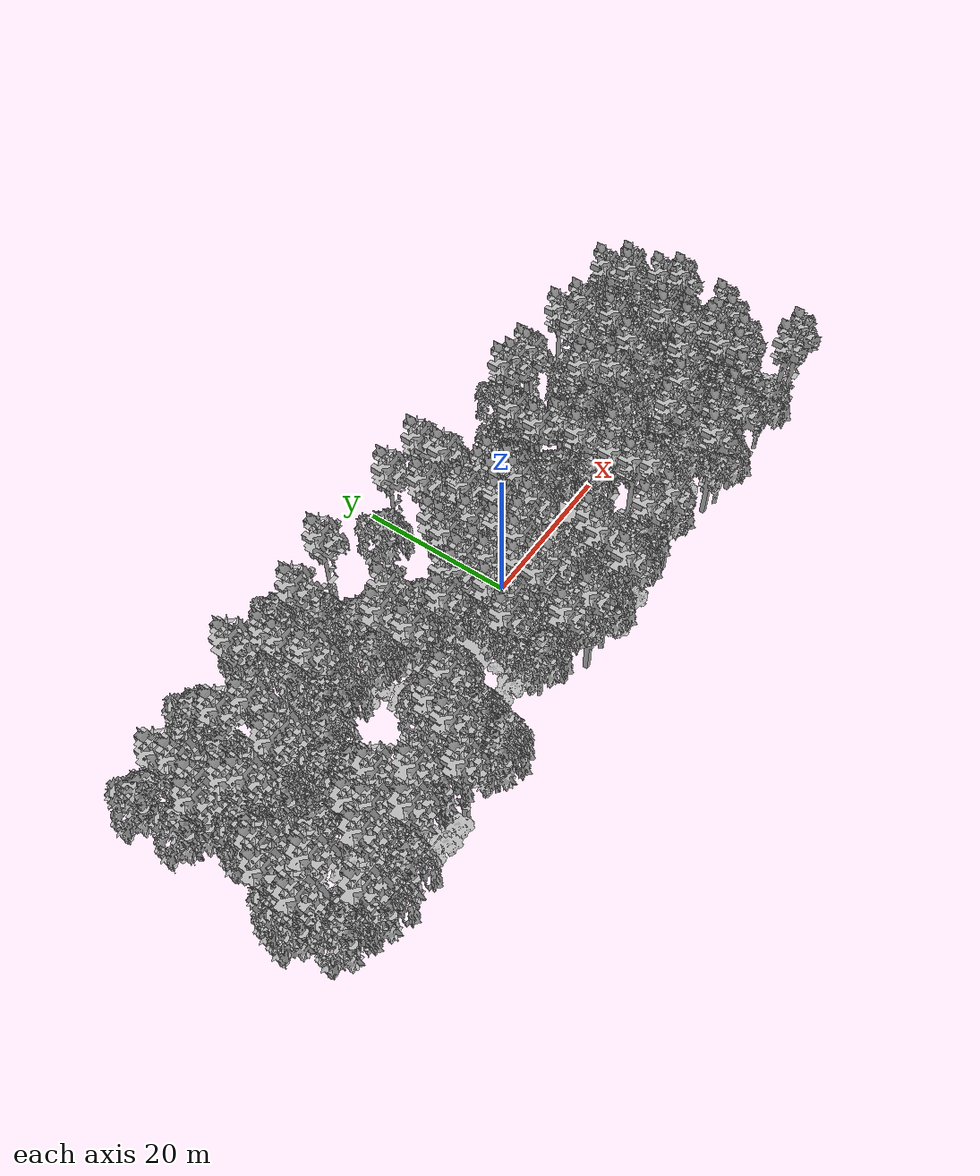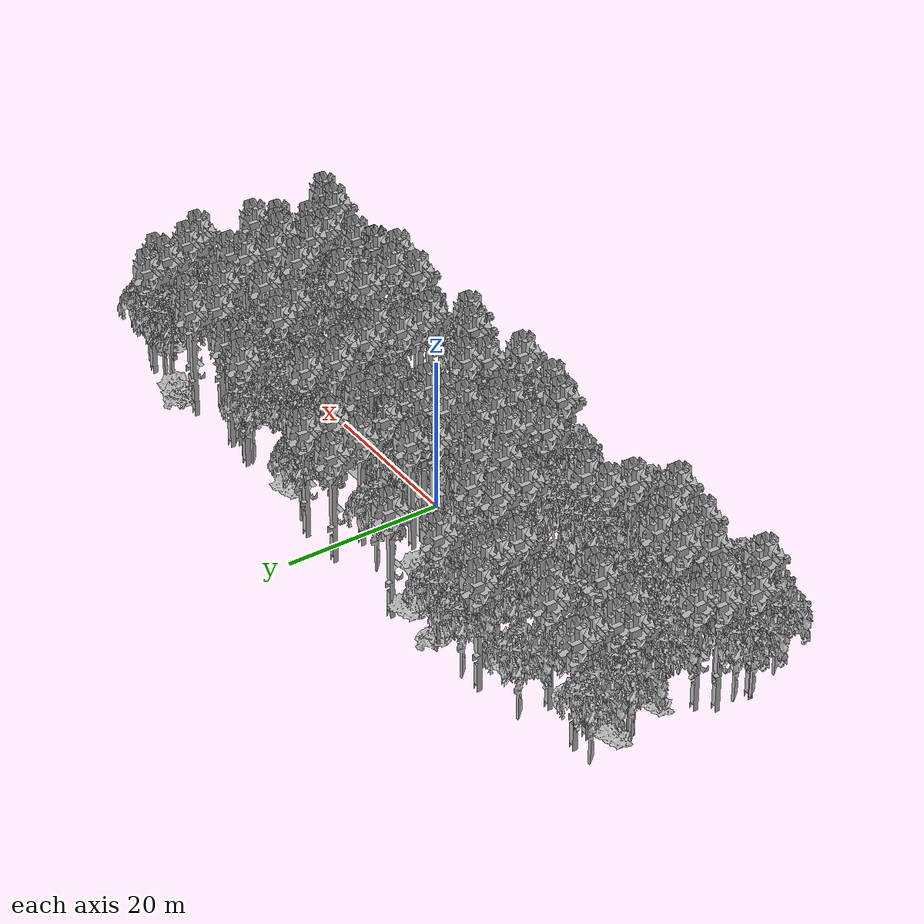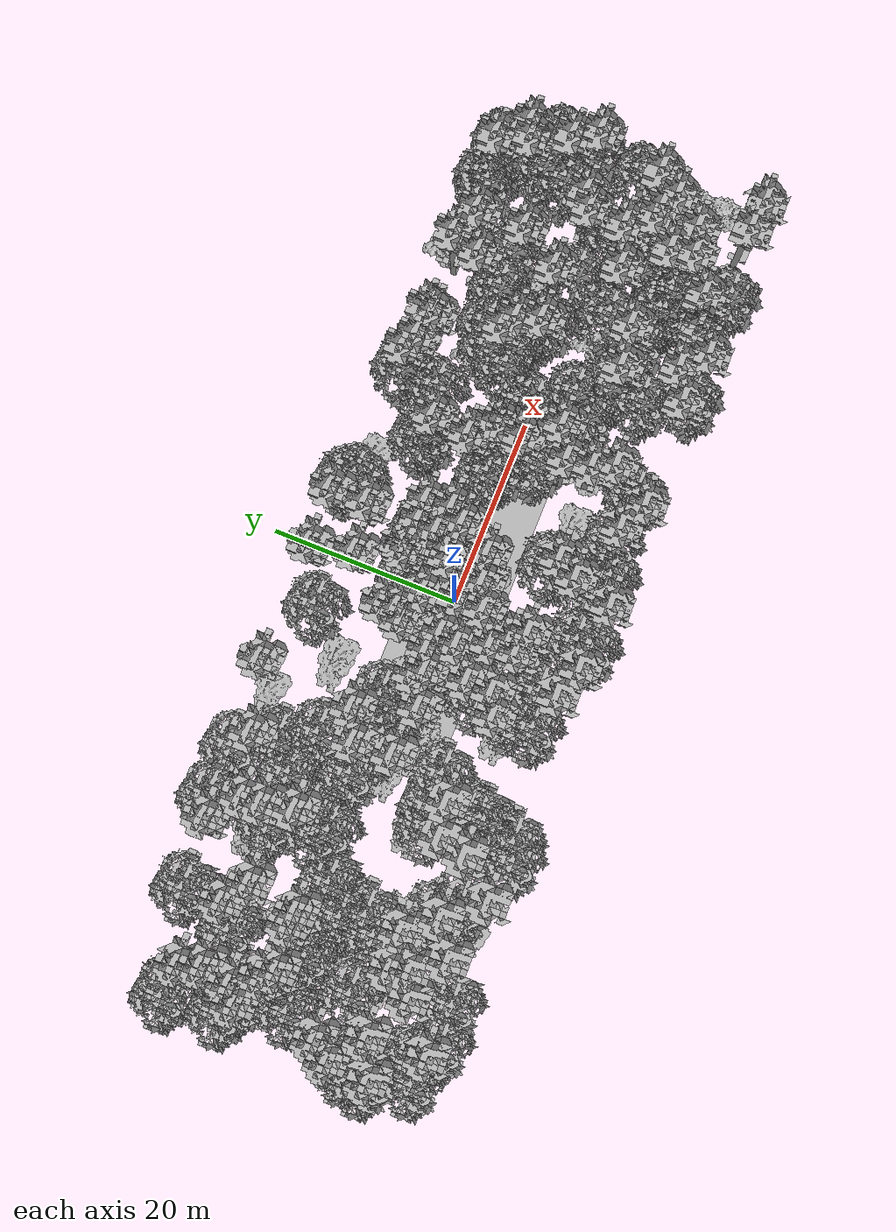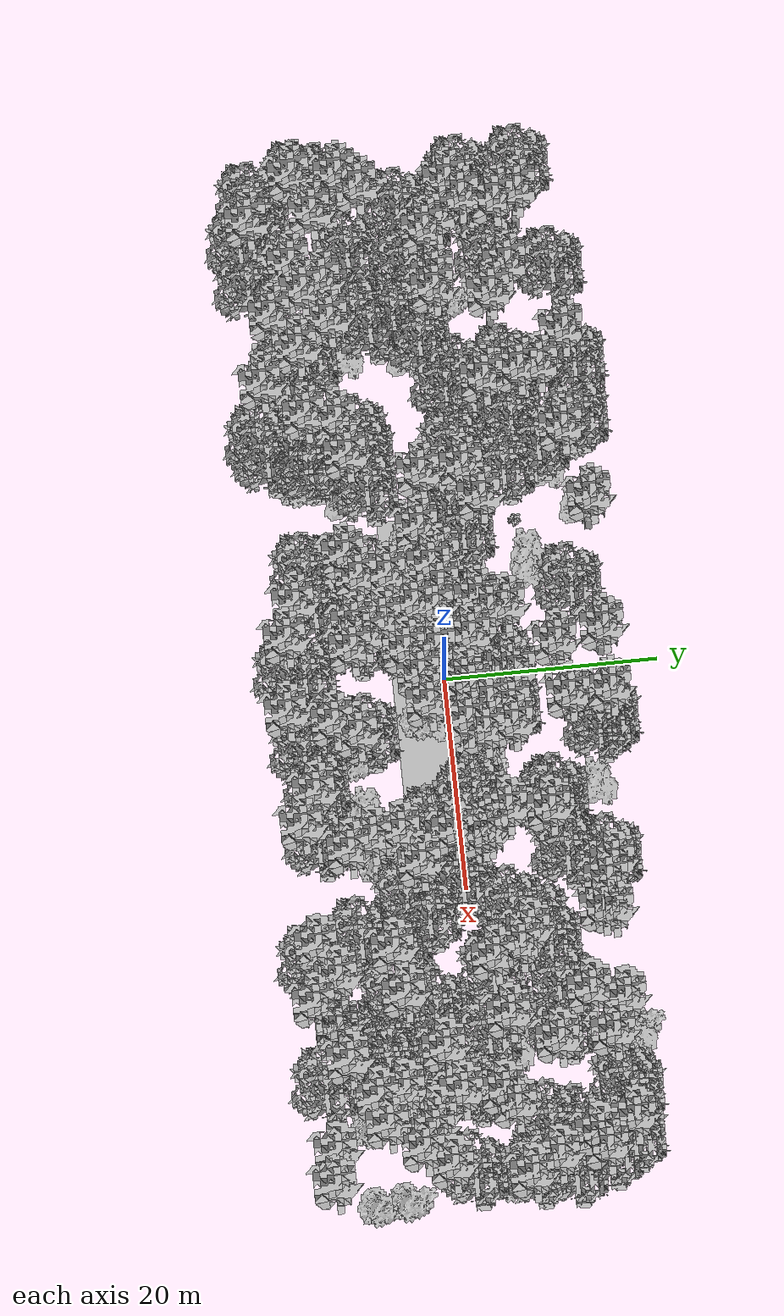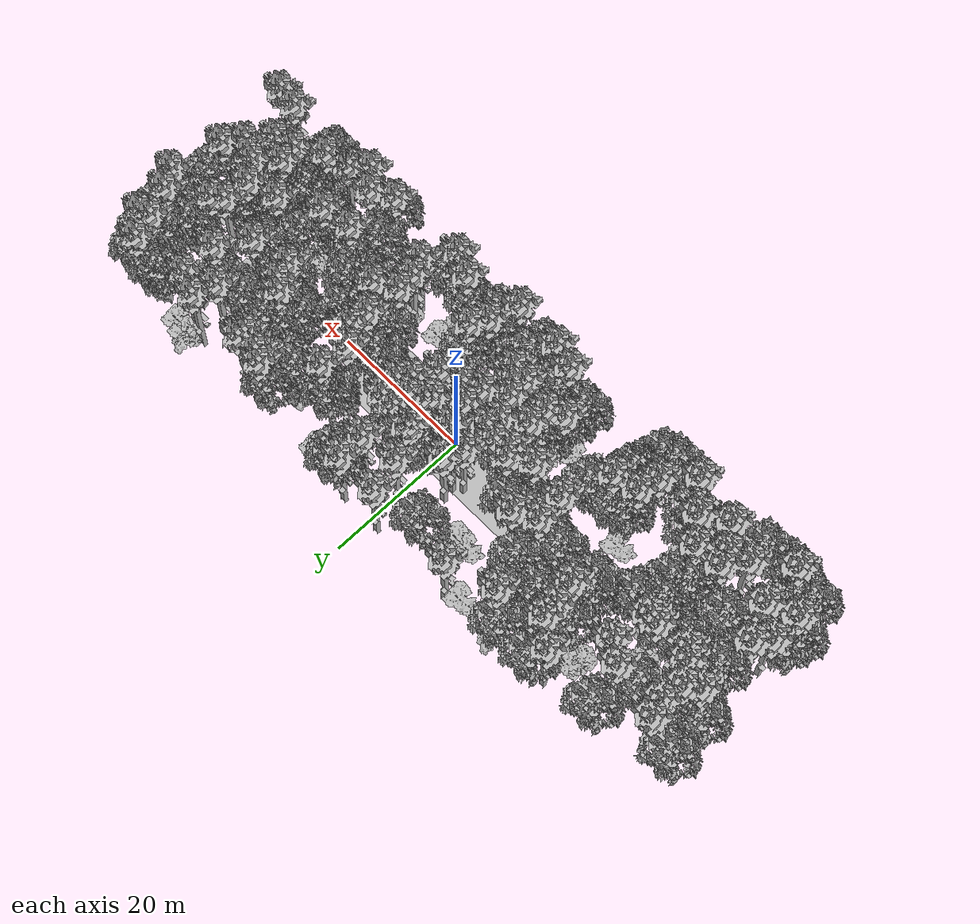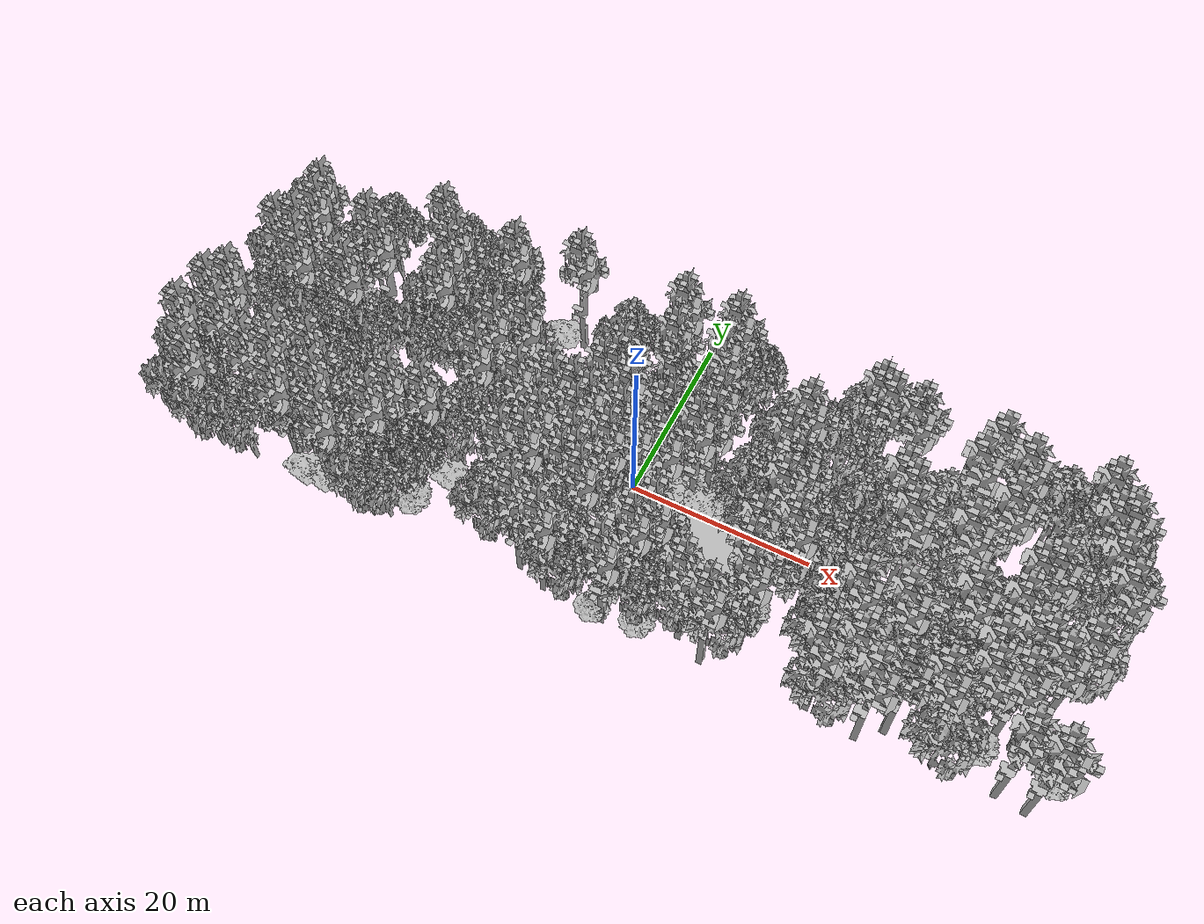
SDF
<sdf version="1.7">
    <world name="default">
        <plugin name="mrs_gazebo_static_transform_republisher_plugin" filename="libMrsGazeboCommonResources_StaticTransformRepublisher.so"/>
        <spherical_coordinates>
            <surface_model>EARTH_WGS84</surface_model>
            <latitude_deg>47.3977</latitude_deg>
            <longitude_deg>8.54559</longitude_deg>
            <elevation>0</elevation>
            <heading_deg>0</heading_deg>
        </spherical_coordinates>
        <physics name="default_physics" default="0" type="ode">
            <ode>
                <solver>
                    <type>quick</type>
                    <iters>10</iters>
                    <sor>1.3</sor>
                    <use_dynamic_moi_rescaling>0</use_dynamic_moi_rescaling>
                </solver>
                <constraints>
                    <cfm>0</cfm>
                    <erp>0.2</erp>
                    <contact_max_correcting_vel>1000</contact_max_correcting_vel>
                    <contact_surface_layer>0.001</contact_surface_layer>
                </constraints>
            </ode>
            <max_step_size>0.004</max_step_size>
            <real_time_factor>1</real_time_factor>
            <real_time_update_rate>250</real_time_update_rate>
        </physics>
        <scene>
            <shadows>0</shadows>
            <ambient>0.4 0.4 0.4 1</ambient>
            <background>0.7 0.7 0.7 1</background>
        </scene>
        <light name="sun" type="directional">
            <pose>0 0 1000 0.4 0.2 0</pose>
            <diffuse>1 1 1 1</diffuse>
            <specular>0.6 0.6 0.6 1</specular>
            <direction>0.1 0.1 -0.9</direction>
            <attenuation>
                <range>20</range>
                <constant>0.5</constant>
                <linear>0.01</linear>
                <quadratic>0.001</quadratic>
            </attenuation>
            <cast_shadows>1</cast_shadows>
            <spot>
                <inner_angle>0</inner_angle>
                <outer_angle>0</outer_angle>
                <falloff>0</falloff>
            </spot>
        </light>
        <model name="ground_plane">
            <static>1</static>
            <link name="link">
                <collision name="collision">
                    <pose>-50 0 0 0 -0 0</pose>
                    <geometry>
                        <plane>
                            <normal>0 0 1</normal>
                            <size>100 100</size>
                        </plane>
                    </geometry>
                    <surface>
                        <contact>
                            <ode>
                                <min_depth>0.01</min_depth>
                                <max_vel>0</max_vel>
                            </ode>
                        </contact>
                        <friction>
                            <ode/>
                            <torsional>
                                <ode/>
                            </torsional>
                        </friction>
                        <bounce/>
                    </surface>
                    <max_contacts>10</max_contacts>
                </collision>
                <visual name="grass">
                    <pose>0 0 0 0 -0 0</pose>
                    <cast_shadows>0</cast_shadows>
                    <geometry>
                        <mesh>
                            <scale>0.5814285714285714 0.18142857142857144 0.1</scale>
                            <uri>file://grass_plane/meshes/grass_plane.dae</uri>
                        </mesh>
                    </geometry>
                </visual>
                <self_collide>0</self_collide>
                <enable_wind>0</enable_wind>
                <kinematic>0</kinematic>
            </link>
        </model>
        <model name="the_void">
            <static>1</static>
            <link name="link">
                <pose>0 0 0.1 0 -0 0</pose>
                <visual name="the_void">
                    <pose>0 0 2 0 -0 0</pose>
                    <geometry>
                        <sphere>
                            <radius>0.25</radius>
                        </sphere>
                    </geometry>
                    <material>
                        <script>
                            <uri>file://media/materials/scripts/Gazebo.material</uri>
                            <name>Gazebo/Black</name>
                        </script>
                    </material>
                </visual>
                <self_collide>0</self_collide>
                <enable_wind>0</enable_wind>
                <kinematic>0</kinematic>
            </link>
            <pose>-1000 -1000 0 0 -0 0</pose>
        </model>
        <gui fullscreen="0">
            <camera name="camera">
                <pose>35.1577 98.6044 40.0204 0 0.407996 -1.99761</pose>
                <view_controller>orbit</view_controller>
                <projection_type>perspective</projection_type>
            </camera>
        </gui>
        <plugin name="mrs_gazebo_rviz_cam_synchronizer" filename="libMrsGazeboCommonResources_RvizCameraSynchronizer.so">
            <target_frame_id>gazebo_user_camera</target_frame_id>
            <world_origin_frame_id>uav1/gps_origin</world_origin_frame_id>
            <frame_to_follow>uav1</frame_to_follow>
        </plugin>
        <gravity>0 0 -9.8066</gravity>
        <magnetic_field>6e-06 2.3e-05 -4.2e-05</magnetic_field>
        <atmosphere type="adiabatic"/>
        <wind/>
        <model name="Tree 0">
            <static>1</static>
            <pose>-40.20979080578474 -5.091505781952723 0 1.57079 -0 0</pose>
            <link name="link">
                <pose>0 0 0 0 -0 0</pose>
                <collision name="collision">
                    <geometry>
                        <mesh>
                            <scale>3.5 5 3.5</scale>
                            <uri>model://tree_2/meshes/tree_2.obj</uri>
                        </mesh>
                    </geometry>
                    <max_contacts>10</max_contacts>
                    <surface>
                        <contact>
                            <ode/>
                        </contact>
                        <bounce/>
                        <friction>
                            <torsional>
                                <ode/>
                            </torsional>
                            <ode/>
                        </friction>
                    </surface>
                </collision>
                <visual name="visual">
                    <geometry>
                        <mesh>
                            <scale>3.5 5 3.5</scale>
                            <uri>model://tree_2/meshes/tree_2.obj</uri>
                        </mesh>
                    </geometry>
                </visual>
                <self_collide>0</self_collide>
                <enable_wind>0</enable_wind>
                <kinematic>0</kinematic>
            </link>
        </model>
        <model name="Tree 1">
            <static>1</static>
            <pose>39.66715383200335 -9.79743286991348 0 1.57079 -0 0</pose>
            <link name="link">
                <pose>0 0 0 0 -0 0</pose>
                <collision name="collision">
                    <geometry>
                        <mesh>
                            <scale>3.5 5 3.5</scale>
                            <uri>model://tree_9/meshes/tree_9.obj</uri>
                        </mesh>
                    </geometry>
                    <max_contacts>10</max_contacts>
                    <surface>
                        <contact>
                            <ode/>
                        </contact>
                        <bounce/>
                        <friction>
                            <torsional>
                                <ode/>
                            </torsional>
                            <ode/>
                        </friction>
                    </surface>
                </collision>
                <visual name="visual">
                    <geometry>
                        <mesh>
                            <scale>3.5 5 3.5</scale>
                            <uri>model://tree_9/meshes/tree_9.obj</uri>
                        </mesh>
                    </geometry>
                </visual>
                <self_collide>0</self_collide>
                <enable_wind>0</enable_wind>
                <kinematic>0</kinematic>
            </link>
        </model>
        <model name="Tree 2">
            <static>1</static>
            <pose>14.374768445427776 -14.266316899726641 0 1.57079 -0 0</pose>
            <link name="link">
                <pose>0 0 0 0 -0 0</pose>
                <collision name="collision">
                    <geometry>
                        <mesh>
                            <scale>3.5 5 3.5</scale>
                            <uri>model://tree_9/meshes/tree_9.obj</uri>
                        </mesh>
                    </geometry>
                    <max_contacts>10</max_contacts>
                    <surface>
                        <contact>
                            <ode/>
                        </contact>
                        <bounce/>
                        <friction>
                            <torsional>
                                <ode/>
                            </torsional>
                            <ode/>
                        </friction>
                    </surface>
                </collision>
                <visual name="visual">
                    <geometry>
                        <mesh>
                            <scale>3.5 5 3.5</scale>
                            <uri>model://tree_9/meshes/tree_9.obj</uri>
                        </mesh>
                    </geometry>
                </visual>
                <self_collide>0</self_collide>
                <enable_wind>0</enable_wind>
                <kinematic>0</kinematic>
            </link>
        </model>
        <model name="Tree 3">
            <static>1</static>
            <pose>-5.163711916937544 -2.2605145847753825 0 1.57079 -0 0</pose>
            <link name="link">
                <pose>0 0 0 0 -0 0</pose>
                <collision name="collision">
                    <geometry>
                        <mesh>
                            <scale>3.5 5 3.5</scale>
                            <uri>model://tree_9/meshes/tree_9.obj</uri>
                        </mesh>
                    </geometry>
                    <max_contacts>10</max_contacts>
                    <surface>
                        <contact>
                            <ode/>
                        </contact>
                        <bounce/>
                        <friction>
                            <torsional>
                                <ode/>
                            </torsional>
                            <ode/>
                        </friction>
                    </surface>
                </collision>
                <visual name="visual">
                    <geometry>
                        <mesh>
                            <scale>3.5 5 3.5</scale>
                            <uri>model://tree_9/meshes/tree_9.obj</uri>
                        </mesh>
                    </geometry>
                </visual>
                <self_collide>0</self_collide>
                <enable_wind>0</enable_wind>
                <kinematic>0</kinematic>
            </link>
        </model>
        <model name="Tree 4">
            <static>1</static>
            <pose>38.85485388677229 -6.85796119349353 0 1.57079 -0 0</pose>
            <link name="link">
                <pose>0 0 0 0 -0 0</pose>
                <collision name="collision">
                    <geometry>
                        <mesh>
                            <scale>3.5 5 3.5</scale>
                            <uri>model://tree_2/meshes/tree_2.obj</uri>
                        </mesh>
                    </geometry>
                    <max_contacts>10</max_contacts>
                    <surface>
                        <contact>
                            <ode/>
                        </contact>
                        <bounce/>
                        <friction>
                            <torsional>
                                <ode/>
                            </torsional>
                            <ode/>
                        </friction>
                    </surface>
                </collision>
                <visual name="visual">
                    <geometry>
                        <mesh>
                            <scale>3.5 5 3.5</scale>
                            <uri>model://tree_2/meshes/tree_2.obj</uri>
                        </mesh>
                    </geometry>
                </visual>
                <self_collide>0</self_collide>
                <enable_wind>0</enable_wind>
                <kinematic>0</kinematic>
            </link>
        </model>
        <model name="Tree 5">
            <static>1</static>
            <pose>35.32782295275514 2.653738546690043 0 1.57079 -0 0</pose>
            <link name="link">
                <pose>0 0 0 0 -0 0</pose>
                <collision name="collision">
                    <geometry>
                        <mesh>
                            <scale>3 2 3</scale>
                            <uri>model://tree_3/meshes/tree_3.obj</uri>
                        </mesh>
                    </geometry>
                    <max_contacts>10</max_contacts>
                    <surface>
                        <contact>
                            <ode/>
                        </contact>
                        <bounce/>
                        <friction>
                            <torsional>
                                <ode/>
                            </torsional>
                            <ode/>
                        </friction>
                    </surface>
                </collision>
                <visual name="visual">
                    <geometry>
                        <mesh>
                            <scale>3 2 3</scale>
                            <uri>model://tree_3/meshes/tree_3.obj</uri>
                        </mesh>
                    </geometry>
                </visual>
                <self_collide>0</self_collide>
                <enable_wind>0</enable_wind>
                <kinematic>0</kinematic>
            </link>
        </model>
        <model name="Tree 6">
            <static>1</static>
            <pose>-6.70449100990713 0.2744432947563489 0 1.57079 -0 0</pose>
            <link name="link">
                <pose>0 0 0 0 -0 0</pose>
                <collision name="collision">
                    <geometry>
                        <mesh>
                            <scale>3.5 5 3.5</scale>
                            <uri>model://tree_9/meshes/tree_9.obj</uri>
                        </mesh>
                    </geometry>
                    <max_contacts>10</max_contacts>
                    <surface>
                        <contact>
                            <ode/>
                        </contact>
                        <bounce/>
                        <friction>
                            <torsional>
                                <ode/>
                            </torsional>
                            <ode/>
                        </friction>
                    </surface>
                </collision>
                <visual name="visual">
                    <geometry>
                        <mesh>
                            <scale>3.5 5 3.5</scale>
                            <uri>model://tree_9/meshes/tree_9.obj</uri>
                        </mesh>
                    </geometry>
                </visual>
                <self_collide>0</self_collide>
                <enable_wind>0</enable_wind>
                <kinematic>0</kinematic>
            </link>
        </model>
        <model name="Tree 7">
            <static>1</static>
            <pose>-32.6318323390865 -7.410039385801264 0 1.57079 -0 0</pose>
            <link name="link">
                <pose>0 0 0 0 -0 0</pose>
                <collision name="collision">
                    <geometry>
                        <mesh>
                            <scale>3.5 5 3.5</scale>
                            <uri>model://tree_9/meshes/tree_9.obj</uri>
                        </mesh>
                    </geometry>
                    <max_contacts>10</max_contacts>
                    <surface>
                        <contact>
                            <ode/>
                        </contact>
                        <bounce/>
                        <friction>
                            <torsional>
                                <ode/>
                            </torsional>
                            <ode/>
                        </friction>
                    </surface>
                </collision>
                <visual name="visual">
                    <geometry>
                        <mesh>
                            <scale>3.5 5 3.5</scale>
                            <uri>model://tree_9/meshes/tree_9.obj</uri>
                        </mesh>
                    </geometry>
                </visual>
                <self_collide>0</self_collide>
                <enable_wind>0</enable_wind>
                <kinematic>0</kinematic>
            </link>
        </model>
        <model name="Tree 8">
            <static>1</static>
            <pose>34.388358188484276 0.6151273616343111 0 1.57079 -0 0</pose>
            <link name="link">
                <pose>0 0 0 0 -0 0</pose>
                <collision name="collision">
                    <geometry>
                        <mesh>
                            <scale>3.5 5 3.5</scale>
                            <uri>model://tree_2/meshes/tree_2.obj</uri>
                        </mesh>
                    </geometry>
                    <max_contacts>10</max_contacts>
                    <surface>
                        <contact>
                            <ode/>
                        </contact>
                        <bounce/>
                        <friction>
                            <torsional>
                                <ode/>
                            </torsional>
                            <ode/>
                        </friction>
                    </surface>
                </collision>
                <visual name="visual">
                    <geometry>
                        <mesh>
                            <scale>3.5 5 3.5</scale>
                            <uri>model://tree_2/meshes/tree_2.obj</uri>
                        </mesh>
                    </geometry>
                </visual>
                <self_collide>0</self_collide>
                <enable_wind>0</enable_wind>
                <kinematic>0</kinematic>
            </link>
        </model>
        <model name="Tree 9">
            <static>1</static>
            <pose>6.66912377891871 2.75567999063135 0 1.57079 -0 0</pose>
            <link name="link">
                <pose>0 0 0 0 -0 0</pose>
                <collision name="collision">
                    <geometry>
                        <mesh>
                            <scale>4 2.5 4</scale>
                            <uri>model://tree_1/meshes/tree_1.obj</uri>
                        </mesh>
                    </geometry>
                    <max_contacts>10</max_contacts>
                    <surface>
                        <contact>
                            <ode/>
                        </contact>
                        <bounce/>
                        <friction>
                            <torsional>
                                <ode/>
                            </torsional>
                            <ode/>
                        </friction>
                    </surface>
                </collision>
                <visual name="visual">
                    <geometry>
                        <mesh>
                            <scale>4 2.5 4</scale>
                            <uri>model://tree_1/meshes/tree_1.obj</uri>
                        </mesh>
                    </geometry>
                </visual>
                <self_collide>0</self_collide>
                <enable_wind>0</enable_wind>
                <kinematic>0</kinematic>
            </link>
        </model>
        <model name="Tree 10">
            <static>1</static>
            <pose>-38.75446158868482 -7.860896149529964 0 1.57079 -0 0</pose>
            <link name="link">
                <pose>0 0 0 0 -0 0</pose>
                <collision name="collision">
                    <geometry>
                        <mesh>
                            <scale>3 2 3</scale>
                            <uri>model://tree_3/meshes/tree_3.obj</uri>
                        </mesh>
                    </geometry>
                    <max_contacts>10</max_contacts>
                    <surface>
                        <contact>
                            <ode/>
                        </contact>
                        <bounce/>
                        <friction>
                            <torsional>
                                <ode/>
                            </torsional>
                            <ode/>
                        </friction>
                    </surface>
                </collision>
                <visual name="visual">
                    <geometry>
                        <mesh>
                            <scale>3 2 3</scale>
                            <uri>model://tree_3/meshes/tree_3.obj</uri>
                        </mesh>
                    </geometry>
                </visual>
                <self_collide>0</self_collide>
                <enable_wind>0</enable_wind>
                <kinematic>0</kinematic>
            </link>
        </model>
        <model name="Tree 11">
            <static>1</static>
            <pose>0.4460111221063201 4.064509342091682 0 1.57079 -0 0</pose>
            <link name="link">
                <pose>0 0 0 0 -0 0</pose>
                <collision name="collision">
                    <geometry>
                        <mesh>
                            <scale>3.5 5 3.5</scale>
                            <uri>model://tree_2/meshes/tree_2.obj</uri>
                        </mesh>
                    </geometry>
                    <max_contacts>10</max_contacts>
                    <surface>
                        <contact>
                            <ode/>
                        </contact>
                        <bounce/>
                        <friction>
                            <torsional>
                                <ode/>
                            </torsional>
                            <ode/>
                        </friction>
                    </surface>
                </collision>
                <visual name="visual">
                    <geometry>
                        <mesh>
                            <scale>3.5 5 3.5</scale>
                            <uri>model://tree_2/meshes/tree_2.obj</uri>
                        </mesh>
                    </geometry>
                </visual>
                <self_collide>0</self_collide>
                <enable_wind>0</enable_wind>
                <kinematic>0</kinematic>
            </link>
        </model>
        <model name="Tree 12">
            <static>1</static>
            <pose>-29.30019269805053 -14.187535318531125 0 1.57079 -0 0</pose>
            <link name="link">
                <pose>0 0 0 0 -0 0</pose>
                <collision name="collision">
                    <geometry>
                        <mesh>
                            <scale>3 2 3</scale>
                            <uri>model://tree_3/meshes/tree_3.obj</uri>
                        </mesh>
                    </geometry>
                    <max_contacts>10</max_contacts>
                    <surface>
                        <contact>
                            <ode/>
                        </contact>
                        <bounce/>
                        <friction>
                            <torsional>
                                <ode/>
                            </torsional>
                            <ode/>
                        </friction>
                    </surface>
                </collision>
                <visual name="visual">
                    <geometry>
                        <mesh>
                            <scale>3 2 3</scale>
                            <uri>model://tree_3/meshes/tree_3.obj</uri>
                        </mesh>
                    </geometry>
                </visual>
                <self_collide>0</self_collide>
                <enable_wind>0</enable_wind>
                <kinematic>0</kinematic>
            </link>
        </model>
        <model name="Tree 13">
            <static>1</static>
            <pose>6.092757079156193 1.5882371681267884 0 1.57079 -0 0</pose>
            <link name="link">
                <pose>0 0 0 0 -0 0</pose>
                <collision name="collision">
                    <geometry>
                        <mesh>
                            <scale>3.5 5 3.5</scale>
                            <uri>model://tree_9/meshes/tree_9.obj</uri>
                        </mesh>
                    </geometry>
                    <max_contacts>10</max_contacts>
                    <surface>
                        <contact>
                            <ode/>
                        </contact>
                        <bounce/>
                        <friction>
                            <torsional>
                                <ode/>
                            </torsional>
                            <ode/>
                        </friction>
                    </surface>
                </collision>
                <visual name="visual">
                    <geometry>
                        <mesh>
                            <scale>3.5 5 3.5</scale>
                            <uri>model://tree_9/meshes/tree_9.obj</uri>
                        </mesh>
                    </geometry>
                </visual>
                <self_collide>0</self_collide>
                <enable_wind>0</enable_wind>
                <kinematic>0</kinematic>
            </link>
        </model>
        <model name="Tree 14">
            <static>1</static>
            <pose>39.300211839281104 -1.1267173630179173 0 1.57079 -0 0</pose>
            <link name="link">
                <pose>0 0 0 0 -0 0</pose>
                <collision name="collision">
                    <geometry>
                        <mesh>
                            <scale>3.5 5 3.5</scale>
                            <uri>model://tree_2/meshes/tree_2.obj</uri>
                        </mesh>
                    </geometry>
                    <max_contacts>10</max_contacts>
                    <surface>
                        <contact>
                            <ode/>
                        </contact>
                        <bounce/>
                        <friction>
                            <torsional>
                                <ode/>
                            </torsional>
                            <ode/>
                        </friction>
                    </surface>
                </collision>
                <visual name="visual">
                    <geometry>
                        <mesh>
                            <scale>3.5 5 3.5</scale>
                            <uri>model://tree_2/meshes/tree_2.obj</uri>
                        </mesh>
                    </geometry>
                </visual>
                <self_collide>0</self_collide>
                <enable_wind>0</enable_wind>
                <kinematic>0</kinematic>
            </link>
        </model>
        <model name="Tree 15">
            <static>1</static>
            <pose>32.99031036902194 -12.858967480910888 0 1.57079 -0 0</pose>
            <link name="link">
                <pose>0 0 0 0 -0 0</pose>
                <collision name="collision">
                    <geometry>
                        <mesh>
                            <scale>3.5 5 3.5</scale>
                            <uri>model://tree_9/meshes/tree_9.obj</uri>
                        </mesh>
                    </geometry>
                    <max_contacts>10</max_contacts>
                    <surface>
                        <contact>
                            <ode/>
                        </contact>
                        <bounce/>
                        <friction>
                            <torsional>
                                <ode/>
                            </torsional>
                            <ode/>
                        </friction>
                    </surface>
                </collision>
                <visual name="visual">
                    <geometry>
                        <mesh>
                            <scale>3.5 5 3.5</scale>
                            <uri>model://tree_9/meshes/tree_9.obj</uri>
                        </mesh>
                    </geometry>
                </visual>
                <self_collide>0</self_collide>
                <enable_wind>0</enable_wind>
                <kinematic>0</kinematic>
            </link>
        </model>
        <model name="Tree 16">
            <static>1</static>
            <pose>-33.788477339152394 7.710203744241319 0 1.57079 -0 0</pose>
            <link name="link">
                <pose>0 0 0 0 -0 0</pose>
                <collision name="collision">
                    <geometry>
                        <mesh>
                            <scale>3.5 5 3.5</scale>
                            <uri>model://tree_9/meshes/tree_9.obj</uri>
                        </mesh>
                    </geometry>
                    <max_contacts>10</max_contacts>
                    <surface>
                        <contact>
                            <ode/>
                        </contact>
                        <bounce/>
                        <friction>
                            <torsional>
                                <ode/>
                            </torsional>
                            <ode/>
                        </friction>
                    </surface>
                </collision>
                <visual name="visual">
                    <geometry>
                        <mesh>
                            <scale>3.5 5 3.5</scale>
                            <uri>model://tree_9/meshes/tree_9.obj</uri>
                        </mesh>
                    </geometry>
                </visual>
                <self_collide>0</self_collide>
                <enable_wind>0</enable_wind>
                <kinematic>0</kinematic>
            </link>
        </model>
        <model name="Tree 17">
            <static>1</static>
            <pose>-22.609338976286516 -14.978319491097414 0 1.57079 -0 0</pose>
            <link name="link">
                <pose>0 0 0 0 -0 0</pose>
                <collision name="collision">
                    <geometry>
                        <mesh>
                            <scale>3.5 5 3.5</scale>
                            <uri>model://tree_2/meshes/tree_2.obj</uri>
                        </mesh>
                    </geometry>
                    <max_contacts>10</max_contacts>
                    <surface>
                        <contact>
                            <ode/>
                        </contact>
                        <bounce/>
                        <friction>
                            <torsional>
                                <ode/>
                            </torsional>
                            <ode/>
                        </friction>
                    </surface>
                </collision>
                <visual name="visual">
                    <geometry>
                        <mesh>
                            <scale>3.5 5 3.5</scale>
                            <uri>model://tree_2/meshes/tree_2.obj</uri>
                        </mesh>
                    </geometry>
                </visual>
                <self_collide>0</self_collide>
                <enable_wind>0</enable_wind>
                <kinematic>0</kinematic>
            </link>
        </model>
        <model name="Tree 18">
            <static>1</static>
            <pose>-30.111929667590598 10.298646541853945 0 1.57079 -0 0</pose>
            <link name="link">
                <pose>0 0 0 0 -0 0</pose>
                <collision name="collision">
                    <geometry>
                        <mesh>
                            <scale>3 2 3</scale>
                            <uri>model://tree_3/meshes/tree_3.obj</uri>
                        </mesh>
                    </geometry>
                    <max_contacts>10</max_contacts>
                    <surface>
                        <contact>
                            <ode/>
                        </contact>
                        <bounce/>
                        <friction>
                            <torsional>
                                <ode/>
                            </torsional>
                            <ode/>
                        </friction>
                    </surface>
                </collision>
                <visual name="visual">
                    <geometry>
                        <mesh>
                            <scale>3 2 3</scale>
                            <uri>model://tree_3/meshes/tree_3.obj</uri>
                        </mesh>
                    </geometry>
                </visual>
                <self_collide>0</self_collide>
                <enable_wind>0</enable_wind>
                <kinematic>0</kinematic>
            </link>
        </model>
        <model name="Tree 19">
            <static>1</static>
            <pose>-23.06173525690212 -7.55962782728095 0 1.57079 -0 0</pose>
            <link name="link">
                <pose>0 0 0 0 -0 0</pose>
                <collision name="collision">
                    <geometry>
                        <mesh>
                            <scale>3.5 5 3.5</scale>
                            <uri>model://tree_9/meshes/tree_9.obj</uri>
                        </mesh>
                    </geometry>
                    <max_contacts>10</max_contacts>
                    <surface>
                        <contact>
                            <ode/>
                        </contact>
                        <bounce/>
                        <friction>
                            <torsional>
                                <ode/>
                            </torsional>
                            <ode/>
                        </friction>
                    </surface>
                </collision>
                <visual name="visual">
                    <geometry>
                        <mesh>
                            <scale>3.5 5 3.5</scale>
                            <uri>model://tree_9/meshes/tree_9.obj</uri>
                        </mesh>
                    </geometry>
                </visual>
                <self_collide>0</self_collide>
                <enable_wind>0</enable_wind>
                <kinematic>0</kinematic>
            </link>
        </model>
        <model name="Tree 20">
            <static>1</static>
            <pose>-43.339526954036955 11.111264934391812 0 1.57079 -0 0</pose>
            <link name="link">
                <pose>0 0 0 0 -0 0</pose>
                <collision name="collision">
                    <geometry>
                        <mesh>
                            <scale>3.5 5 3.5</scale>
                            <uri>model://tree_9/meshes/tree_9.obj</uri>
                        </mesh>
                    </geometry>
                    <max_contacts>10</max_contacts>
                    <surface>
                        <contact>
                            <ode/>
                        </contact>
                        <bounce/>
                        <friction>
                            <torsional>
                                <ode/>
                            </torsional>
                            <ode/>
                        </friction>
                    </surface>
                </collision>
                <visual name="visual">
                    <geometry>
                        <mesh>
                            <scale>3.5 5 3.5</scale>
                            <uri>model://tree_9/meshes/tree_9.obj</uri>
                        </mesh>
                    </geometry>
                </visual>
                <self_collide>0</self_collide>
                <enable_wind>0</enable_wind>
                <kinematic>0</kinematic>
            </link>
        </model>
        <model name="Tree 21">
            <static>1</static>
            <pose>16.50094595327164 2.427519827041362 0 1.57079 -0 0</pose>
            <link name="link">
                <pose>0 0 0 0 -0 0</pose>
                <collision name="collision">
                    <geometry>
                        <mesh>
                            <scale>3.5 5 3.5</scale>
                            <uri>model://tree_9/meshes/tree_9.obj</uri>
                        </mesh>
                    </geometry>
                    <max_contacts>10</max_contacts>
                    <surface>
                        <contact>
                            <ode/>
                        </contact>
                        <bounce/>
                        <friction>
                            <torsional>
                                <ode/>
                            </torsional>
                            <ode/>
                        </friction>
                    </surface>
                </collision>
                <visual name="visual">
                    <geometry>
                        <mesh>
                            <scale>3.5 5 3.5</scale>
                            <uri>model://tree_9/meshes/tree_9.obj</uri>
                        </mesh>
                    </geometry>
                </visual>
                <self_collide>0</self_collide>
                <enable_wind>0</enable_wind>
                <kinematic>0</kinematic>
            </link>
        </model>
        <model name="Tree 22">
            <static>1</static>
            <pose>11.29381462864442 -11.099675055511366 0 1.57079 -0 0</pose>
            <link name="link">
                <pose>0 0 0 0 -0 0</pose>
                <collision name="collision">
                    <geometry>
                        <mesh>
                            <scale>4 2.5 4</scale>
                            <uri>model://tree_1/meshes/tree_1.obj</uri>
                        </mesh>
                    </geometry>
                    <max_contacts>10</max_contacts>
                    <surface>
                        <contact>
                            <ode/>
                        </contact>
                        <bounce/>
                        <friction>
                            <torsional>
                                <ode/>
                            </torsional>
                            <ode/>
                        </friction>
                    </surface>
                </collision>
                <visual name="visual">
                    <geometry>
                        <mesh>
                            <scale>4 2.5 4</scale>
                            <uri>model://tree_1/meshes/tree_1.obj</uri>
                        </mesh>
                    </geometry>
                </visual>
                <self_collide>0</self_collide>
                <enable_wind>0</enable_wind>
                <kinematic>0</kinematic>
            </link>
        </model>
        <model name="Tree 23">
            <static>1</static>
            <pose>-43.88627854497907 0.6732376981152903 0 1.57079 -0 0</pose>
            <link name="link">
                <pose>0 0 0 0 -0 0</pose>
                <collision name="collision">
                    <geometry>
                        <mesh>
                            <scale>3 2 3</scale>
                            <uri>model://tree_3/meshes/tree_3.obj</uri>
                        </mesh>
                    </geometry>
                    <max_contacts>10</max_contacts>
                    <surface>
                        <contact>
                            <ode/>
                        </contact>
                        <bounce/>
                        <friction>
                            <torsional>
                                <ode/>
                            </torsional>
                            <ode/>
                        </friction>
                    </surface>
                </collision>
                <visual name="visual">
                    <geometry>
                        <mesh>
                            <scale>3 2 3</scale>
                            <uri>model://tree_3/meshes/tree_3.obj</uri>
                        </mesh>
                    </geometry>
                </visual>
                <self_collide>0</self_collide>
                <enable_wind>0</enable_wind>
                <kinematic>0</kinematic>
            </link>
        </model>
        <model name="Tree 24">
            <static>1</static>
            <pose>4.432076810408617 3.6540542603658963 0 1.57079 -0 0</pose>
            <link name="link">
                <pose>0 0 0 0 -0 0</pose>
                <collision name="collision">
                    <geometry>
                        <mesh>
                            <scale>3.5 5 3.5</scale>
                            <uri>model://tree_9/meshes/tree_9.obj</uri>
                        </mesh>
                    </geometry>
                    <max_contacts>10</max_contacts>
                    <surface>
                        <contact>
                            <ode/>
                        </contact>
                        <bounce/>
                        <friction>
                            <torsional>
                                <ode/>
                            </torsional>
                            <ode/>
                        </friction>
                    </surface>
                </collision>
                <visual name="visual">
                    <geometry>
                        <mesh>
                            <scale>3.5 5 3.5</scale>
                            <uri>model://tree_9/meshes/tree_9.obj</uri>
                        </mesh>
                    </geometry>
                </visual>
                <self_collide>0</self_collide>
                <enable_wind>0</enable_wind>
                <kinematic>0</kinematic>
            </link>
        </model>
        <model name="Tree 25">
            <static>1</static>
            <pose>-10.352674955810421 -8.074041081286769 0 1.57079 -0 0</pose>
            <link name="link">
                <pose>0 0 0 0 -0 0</pose>
                <collision name="collision">
                    <geometry>
                        <mesh>
                            <scale>3.5 5 3.5</scale>
                            <uri>model://tree_9/meshes/tree_9.obj</uri>
                        </mesh>
                    </geometry>
                    <max_contacts>10</max_contacts>
                    <surface>
                        <contact>
                            <ode/>
                        </contact>
                        <bounce/>
                        <friction>
                            <torsional>
                                <ode/>
                            </torsional>
                            <ode/>
                        </friction>
                    </surface>
                </collision>
                <visual name="visual">
                    <geometry>
                        <mesh>
                            <scale>3.5 5 3.5</scale>
                            <uri>model://tree_9/meshes/tree_9.obj</uri>
                        </mesh>
                    </geometry>
                </visual>
                <self_collide>0</self_collide>
                <enable_wind>0</enable_wind>
                <kinematic>0</kinematic>
            </link>
        </model>
        <model name="Tree 26">
            <static>1</static>
            <pose>44.80414023411129 9.549171326828073 0 1.57079 -0 0</pose>
            <link name="link">
                <pose>0 0 0 0 -0 0</pose>
                <collision name="collision">
                    <geometry>
                        <mesh>
                            <scale>3.5 5 3.5</scale>
                            <uri>model://tree_9/meshes/tree_9.obj</uri>
                        </mesh>
                    </geometry>
                    <max_contacts>10</max_contacts>
                    <surface>
                        <contact>
                            <ode/>
                        </contact>
                        <bounce/>
                        <friction>
                            <torsional>
                                <ode/>
                            </torsional>
                            <ode/>
                        </friction>
                    </surface>
                </collision>
                <visual name="visual">
                    <geometry>
                        <mesh>
                            <scale>3.5 5 3.5</scale>
                            <uri>model://tree_9/meshes/tree_9.obj</uri>
                        </mesh>
                    </geometry>
                </visual>
                <self_collide>0</self_collide>
                <enable_wind>0</enable_wind>
                <kinematic>0</kinematic>
            </link>
        </model>
        <model name="Tree 27">
            <static>1</static>
            <pose>41.535559727347135 2.414591668651479 0 1.57079 -0 0</pose>
            <link name="link">
                <pose>0 0 0 0 -0 0</pose>
                <collision name="collision">
                    <geometry>
                        <mesh>
                            <scale>3.5 5 3.5</scale>
                            <uri>model://tree_9/meshes/tree_9.obj</uri>
                        </mesh>
                    </geometry>
                    <max_contacts>10</max_contacts>
                    <surface>
                        <contact>
                            <ode/>
                        </contact>
                        <bounce/>
                        <friction>
                            <torsional>
                                <ode/>
                            </torsional>
                            <ode/>
                        </friction>
                    </surface>
                </collision>
                <visual name="visual">
                    <geometry>
                        <mesh>
                            <scale>3.5 5 3.5</scale>
                            <uri>model://tree_9/meshes/tree_9.obj</uri>
                        </mesh>
                    </geometry>
                </visual>
                <self_collide>0</self_collide>
                <enable_wind>0</enable_wind>
                <kinematic>0</kinematic>
            </link>
        </model>
        <model name="Tree 28">
            <static>1</static>
            <pose>40.68554744184236 13.04091409627748 0 1.57079 -0 0</pose>
            <link name="link">
                <pose>0 0 0 0 -0 0</pose>
                <collision name="collision">
                    <geometry>
                        <mesh>
                            <scale>3.5 5 3.5</scale>
                            <uri>model://tree_2/meshes/tree_2.obj</uri>
                        </mesh>
                    </geometry>
                    <max_contacts>10</max_contacts>
                    <surface>
                        <contact>
                            <ode/>
                        </contact>
                        <bounce/>
                        <friction>
                            <torsional>
                                <ode/>
                            </torsional>
                            <ode/>
                        </friction>
                    </surface>
                </collision>
                <visual name="visual">
                    <geometry>
                        <mesh>
                            <scale>3.5 5 3.5</scale>
                            <uri>model://tree_2/meshes/tree_2.obj</uri>
                        </mesh>
                    </geometry>
                </visual>
                <self_collide>0</self_collide>
                <enable_wind>0</enable_wind>
                <kinematic>0</kinematic>
            </link>
        </model>
        <model name="Tree 29">
            <static>1</static>
            <pose>17.025539076455686 -10.248897731775358 0 1.57079 -0 0</pose>
            <link name="link">
                <pose>0 0 0 0 -0 0</pose>
                <collision name="collision">
                    <geometry>
                        <mesh>
                            <scale>3.5 5 3.5</scale>
                            <uri>model://tree_9/meshes/tree_9.obj</uri>
                        </mesh>
                    </geometry>
                    <max_contacts>10</max_contacts>
                    <surface>
                        <contact>
                            <ode/>
                        </contact>
                        <bounce/>
                        <friction>
                            <torsional>
                                <ode/>
                            </torsional>
                            <ode/>
                        </friction>
                    </surface>
                </collision>
                <visual name="visual">
                    <geometry>
                        <mesh>
                            <scale>3.5 5 3.5</scale>
                            <uri>model://tree_9/meshes/tree_9.obj</uri>
                        </mesh>
                    </geometry>
                </visual>
                <self_collide>0</self_collide>
                <enable_wind>0</enable_wind>
                <kinematic>0</kinematic>
            </link>
        </model>
        <model name="Tree 30">
            <static>1</static>
            <pose>14.890058464222292 -2.6212985577836694 0 1.57079 -0 0</pose>
            <link name="link">
                <pose>0 0 0 0 -0 0</pose>
                <collision name="collision">
                    <geometry>
                        <mesh>
                            <scale>3.5 5 3.5</scale>
                            <uri>model://tree_2/meshes/tree_2.obj</uri>
                        </mesh>
                    </geometry>
                    <max_contacts>10</max_contacts>
                    <surface>
                        <contact>
                            <ode/>
                        </contact>
                        <bounce/>
                        <friction>
                            <torsional>
                                <ode/>
                            </torsional>
                            <ode/>
                        </friction>
                    </surface>
                </collision>
                <visual name="visual">
                    <geometry>
                        <mesh>
                            <scale>3.5 5 3.5</scale>
                            <uri>model://tree_2/meshes/tree_2.obj</uri>
                        </mesh>
                    </geometry>
                </visual>
                <self_collide>0</self_collide>
                <enable_wind>0</enable_wind>
                <kinematic>0</kinematic>
            </link>
        </model>
        <model name="Tree 31">
            <static>1</static>
            <pose>-35.96202324921588 2.7534249938481707 0 1.57079 -0 0</pose>
            <link name="link">
                <pose>0 0 0 0 -0 0</pose>
                <collision name="collision">
                    <geometry>
                        <mesh>
                            <scale>3.5 5 3.5</scale>
                            <uri>model://tree_9/meshes/tree_9.obj</uri>
                        </mesh>
                    </geometry>
                    <max_contacts>10</max_contacts>
                    <surface>
                        <contact>
                            <ode/>
                        </contact>
                        <bounce/>
                        <friction>
                            <torsional>
                                <ode/>
                            </torsional>
                            <ode/>
                        </friction>
                    </surface>
                </collision>
                <visual name="visual">
                    <geometry>
                        <mesh>
                            <scale>3.5 5 3.5</scale>
                            <uri>model://tree_9/meshes/tree_9.obj</uri>
                        </mesh>
                    </geometry>
                </visual>
                <self_collide>0</self_collide>
                <enable_wind>0</enable_wind>
                <kinematic>0</kinematic>
            </link>
        </model>
        <model name="Tree 32">
            <static>1</static>
            <pose>6.818679293317452 5.698471274022392 0 1.57079 -0 0</pose>
            <link name="link">
                <pose>0 0 0 0 -0 0</pose>
                <collision name="collision">
                    <geometry>
                        <mesh>
                            <scale>3.5 5 3.5</scale>
                            <uri>model://tree_9/meshes/tree_9.obj</uri>
                        </mesh>
                    </geometry>
                    <max_contacts>10</max_contacts>
                    <surface>
                        <contact>
                            <ode/>
                        </contact>
                        <bounce/>
                        <friction>
                            <torsional>
                                <ode/>
                            </torsional>
                            <ode/>
                        </friction>
                    </surface>
                </collision>
                <visual name="visual">
                    <geometry>
                        <mesh>
                            <scale>3.5 5 3.5</scale>
                            <uri>model://tree_9/meshes/tree_9.obj</uri>
                        </mesh>
                    </geometry>
                </visual>
                <self_collide>0</self_collide>
                <enable_wind>0</enable_wind>
                <kinematic>0</kinematic>
            </link>
        </model>
        <model name="Tree 33">
            <static>1</static>
            <pose>-36.350605501364775 9.465256943601638 0 1.57079 -0 0</pose>
            <link name="link">
                <pose>0 0 0 0 -0 0</pose>
                <collision name="collision">
                    <geometry>
                        <mesh>
                            <scale>3.5 5 3.5</scale>
                            <uri>model://tree_9/meshes/tree_9.obj</uri>
                        </mesh>
                    </geometry>
                    <max_contacts>10</max_contacts>
                    <surface>
                        <contact>
                            <ode/>
                        </contact>
                        <bounce/>
                        <friction>
                            <torsional>
                                <ode/>
                            </torsional>
                            <ode/>
                        </friction>
                    </surface>
                </collision>
                <visual name="visual">
                    <geometry>
                        <mesh>
                            <scale>3.5 5 3.5</scale>
                            <uri>model://tree_9/meshes/tree_9.obj</uri>
                        </mesh>
                    </geometry>
                </visual>
                <self_collide>0</self_collide>
                <enable_wind>0</enable_wind>
                <kinematic>0</kinematic>
            </link>
        </model>
        <model name="Tree 34">
            <static>1</static>
            <pose>-0.9329228267085838 -0.6044625621240236 0 1.57079 -0 0</pose>
            <link name="link">
                <pose>0 0 0 0 -0 0</pose>
                <collision name="collision">
                    <geometry>
                        <mesh>
                            <scale>3.5 5 3.5</scale>
                            <uri>model://tree_9/meshes/tree_9.obj</uri>
                        </mesh>
                    </geometry>
                    <max_contacts>10</max_contacts>
                    <surface>
                        <contact>
                            <ode/>
                        </contact>
                        <bounce/>
                        <friction>
                            <torsional>
                                <ode/>
                            </torsional>
                            <ode/>
                        </friction>
                    </surface>
                </collision>
                <visual name="visual">
                    <geometry>
                        <mesh>
                            <scale>3.5 5 3.5</scale>
                            <uri>model://tree_9/meshes/tree_9.obj</uri>
                        </mesh>
                    </geometry>
                </visual>
                <self_collide>0</self_collide>
                <enable_wind>0</enable_wind>
                <kinematic>0</kinematic>
            </link>
        </model>
        <model name="Tree 35">
            <static>1</static>
            <pose>38.48645120740305 -7.585648459738223 0 1.57079 -0 0</pose>
            <link name="link">
                <pose>0 0 0 0 -0 0</pose>
                <collision name="collision">
                    <geometry>
                        <mesh>
                            <scale>3.5 5 3.5</scale>
                            <uri>model://tree_2/meshes/tree_2.obj</uri>
                        </mesh>
                    </geometry>
                    <max_contacts>10</max_contacts>
                    <surface>
                        <contact>
                            <ode/>
                        </contact>
                        <bounce/>
                        <friction>
                            <torsional>
                                <ode/>
                            </torsional>
                            <ode/>
                        </friction>
                    </surface>
                </collision>
                <visual name="visual">
                    <geometry>
                        <mesh>
                            <scale>3.5 5 3.5</scale>
                            <uri>model://tree_2/meshes/tree_2.obj</uri>
                        </mesh>
                    </geometry>
                </visual>
                <self_collide>0</self_collide>
                <enable_wind>0</enable_wind>
                <kinematic>0</kinematic>
            </link>
        </model>
        <model name="Tree 36">
            <static>1</static>
            <pose>1.845344893363098 6.42693400113162 0 1.57079 -0 0</pose>
            <link name="link">
                <pose>0 0 0 0 -0 0</pose>
                <collision name="collision">
                    <geometry>
                        <mesh>
                            <scale>3.5 5 3.5</scale>
                            <uri>model://tree_9/meshes/tree_9.obj</uri>
                        </mesh>
                    </geometry>
                    <max_contacts>10</max_contacts>
                    <surface>
                        <contact>
                            <ode/>
                        </contact>
                        <bounce/>
                        <friction>
                            <torsional>
                                <ode/>
                            </torsional>
                            <ode/>
                        </friction>
                    </surface>
                </collision>
                <visual name="visual">
                    <geometry>
                        <mesh>
                            <scale>3.5 5 3.5</scale>
                            <uri>model://tree_9/meshes/tree_9.obj</uri>
                        </mesh>
                    </geometry>
                </visual>
                <self_collide>0</self_collide>
                <enable_wind>0</enable_wind>
                <kinematic>0</kinematic>
            </link>
        </model>
        <model name="Tree 37">
            <static>1</static>
            <pose>-6.239827570248593 -13.06177009463552 0 1.57079 -0 0</pose>
            <link name="link">
                <pose>0 0 0 0 -0 0</pose>
                <collision name="collision">
                    <geometry>
                        <mesh>
                            <scale>3.5 5 3.5</scale>
                            <uri>model://tree_9/meshes/tree_9.obj</uri>
                        </mesh>
                    </geometry>
                    <max_contacts>10</max_contacts>
                    <surface>
                        <contact>
                            <ode/>
                        </contact>
                        <bounce/>
                        <friction>
                            <torsional>
                                <ode/>
                            </torsional>
                            <ode/>
                        </friction>
                    </surface>
                </collision>
                <visual name="visual">
                    <geometry>
                        <mesh>
                            <scale>3.5 5 3.5</scale>
                            <uri>model://tree_9/meshes/tree_9.obj</uri>
                        </mesh>
                    </geometry>
                </visual>
                <self_collide>0</self_collide>
                <enable_wind>0</enable_wind>
                <kinematic>0</kinematic>
            </link>
        </model>
        <model name="Tree 38">
            <static>1</static>
            <pose>-34.226214622495235 -5.119829436239913 0 1.57079 -0 0</pose>
            <link name="link">
                <pose>0 0 0 0 -0 0</pose>
                <collision name="collision">
                    <geometry>
                        <mesh>
                            <scale>3.5 5 3.5</scale>
                            <uri>model://tree_2/meshes/tree_2.obj</uri>
                        </mesh>
                    </geometry>
                    <max_contacts>10</max_contacts>
                    <surface>
                        <contact>
                            <ode/>
                        </contact>
                        <bounce/>
                        <friction>
                            <torsional>
                                <ode/>
                            </torsional>
                            <ode/>
                        </friction>
                    </surface>
                </collision>
                <visual name="visual">
                    <geometry>
                        <mesh>
                            <scale>3.5 5 3.5</scale>
                            <uri>model://tree_2/meshes/tree_2.obj</uri>
                        </mesh>
                    </geometry>
                </visual>
                <self_collide>0</self_collide>
                <enable_wind>0</enable_wind>
                <kinematic>0</kinematic>
            </link>
        </model>
        <model name="Tree 39">
            <static>1</static>
            <pose>13.136974198922417 0.6259014257530495 0 1.57079 -0 0</pose>
            <link name="link">
                <pose>0 0 0 0 -0 0</pose>
                <collision name="collision">
                    <geometry>
                        <mesh>
                            <scale>3.5 5 3.5</scale>
                            <uri>model://tree_2/meshes/tree_2.obj</uri>
                        </mesh>
                    </geometry>
                    <max_contacts>10</max_contacts>
                    <surface>
                        <contact>
                            <ode/>
                        </contact>
                        <bounce/>
                        <friction>
                            <torsional>
                                <ode/>
                            </torsional>
                            <ode/>
                        </friction>
                    </surface>
                </collision>
                <visual name="visual">
                    <geometry>
                        <mesh>
                            <scale>3.5 5 3.5</scale>
                            <uri>model://tree_2/meshes/tree_2.obj</uri>
                        </mesh>
                    </geometry>
                </visual>
                <self_collide>0</self_collide>
                <enable_wind>0</enable_wind>
                <kinematic>0</kinematic>
            </link>
        </model>
        <model name="Tree 40">
            <static>1</static>
            <pose>-43.35940234075915 -12.05054129130653 0 1.57079 -0 0</pose>
            <link name="link">
                <pose>0 0 0 0 -0 0</pose>
                <collision name="collision">
                    <geometry>
                        <mesh>
                            <scale>4 2.5 4</scale>
                            <uri>model://tree_1/meshes/tree_1.obj</uri>
                        </mesh>
                    </geometry>
                    <max_contacts>10</max_contacts>
                    <surface>
                        <contact>
                            <ode/>
                        </contact>
                        <bounce/>
                        <friction>
                            <torsional>
                                <ode/>
                            </torsional>
                            <ode/>
                        </friction>
                    </surface>
                </collision>
                <visual name="visual">
                    <geometry>
                        <mesh>
                            <scale>4 2.5 4</scale>
                            <uri>model://tree_1/meshes/tree_1.obj</uri>
                        </mesh>
                    </geometry>
                </visual>
                <self_collide>0</self_collide>
                <enable_wind>0</enable_wind>
                <kinematic>0</kinematic>
            </link>
        </model>
        <model name="Tree 41">
            <static>1</static>
            <pose>17.475562049585122 8.796247360084557 0 1.57079 -0 0</pose>
            <link name="link">
                <pose>0 0 0 0 -0 0</pose>
                <collision name="collision">
                    <geometry>
                        <mesh>
                            <scale>4 2.5 4</scale>
                            <uri>model://tree_1/meshes/tree_1.obj</uri>
                        </mesh>
                    </geometry>
                    <max_contacts>10</max_contacts>
                    <surface>
                        <contact>
                            <ode/>
                        </contact>
                        <bounce/>
                        <friction>
                            <torsional>
                                <ode/>
                            </torsional>
                            <ode/>
                        </friction>
                    </surface>
                </collision>
                <visual name="visual">
                    <geometry>
                        <mesh>
                            <scale>4 2.5 4</scale>
                            <uri>model://tree_1/meshes/tree_1.obj</uri>
                        </mesh>
                    </geometry>
                </visual>
                <self_collide>0</self_collide>
                <enable_wind>0</enable_wind>
                <kinematic>0</kinematic>
            </link>
        </model>
        <model name="Tree 42">
            <static>1</static>
            <pose>24.586458142823574 -10.07568651474531 0 1.57079 -0 0</pose>
            <link name="link">
                <pose>0 0 0 0 -0 0</pose>
                <collision name="collision">
                    <geometry>
                        <mesh>
                            <scale>3.5 5 3.5</scale>
                            <uri>model://tree_2/meshes/tree_2.obj</uri>
                        </mesh>
                    </geometry>
                    <max_contacts>10</max_contacts>
                    <surface>
                        <contact>
                            <ode/>
                        </contact>
                        <bounce/>
                        <friction>
                            <torsional>
                                <ode/>
                            </torsional>
                            <ode/>
                        </friction>
                    </surface>
                </collision>
                <visual name="visual">
                    <geometry>
                        <mesh>
                            <scale>3.5 5 3.5</scale>
                            <uri>model://tree_2/meshes/tree_2.obj</uri>
                        </mesh>
                    </geometry>
                </visual>
                <self_collide>0</self_collide>
                <enable_wind>0</enable_wind>
                <kinematic>0</kinematic>
            </link>
        </model>
        <model name="Tree 43">
            <static>1</static>
            <pose>-41.66549533035006 -14.960594407838022 0 1.57079 -0 0</pose>
            <link name="link">
                <pose>0 0 0 0 -0 0</pose>
                <collision name="collision">
                    <geometry>
                        <mesh>
                            <scale>3.5 5 3.5</scale>
                            <uri>model://tree_2/meshes/tree_2.obj</uri>
                        </mesh>
                    </geometry>
                    <max_contacts>10</max_contacts>
                    <surface>
                        <contact>
                            <ode/>
                        </contact>
                        <bounce/>
                        <friction>
                            <torsional>
                                <ode/>
                            </torsional>
                            <ode/>
                        </friction>
                    </surface>
                </collision>
                <visual name="visual">
                    <geometry>
                        <mesh>
                            <scale>3.5 5 3.5</scale>
                            <uri>model://tree_2/meshes/tree_2.obj</uri>
                        </mesh>
                    </geometry>
                </visual>
                <self_collide>0</self_collide>
                <enable_wind>0</enable_wind>
                <kinematic>0</kinematic>
            </link>
        </model>
        <model name="Tree 44">
            <static>1</static>
            <pose>42.972990026830956 -5.106861504638861 0 1.57079 -0 0</pose>
            <link name="link">
                <pose>0 0 0 0 -0 0</pose>
                <collision name="collision">
                    <geometry>
                        <mesh>
                            <scale>3.5 5 3.5</scale>
                            <uri>model://tree_9/meshes/tree_9.obj</uri>
                        </mesh>
                    </geometry>
                    <max_contacts>10</max_contacts>
                    <surface>
                        <contact>
                            <ode/>
                        </contact>
                        <bounce/>
                        <friction>
                            <torsional>
                                <ode/>
                            </torsional>
                            <ode/>
                        </friction>
                    </surface>
                </collision>
                <visual name="visual">
                    <geometry>
                        <mesh>
                            <scale>3.5 5 3.5</scale>
                            <uri>model://tree_9/meshes/tree_9.obj</uri>
                        </mesh>
                    </geometry>
                </visual>
                <self_collide>0</self_collide>
                <enable_wind>0</enable_wind>
                <kinematic>0</kinematic>
            </link>
        </model>
        <model name="Tree 45">
            <static>1</static>
            <pose>-17.58954131761009 3.535552865321147 0 1.57079 -0 0</pose>
            <link name="link">
                <pose>0 0 0 0 -0 0</pose>
                <collision name="collision">
                    <geometry>
                        <mesh>
                            <scale>3.5 5 3.5</scale>
                            <uri>model://tree_9/meshes/tree_9.obj</uri>
                        </mesh>
                    </geometry>
                    <max_contacts>10</max_contacts>
                    <surface>
                        <contact>
                            <ode/>
                        </contact>
                        <bounce/>
                        <friction>
                            <torsional>
                                <ode/>
                            </torsional>
                            <ode/>
                        </friction>
                    </surface>
                </collision>
                <visual name="visual">
                    <geometry>
                        <mesh>
                            <scale>3.5 5 3.5</scale>
                            <uri>model://tree_9/meshes/tree_9.obj</uri>
                        </mesh>
                    </geometry>
                </visual>
                <self_collide>0</self_collide>
                <enable_wind>0</enable_wind>
                <kinematic>0</kinematic>
            </link>
        </model>
        <model name="Tree 46">
            <static>1</static>
            <pose>-35.70263675944854 -9.559820304867365 0 1.57079 -0 0</pose>
            <link name="link">
                <pose>0 0 0 0 -0 0</pose>
                <collision name="collision">
                    <geometry>
                        <mesh>
                            <scale>3.5 5 3.5</scale>
                            <uri>model://tree_9/meshes/tree_9.obj</uri>
                        </mesh>
                    </geometry>
                    <max_contacts>10</max_contacts>
                    <surface>
                        <contact>
                            <ode/>
                        </contact>
                        <bounce/>
                        <friction>
                            <torsional>
                                <ode/>
                            </torsional>
                            <ode/>
                        </friction>
                    </surface>
                </collision>
                <visual name="visual">
                    <geometry>
                        <mesh>
                            <scale>3.5 5 3.5</scale>
                            <uri>model://tree_9/meshes/tree_9.obj</uri>
                        </mesh>
                    </geometry>
                </visual>
                <self_collide>0</self_collide>
                <enable_wind>0</enable_wind>
                <kinematic>0</kinematic>
            </link>
        </model>
        <model name="Tree 47">
            <static>1</static>
            <pose>-26.433230584407806 11.398256091670373 0 1.57079 -0 0</pose>
            <link name="link">
                <pose>0 0 0 0 -0 0</pose>
                <collision name="collision">
                    <geometry>
                        <mesh>
                            <scale>3.5 5 3.5</scale>
                            <uri>model://tree_9/meshes/tree_9.obj</uri>
                        </mesh>
                    </geometry>
                    <max_contacts>10</max_contacts>
                    <surface>
                        <contact>
                            <ode/>
                        </contact>
                        <bounce/>
                        <friction>
                            <torsional>
                                <ode/>
                            </torsional>
                            <ode/>
                        </friction>
                    </surface>
                </collision>
                <visual name="visual">
                    <geometry>
                        <mesh>
                            <scale>3.5 5 3.5</scale>
                            <uri>model://tree_9/meshes/tree_9.obj</uri>
                        </mesh>
                    </geometry>
                </visual>
                <self_collide>0</self_collide>
                <enable_wind>0</enable_wind>
                <kinematic>0</kinematic>
            </link>
        </model>
        <model name="Tree 48">
            <static>1</static>
            <pose>-4.490249685593625 -2.468591025788191 0 1.57079 -0 0</pose>
            <link name="link">
                <pose>0 0 0 0 -0 0</pose>
                <collision name="collision">
                    <geometry>
                        <mesh>
                            <scale>3.5 5 3.5</scale>
                            <uri>model://tree_2/meshes/tree_2.obj</uri>
                        </mesh>
                    </geometry>
                    <max_contacts>10</max_contacts>
                    <surface>
                        <contact>
                            <ode/>
                        </contact>
                        <bounce/>
                        <friction>
                            <torsional>
                                <ode/>
                            </torsional>
                            <ode/>
                        </friction>
                    </surface>
                </collision>
                <visual name="visual">
                    <geometry>
                        <mesh>
                            <scale>3.5 5 3.5</scale>
                            <uri>model://tree_2/meshes/tree_2.obj</uri>
                        </mesh>
                    </geometry>
                </visual>
                <self_collide>0</self_collide>
                <enable_wind>0</enable_wind>
                <kinematic>0</kinematic>
            </link>
        </model>
        <model name="Tree 49">
            <static>1</static>
            <pose>-8.68725277571454 -0.3586828510962885 0 1.57079 -0 0</pose>
            <link name="link">
                <pose>0 0 0 0 -0 0</pose>
                <collision name="collision">
                    <geometry>
                        <mesh>
                            <scale>3.5 5 3.5</scale>
                            <uri>model://tree_9/meshes/tree_9.obj</uri>
                        </mesh>
                    </geometry>
                    <max_contacts>10</max_contacts>
                    <surface>
                        <contact>
                            <ode/>
                        </contact>
                        <bounce/>
                        <friction>
                            <torsional>
                                <ode/>
                            </torsional>
                            <ode/>
                        </friction>
                    </surface>
                </collision>
                <visual name="visual">
                    <geometry>
                        <mesh>
                            <scale>3.5 5 3.5</scale>
                            <uri>model://tree_9/meshes/tree_9.obj</uri>
                        </mesh>
                    </geometry>
                </visual>
                <self_collide>0</self_collide>
                <enable_wind>0</enable_wind>
                <kinematic>0</kinematic>
            </link>
        </model>
        <model name="Tree 50">
            <static>1</static>
            <pose>1.49445893963469 0.655789451136437 0 1.57079 -0 0</pose>
            <link name="link">
                <pose>0 0 0 0 -0 0</pose>
                <collision name="collision">
                    <geometry>
                        <mesh>
                            <scale>4 2.5 4</scale>
                            <uri>model://tree_1/meshes/tree_1.obj</uri>
                        </mesh>
                    </geometry>
                    <max_contacts>10</max_contacts>
                    <surface>
                        <contact>
                            <ode/>
                        </contact>
                        <bounce/>
                        <friction>
                            <torsional>
                                <ode/>
                            </torsional>
                            <ode/>
                        </friction>
                    </surface>
                </collision>
                <visual name="visual">
                    <geometry>
                        <mesh>
                            <scale>4 2.5 4</scale>
                            <uri>model://tree_1/meshes/tree_1.obj</uri>
                        </mesh>
                    </geometry>
                </visual>
                <self_collide>0</self_collide>
                <enable_wind>0</enable_wind>
                <kinematic>0</kinematic>
            </link>
        </model>
        <model name="Tree 51">
            <static>1</static>
            <pose>27.102140427484386 4.259527870311061 0 1.57079 -0 0</pose>
            <link name="link">
                <pose>0 0 0 0 -0 0</pose>
                <collision name="collision">
                    <geometry>
                        <mesh>
                            <scale>3.5 5 3.5</scale>
                            <uri>model://tree_9/meshes/tree_9.obj</uri>
                        </mesh>
                    </geometry>
                    <max_contacts>10</max_contacts>
                    <surface>
                        <contact>
                            <ode/>
                        </contact>
                        <bounce/>
                        <friction>
                            <torsional>
                                <ode/>
                            </torsional>
                            <ode/>
                        </friction>
                    </surface>
                </collision>
                <visual name="visual">
                    <geometry>
                        <mesh>
                            <scale>3.5 5 3.5</scale>
                            <uri>model://tree_9/meshes/tree_9.obj</uri>
                        </mesh>
                    </geometry>
                </visual>
                <self_collide>0</self_collide>
                <enable_wind>0</enable_wind>
                <kinematic>0</kinematic>
            </link>
        </model>
        <model name="Tree 52">
            <static>1</static>
            <pose>-13.9443910542901 -1.6979753278327507 0 1.57079 -0 0</pose>
            <link name="link">
                <pose>0 0 0 0 -0 0</pose>
                <collision name="collision">
                    <geometry>
                        <mesh>
                            <scale>4 2.5 4</scale>
                            <uri>model://tree_1/meshes/tree_1.obj</uri>
                        </mesh>
                    </geometry>
                    <max_contacts>10</max_contacts>
                    <surface>
                        <contact>
                            <ode/>
                        </contact>
                        <bounce/>
                        <friction>
                            <torsional>
                                <ode/>
                            </torsional>
                            <ode/>
                        </friction>
                    </surface>
                </collision>
                <visual name="visual">
                    <geometry>
                        <mesh>
                            <scale>4 2.5 4</scale>
                            <uri>model://tree_1/meshes/tree_1.obj</uri>
                        </mesh>
                    </geometry>
                </visual>
                <self_collide>0</self_collide>
                <enable_wind>0</enable_wind>
                <kinematic>0</kinematic>
            </link>
        </model>
        <model name="Tree 53">
            <static>1</static>
            <pose>32.85173136447975 13.201151705042417 0 1.57079 -0 0</pose>
            <link name="link">
                <pose>0 0 0 0 -0 0</pose>
                <collision name="collision">
                    <geometry>
                        <mesh>
                            <scale>3.5 5 3.5</scale>
                            <uri>model://tree_9/meshes/tree_9.obj</uri>
                        </mesh>
                    </geometry>
                    <max_contacts>10</max_contacts>
                    <surface>
                        <contact>
                            <ode/>
                        </contact>
                        <bounce/>
                        <friction>
                            <torsional>
                                <ode/>
                            </torsional>
                            <ode/>
                        </friction>
                    </surface>
                </collision>
                <visual name="visual">
                    <geometry>
                        <mesh>
                            <scale>3.5 5 3.5</scale>
                            <uri>model://tree_9/meshes/tree_9.obj</uri>
                        </mesh>
                    </geometry>
                </visual>
                <self_collide>0</self_collide>
                <enable_wind>0</enable_wind>
                <kinematic>0</kinematic>
            </link>
        </model>
        <model name="Tree 54">
            <static>1</static>
            <pose>-1.5641764129482496 -8.25282880604739 0 1.57079 -0 0</pose>
            <link name="link">
                <pose>0 0 0 0 -0 0</pose>
                <collision name="collision">
                    <geometry>
                        <mesh>
                            <scale>3.5 5 3.5</scale>
                            <uri>model://tree_9/meshes/tree_9.obj</uri>
                        </mesh>
                    </geometry>
                    <max_contacts>10</max_contacts>
                    <surface>
                        <contact>
                            <ode/>
                        </contact>
                        <bounce/>
                        <friction>
                            <torsional>
                                <ode/>
                            </torsional>
                            <ode/>
                        </friction>
                    </surface>
                </collision>
                <visual name="visual">
                    <geometry>
                        <mesh>
                            <scale>3.5 5 3.5</scale>
                            <uri>model://tree_9/meshes/tree_9.obj</uri>
                        </mesh>
                    </geometry>
                </visual>
                <self_collide>0</self_collide>
                <enable_wind>0</enable_wind>
                <kinematic>0</kinematic>
            </link>
        </model>
        <model name="Tree 55">
            <static>1</static>
            <pose>-2.924482535987252 -8.037760358878261 0 1.57079 -0 0</pose>
            <link name="link">
                <pose>0 0 0 0 -0 0</pose>
                <collision name="collision">
                    <geometry>
                        <mesh>
                            <scale>3.5 5 3.5</scale>
                            <uri>model://tree_2/meshes/tree_2.obj</uri>
                        </mesh>
                    </geometry>
                    <max_contacts>10</max_contacts>
                    <surface>
                        <contact>
                            <ode/>
                        </contact>
                        <bounce/>
                        <friction>
                            <torsional>
                                <ode/>
                            </torsional>
                            <ode/>
                        </friction>
                    </surface>
                </collision>
                <visual name="visual">
                    <geometry>
                        <mesh>
                            <scale>3.5 5 3.5</scale>
                            <uri>model://tree_2/meshes/tree_2.obj</uri>
                        </mesh>
                    </geometry>
                </visual>
                <self_collide>0</self_collide>
                <enable_wind>0</enable_wind>
                <kinematic>0</kinematic>
            </link>
        </model>
        <model name="Tree 56">
            <static>1</static>
            <pose>36.0126616180943 -8.849073797612842 0 1.57079 -0 0</pose>
            <link name="link">
                <pose>0 0 0 0 -0 0</pose>
                <collision name="collision">
                    <geometry>
                        <mesh>
                            <scale>3.5 5 3.5</scale>
                            <uri>model://tree_2/meshes/tree_2.obj</uri>
                        </mesh>
                    </geometry>
                    <max_contacts>10</max_contacts>
                    <surface>
                        <contact>
                            <ode/>
                        </contact>
                        <bounce/>
                        <friction>
                            <torsional>
                                <ode/>
                            </torsional>
                            <ode/>
                        </friction>
                    </surface>
                </collision>
                <visual name="visual">
                    <geometry>
                        <mesh>
                            <scale>3.5 5 3.5</scale>
                            <uri>model://tree_2/meshes/tree_2.obj</uri>
                        </mesh>
                    </geometry>
                </visual>
                <self_collide>0</self_collide>
                <enable_wind>0</enable_wind>
                <kinematic>0</kinematic>
            </link>
        </model>
        <model name="Tree 57">
            <static>1</static>
            <pose>-12.216960090218912 -1.0834433556187388 0 1.57079 -0 0</pose>
            <link name="link">
                <pose>0 0 0 0 -0 0</pose>
                <collision name="collision">
                    <geometry>
                        <mesh>
                            <scale>3.5 5 3.5</scale>
                            <uri>model://tree_9/meshes/tree_9.obj</uri>
                        </mesh>
                    </geometry>
                    <max_contacts>10</max_contacts>
                    <surface>
                        <contact>
                            <ode/>
                        </contact>
                        <bounce/>
                        <friction>
                            <torsional>
                                <ode/>
                            </torsional>
                            <ode/>
                        </friction>
                    </surface>
                </collision>
                <visual name="visual">
                    <geometry>
                        <mesh>
                            <scale>3.5 5 3.5</scale>
                            <uri>model://tree_9/meshes/tree_9.obj</uri>
                        </mesh>
                    </geometry>
                </visual>
                <self_collide>0</self_collide>
                <enable_wind>0</enable_wind>
                <kinematic>0</kinematic>
            </link>
        </model>
        <model name="Tree 58">
            <static>1</static>
            <pose>-17.381117549240752 -5.488232455125001 0 1.57079 -0 0</pose>
            <link name="link">
                <pose>0 0 0 0 -0 0</pose>
                <collision name="collision">
                    <geometry>
                        <mesh>
                            <scale>3.5 5 3.5</scale>
                            <uri>model://tree_2/meshes/tree_2.obj</uri>
                        </mesh>
                    </geometry>
                    <max_contacts>10</max_contacts>
                    <surface>
                        <contact>
                            <ode/>
                        </contact>
                        <bounce/>
                        <friction>
                            <torsional>
                                <ode/>
                            </torsional>
                            <ode/>
                        </friction>
                    </surface>
                </collision>
                <visual name="visual">
                    <geometry>
                        <mesh>
                            <scale>3.5 5 3.5</scale>
                            <uri>model://tree_2/meshes/tree_2.obj</uri>
                        </mesh>
                    </geometry>
                </visual>
                <self_collide>0</self_collide>
                <enable_wind>0</enable_wind>
                <kinematic>0</kinematic>
            </link>
        </model>
        <model name="Tree 59">
            <static>1</static>
            <pose>-26.517983421635055 2.756951550227882 0 1.57079 -0 0</pose>
            <link name="link">
                <pose>0 0 0 0 -0 0</pose>
                <collision name="collision">
                    <geometry>
                        <mesh>
                            <scale>3.5 5 3.5</scale>
                            <uri>model://tree_2/meshes/tree_2.obj</uri>
                        </mesh>
                    </geometry>
                    <max_contacts>10</max_contacts>
                    <surface>
                        <contact>
                            <ode/>
                        </contact>
                        <bounce/>
                        <friction>
                            <torsional>
                                <ode/>
                            </torsional>
                            <ode/>
                        </friction>
                    </surface>
                </collision>
                <visual name="visual">
                    <geometry>
                        <mesh>
                            <scale>3.5 5 3.5</scale>
                            <uri>model://tree_2/meshes/tree_2.obj</uri>
                        </mesh>
                    </geometry>
                </visual>
                <self_collide>0</self_collide>
                <enable_wind>0</enable_wind>
                <kinematic>0</kinematic>
            </link>
        </model>
        <model name="Tree 60">
            <static>1</static>
            <pose>-17.990721101821748 -8.075910531459616 0 1.57079 -0 0</pose>
            <link name="link">
                <pose>0 0 0 0 -0 0</pose>
                <collision name="collision">
                    <geometry>
                        <mesh>
                            <scale>3 2 3</scale>
                            <uri>model://tree_3/meshes/tree_3.obj</uri>
                        </mesh>
                    </geometry>
                    <max_contacts>10</max_contacts>
                    <surface>
                        <contact>
                            <ode/>
                        </contact>
                        <bounce/>
                        <friction>
                            <torsional>
                                <ode/>
                            </torsional>
                            <ode/>
                        </friction>
                    </surface>
                </collision>
                <visual name="visual">
                    <geometry>
                        <mesh>
                            <scale>3 2 3</scale>
                            <uri>model://tree_3/meshes/tree_3.obj</uri>
                        </mesh>
                    </geometry>
                </visual>
                <self_collide>0</self_collide>
                <enable_wind>0</enable_wind>
                <kinematic>0</kinematic>
            </link>
        </model>
        <model name="Tree 61">
            <static>1</static>
            <pose>7.177415634224687 3.07058367107949 0 1.57079 -0 0</pose>
            <link name="link">
                <pose>0 0 0 0 -0 0</pose>
                <collision name="collision">
                    <geometry>
                        <mesh>
                            <scale>3.5 5 3.5</scale>
                            <uri>model://tree_9/meshes/tree_9.obj</uri>
                        </mesh>
                    </geometry>
                    <max_contacts>10</max_contacts>
                    <surface>
                        <contact>
                            <ode/>
                        </contact>
                        <bounce/>
                        <friction>
                            <torsional>
                                <ode/>
                            </torsional>
                            <ode/>
                        </friction>
                    </surface>
                </collision>
                <visual name="visual">
                    <geometry>
                        <mesh>
                            <scale>3.5 5 3.5</scale>
                            <uri>model://tree_9/meshes/tree_9.obj</uri>
                        </mesh>
                    </geometry>
                </visual>
                <self_collide>0</self_collide>
                <enable_wind>0</enable_wind>
                <kinematic>0</kinematic>
            </link>
        </model>
        <model name="Tree 62">
            <static>1</static>
            <pose>36.753705225285614 13.57287621638202 0 1.57079 -0 0</pose>
            <link name="link">
                <pose>0 0 0 0 -0 0</pose>
                <collision name="collision">
                    <geometry>
                        <mesh>
                            <scale>3 2 3</scale>
                            <uri>model://tree_3/meshes/tree_3.obj</uri>
                        </mesh>
                    </geometry>
                    <max_contacts>10</max_contacts>
                    <surface>
                        <contact>
                            <ode/>
                        </contact>
                        <bounce/>
                        <friction>
                            <torsional>
                                <ode/>
                            </torsional>
                            <ode/>
                        </friction>
                    </surface>
                </collision>
                <visual name="visual">
                    <geometry>
                        <mesh>
                            <scale>3 2 3</scale>
                            <uri>model://tree_3/meshes/tree_3.obj</uri>
                        </mesh>
                    </geometry>
                </visual>
                <self_collide>0</self_collide>
                <enable_wind>0</enable_wind>
                <kinematic>0</kinematic>
            </link>
        </model>
        <model name="Tree 63">
            <static>1</static>
            <pose>30.214269453395474 7.372522549735457 0 1.57079 -0 0</pose>
            <link name="link">
                <pose>0 0 0 0 -0 0</pose>
                <collision name="collision">
                    <geometry>
                        <mesh>
                            <scale>3.5 5 3.5</scale>
                            <uri>model://tree_2/meshes/tree_2.obj</uri>
                        </mesh>
                    </geometry>
                    <max_contacts>10</max_contacts>
                    <surface>
                        <contact>
                            <ode/>
                        </contact>
                        <bounce/>
                        <friction>
                            <torsional>
                                <ode/>
                            </torsional>
                            <ode/>
                        </friction>
                    </surface>
                </collision>
                <visual name="visual">
                    <geometry>
                        <mesh>
                            <scale>3.5 5 3.5</scale>
                            <uri>model://tree_2/meshes/tree_2.obj</uri>
                        </mesh>
                    </geometry>
                </visual>
                <self_collide>0</self_collide>
                <enable_wind>0</enable_wind>
                <kinematic>0</kinematic>
            </link>
        </model>
        <model name="Tree 64">
            <static>1</static>
            <pose>16.69222684285866 1.8727051117373499 0 1.57079 -0 0</pose>
            <link name="link">
                <pose>0 0 0 0 -0 0</pose>
                <collision name="collision">
                    <geometry>
                        <mesh>
                            <scale>3.5 5 3.5</scale>
                            <uri>model://tree_9/meshes/tree_9.obj</uri>
                        </mesh>
                    </geometry>
                    <max_contacts>10</max_contacts>
                    <surface>
                        <contact>
                            <ode/>
                        </contact>
                        <bounce/>
                        <friction>
                            <torsional>
                                <ode/>
                            </torsional>
                            <ode/>
                        </friction>
                    </surface>
                </collision>
                <visual name="visual">
                    <geometry>
                        <mesh>
                            <scale>3.5 5 3.5</scale>
                            <uri>model://tree_9/meshes/tree_9.obj</uri>
                        </mesh>
                    </geometry>
                </visual>
                <self_collide>0</self_collide>
                <enable_wind>0</enable_wind>
                <kinematic>0</kinematic>
            </link>
        </model>
        <model name="Tree 65">
            <static>1</static>
            <pose>-29.569099491698502 14.035850226527426 0 1.57079 -0 0</pose>
            <link name="link">
                <pose>0 0 0 0 -0 0</pose>
                <collision name="collision">
                    <geometry>
                        <mesh>
                            <scale>3.5 5 3.5</scale>
                            <uri>model://tree_9/meshes/tree_9.obj</uri>
                        </mesh>
                    </geometry>
                    <max_contacts>10</max_contacts>
                    <surface>
                        <contact>
                            <ode/>
                        </contact>
                        <bounce/>
                        <friction>
                            <torsional>
                                <ode/>
                            </torsional>
                            <ode/>
                        </friction>
                    </surface>
                </collision>
                <visual name="visual">
                    <geometry>
                        <mesh>
                            <scale>3.5 5 3.5</scale>
                            <uri>model://tree_9/meshes/tree_9.obj</uri>
                        </mesh>
                    </geometry>
                </visual>
                <self_collide>0</self_collide>
                <enable_wind>0</enable_wind>
                <kinematic>0</kinematic>
            </link>
        </model>
        <model name="Tree 66">
            <static>1</static>
            <pose>-24.936312415298275 9.479751244326476 0 1.57079 -0 0</pose>
            <link name="link">
                <pose>0 0 0 0 -0 0</pose>
                <collision name="collision">
                    <geometry>
                        <mesh>
                            <scale>3 2 3</scale>
                            <uri>model://tree_3/meshes/tree_3.obj</uri>
                        </mesh>
                    </geometry>
                    <max_contacts>10</max_contacts>
                    <surface>
                        <contact>
                            <ode/>
                        </contact>
                        <bounce/>
                        <friction>
                            <torsional>
                                <ode/>
                            </torsional>
                            <ode/>
                        </friction>
                    </surface>
                </collision>
                <visual name="visual">
                    <geometry>
                        <mesh>
                            <scale>3 2 3</scale>
                            <uri>model://tree_3/meshes/tree_3.obj</uri>
                        </mesh>
                    </geometry>
                </visual>
                <self_collide>0</self_collide>
                <enable_wind>0</enable_wind>
                <kinematic>0</kinematic>
            </link>
        </model>
        <model name="Tree 67">
            <static>1</static>
            <pose>4.504799707356192 5.52398454739059 0 1.57079 -0 0</pose>
            <link name="link">
                <pose>0 0 0 0 -0 0</pose>
                <collision name="collision">
                    <geometry>
                        <mesh>
                            <scale>3.5 5 3.5</scale>
                            <uri>model://tree_2/meshes/tree_2.obj</uri>
                        </mesh>
                    </geometry>
                    <max_contacts>10</max_contacts>
                    <surface>
                        <contact>
                            <ode/>
                        </contact>
                        <bounce/>
                        <friction>
                            <torsional>
                                <ode/>
                            </torsional>
                            <ode/>
                        </friction>
                    </surface>
                </collision>
                <visual name="visual">
                    <geometry>
                        <mesh>
                            <scale>3.5 5 3.5</scale>
                            <uri>model://tree_2/meshes/tree_2.obj</uri>
                        </mesh>
                    </geometry>
                </visual>
                <self_collide>0</self_collide>
                <enable_wind>0</enable_wind>
                <kinematic>0</kinematic>
            </link>
        </model>
        <model name="Tree 68">
            <static>1</static>
            <pose>22.958480714063455 -3.6892372770026753 0 1.57079 -0 0</pose>
            <link name="link">
                <pose>0 0 0 0 -0 0</pose>
                <collision name="collision">
                    <geometry>
                        <mesh>
                            <scale>3.5 5 3.5</scale>
                            <uri>model://tree_2/meshes/tree_2.obj</uri>
                        </mesh>
                    </geometry>
                    <max_contacts>10</max_contacts>
                    <surface>
                        <contact>
                            <ode/>
                        </contact>
                        <bounce/>
                        <friction>
                            <torsional>
                                <ode/>
                            </torsional>
                            <ode/>
                        </friction>
                    </surface>
                </collision>
                <visual name="visual">
                    <geometry>
                        <mesh>
                            <scale>3.5 5 3.5</scale>
                            <uri>model://tree_2/meshes/tree_2.obj</uri>
                        </mesh>
                    </geometry>
                </visual>
                <self_collide>0</self_collide>
                <enable_wind>0</enable_wind>
                <kinematic>0</kinematic>
            </link>
        </model>
        <model name="Tree 69">
            <static>1</static>
            <pose>-1.711803554666865 2.636600405127048 0 1.57079 -0 0</pose>
            <link name="link">
                <pose>0 0 0 0 -0 0</pose>
                <collision name="collision">
                    <geometry>
                        <mesh>
                            <scale>3.5 5 3.5</scale>
                            <uri>model://tree_9/meshes/tree_9.obj</uri>
                        </mesh>
                    </geometry>
                    <max_contacts>10</max_contacts>
                    <surface>
                        <contact>
                            <ode/>
                        </contact>
                        <bounce/>
                        <friction>
                            <torsional>
                                <ode/>
                            </torsional>
                            <ode/>
                        </friction>
                    </surface>
                </collision>
                <visual name="visual">
                    <geometry>
                        <mesh>
                            <scale>3.5 5 3.5</scale>
                            <uri>model://tree_9/meshes/tree_9.obj</uri>
                        </mesh>
                    </geometry>
                </visual>
                <self_collide>0</self_collide>
                <enable_wind>0</enable_wind>
                <kinematic>0</kinematic>
            </link>
        </model>
        <model name="Tree 70">
            <static>1</static>
            <pose>21.307075548587832 -5.617983215033691 0 1.57079 -0 0</pose>
            <link name="link">
                <pose>0 0 0 0 -0 0</pose>
                <collision name="collision">
                    <geometry>
                        <mesh>
                            <scale>3.5 5 3.5</scale>
                            <uri>model://tree_2/meshes/tree_2.obj</uri>
                        </mesh>
                    </geometry>
                    <max_contacts>10</max_contacts>
                    <surface>
                        <contact>
                            <ode/>
                        </contact>
                        <bounce/>
                        <friction>
                            <torsional>
                                <ode/>
                            </torsional>
                            <ode/>
                        </friction>
                    </surface>
                </collision>
                <visual name="visual">
                    <geometry>
                        <mesh>
                            <scale>3.5 5 3.5</scale>
                            <uri>model://tree_2/meshes/tree_2.obj</uri>
                        </mesh>
                    </geometry>
                </visual>
                <self_collide>0</self_collide>
                <enable_wind>0</enable_wind>
                <kinematic>0</kinematic>
            </link>
        </model>
        <model name="Tree 71">
            <static>1</static>
            <pose>-19.499787268871295 -0.4076644301691186 0 1.57079 -0 0</pose>
            <link name="link">
                <pose>0 0 0 0 -0 0</pose>
                <collision name="collision">
                    <geometry>
                        <mesh>
                            <scale>3 2 3</scale>
                            <uri>model://tree_3/meshes/tree_3.obj</uri>
                        </mesh>
                    </geometry>
                    <max_contacts>10</max_contacts>
                    <surface>
                        <contact>
                            <ode/>
                        </contact>
                        <bounce/>
                        <friction>
                            <torsional>
                                <ode/>
                            </torsional>
                            <ode/>
                        </friction>
                    </surface>
                </collision>
                <visual name="visual">
                    <geometry>
                        <mesh>
                            <scale>3 2 3</scale>
                            <uri>model://tree_3/meshes/tree_3.obj</uri>
                        </mesh>
                    </geometry>
                </visual>
                <self_collide>0</self_collide>
                <enable_wind>0</enable_wind>
                <kinematic>0</kinematic>
            </link>
        </model>
        <model name="Tree 72">
            <static>1</static>
            <pose>26.60149503507195 -14.764750564844793 0 1.57079 -0 0</pose>
            <link name="link">
                <pose>0 0 0 0 -0 0</pose>
                <collision name="collision">
                    <geometry>
                        <mesh>
                            <scale>3.5 5 3.5</scale>
                            <uri>model://tree_2/meshes/tree_2.obj</uri>
                        </mesh>
                    </geometry>
                    <max_contacts>10</max_contacts>
                    <surface>
                        <contact>
                            <ode/>
                        </contact>
                        <bounce/>
                        <friction>
                            <torsional>
                                <ode/>
                            </torsional>
                            <ode/>
                        </friction>
                    </surface>
                </collision>
                <visual name="visual">
                    <geometry>
                        <mesh>
                            <scale>3.5 5 3.5</scale>
                            <uri>model://tree_2/meshes/tree_2.obj</uri>
                        </mesh>
                    </geometry>
                </visual>
                <self_collide>0</self_collide>
                <enable_wind>0</enable_wind>
                <kinematic>0</kinematic>
            </link>
        </model>
        <model name="Tree 73">
            <static>1</static>
            <pose>-42.635785733122106 8.965193948786933 0 1.57079 -0 0</pose>
            <link name="link">
                <pose>0 0 0 0 -0 0</pose>
                <collision name="collision">
                    <geometry>
                        <mesh>
                            <scale>3.5 5 3.5</scale>
                            <uri>model://tree_9/meshes/tree_9.obj</uri>
                        </mesh>
                    </geometry>
                    <max_contacts>10</max_contacts>
                    <surface>
                        <contact>
                            <ode/>
                        </contact>
                        <bounce/>
                        <friction>
                            <torsional>
                                <ode/>
                            </torsional>
                            <ode/>
                        </friction>
                    </surface>
                </collision>
                <visual name="visual">
                    <geometry>
                        <mesh>
                            <scale>3.5 5 3.5</scale>
                            <uri>model://tree_9/meshes/tree_9.obj</uri>
                        </mesh>
                    </geometry>
                </visual>
                <self_collide>0</self_collide>
                <enable_wind>0</enable_wind>
                <kinematic>0</kinematic>
            </link>
        </model>
        <model name="Tree 74">
            <static>1</static>
            <pose>-46.49906343819895 -5.355711060091474 0 1.57079 -0 0</pose>
            <link name="link">
                <pose>0 0 0 0 -0 0</pose>
                <collision name="collision">
                    <geometry>
                        <mesh>
                            <scale>3.5 5 3.5</scale>
                            <uri>model://tree_9/meshes/tree_9.obj</uri>
                        </mesh>
                    </geometry>
                    <max_contacts>10</max_contacts>
                    <surface>
                        <contact>
                            <ode/>
                        </contact>
                        <bounce/>
                        <friction>
                            <torsional>
                                <ode/>
                            </torsional>
                            <ode/>
                        </friction>
                    </surface>
                </collision>
                <visual name="visual">
                    <geometry>
                        <mesh>
                            <scale>3.5 5 3.5</scale>
                            <uri>model://tree_9/meshes/tree_9.obj</uri>
                        </mesh>
                    </geometry>
                </visual>
                <self_collide>0</self_collide>
                <enable_wind>0</enable_wind>
                <kinematic>0</kinematic>
            </link>
        </model>
        <model name="Tree 75">
            <static>1</static>
            <pose>47.192818895071866 -14.372048634188662 0 1.57079 -0 0</pose>
            <link name="link">
                <pose>0 0 0 0 -0 0</pose>
                <collision name="collision">
                    <geometry>
                        <mesh>
                            <scale>3.5 5 3.5</scale>
                            <uri>model://tree_9/meshes/tree_9.obj</uri>
                        </mesh>
                    </geometry>
                    <max_contacts>10</max_contacts>
                    <surface>
                        <contact>
                            <ode/>
                        </contact>
                        <bounce/>
                        <friction>
                            <torsional>
                                <ode/>
                            </torsional>
                            <ode/>
                        </friction>
                    </surface>
                </collision>
                <visual name="visual">
                    <geometry>
                        <mesh>
                            <scale>3.5 5 3.5</scale>
                            <uri>model://tree_9/meshes/tree_9.obj</uri>
                        </mesh>
                    </geometry>
                </visual>
                <self_collide>0</self_collide>
                <enable_wind>0</enable_wind>
                <kinematic>0</kinematic>
            </link>
        </model>
        <model name="Tree 76">
            <static>1</static>
            <pose>46.47620760101657 5.7712548583258325 0 1.57079 -0 0</pose>
            <link name="link">
                <pose>0 0 0 0 -0 0</pose>
                <collision name="collision">
                    <geometry>
                        <mesh>
                            <scale>3.5 5 3.5</scale>
                            <uri>model://tree_9/meshes/tree_9.obj</uri>
                        </mesh>
                    </geometry>
                    <max_contacts>10</max_contacts>
                    <surface>
                        <contact>
                            <ode/>
                        </contact>
                        <bounce/>
                        <friction>
                            <torsional>
                                <ode/>
                            </torsional>
                            <ode/>
                        </friction>
                    </surface>
                </collision>
                <visual name="visual">
                    <geometry>
                        <mesh>
                            <scale>3.5 5 3.5</scale>
                            <uri>model://tree_9/meshes/tree_9.obj</uri>
                        </mesh>
                    </geometry>
                </visual>
                <self_collide>0</self_collide>
                <enable_wind>0</enable_wind>
                <kinematic>0</kinematic>
            </link>
        </model>
        <model name="Tree 77">
            <static>1</static>
            <pose>-47.09675975776117 11.659844885435557 0 1.57079 -0 0</pose>
            <link name="link">
                <pose>0 0 0 0 -0 0</pose>
                <collision name="collision">
                    <geometry>
                        <mesh>
                            <scale>3.5 5 3.5</scale>
                            <uri>model://tree_2/meshes/tree_2.obj</uri>
                        </mesh>
                    </geometry>
                    <max_contacts>10</max_contacts>
                    <surface>
                        <contact>
                            <ode/>
                        </contact>
                        <bounce/>
                        <friction>
                            <torsional>
                                <ode/>
                            </torsional>
                            <ode/>
                        </friction>
                    </surface>
                </collision>
                <visual name="visual">
                    <geometry>
                        <mesh>
                            <scale>3.5 5 3.5</scale>
                            <uri>model://tree_2/meshes/tree_2.obj</uri>
                        </mesh>
                    </geometry>
                </visual>
                <self_collide>0</self_collide>
                <enable_wind>0</enable_wind>
                <kinematic>0</kinematic>
            </link>
        </model>
        <model name="Tree 78">
            <static>1</static>
            <pose>16.857552756799066 -7.826301322635484 0 1.57079 -0 0</pose>
            <link name="link">
                <pose>0 0 0 0 -0 0</pose>
                <collision name="collision">
                    <geometry>
                        <mesh>
                            <scale>4 2.5 4</scale>
                            <uri>model://tree_1/meshes/tree_1.obj</uri>
                        </mesh>
                    </geometry>
                    <max_contacts>10</max_contacts>
                    <surface>
                        <contact>
                            <ode/>
                        </contact>
                        <bounce/>
                        <friction>
                            <torsional>
                                <ode/>
                            </torsional>
                            <ode/>
                        </friction>
                    </surface>
                </collision>
                <visual name="visual">
                    <geometry>
                        <mesh>
                            <scale>4 2.5 4</scale>
                            <uri>model://tree_1/meshes/tree_1.obj</uri>
                        </mesh>
                    </geometry>
                </visual>
                <self_collide>0</self_collide>
                <enable_wind>0</enable_wind>
                <kinematic>0</kinematic>
            </link>
        </model>
        <model name="Tree 79">
            <static>1</static>
            <pose>-15.513808391097179 13.872051602895517 0 1.57079 -0 0</pose>
            <link name="link">
                <pose>0 0 0 0 -0 0</pose>
                <collision name="collision">
                    <geometry>
                        <mesh>
                            <scale>3 2 3</scale>
                            <uri>model://tree_3/meshes/tree_3.obj</uri>
                        </mesh>
                    </geometry>
                    <max_contacts>10</max_contacts>
                    <surface>
                        <contact>
                            <ode/>
                        </contact>
                        <bounce/>
                        <friction>
                            <torsional>
                                <ode/>
                            </torsional>
                            <ode/>
                        </friction>
                    </surface>
                </collision>
                <visual name="visual">
                    <geometry>
                        <mesh>
                            <scale>3 2 3</scale>
                            <uri>model://tree_3/meshes/tree_3.obj</uri>
                        </mesh>
                    </geometry>
                </visual>
                <self_collide>0</self_collide>
                <enable_wind>0</enable_wind>
                <kinematic>0</kinematic>
            </link>
        </model>
        <model name="Tree 80">
            <static>1</static>
            <pose>30.657653075249215 -14.694272490432668 0 1.57079 -0 0</pose>
            <link name="link">
                <pose>0 0 0 0 -0 0</pose>
                <collision name="collision">
                    <geometry>
                        <mesh>
                            <scale>3.5 5 3.5</scale>
                            <uri>model://tree_9/meshes/tree_9.obj</uri>
                        </mesh>
                    </geometry>
                    <max_contacts>10</max_contacts>
                    <surface>
                        <contact>
                            <ode/>
                        </contact>
                        <bounce/>
                        <friction>
                            <torsional>
                                <ode/>
                            </torsional>
                            <ode/>
                        </friction>
                    </surface>
                </collision>
                <visual name="visual">
                    <geometry>
                        <mesh>
                            <scale>3.5 5 3.5</scale>
                            <uri>model://tree_9/meshes/tree_9.obj</uri>
                        </mesh>
                    </geometry>
                </visual>
                <self_collide>0</self_collide>
                <enable_wind>0</enable_wind>
                <kinematic>0</kinematic>
            </link>
        </model>
        <model name="Tree 81">
            <static>1</static>
            <pose>1.3451371119177864 -2.3091376741114598 0 1.57079 -0 0</pose>
            <link name="link">
                <pose>0 0 0 0 -0 0</pose>
                <collision name="collision">
                    <geometry>
                        <mesh>
                            <scale>3.5 5 3.5</scale>
                            <uri>model://tree_9/meshes/tree_9.obj</uri>
                        </mesh>
                    </geometry>
                    <max_contacts>10</max_contacts>
                    <surface>
                        <contact>
                            <ode/>
                        </contact>
                        <bounce/>
                        <friction>
                            <torsional>
                                <ode/>
                            </torsional>
                            <ode/>
                        </friction>
                    </surface>
                </collision>
                <visual name="visual">
                    <geometry>
                        <mesh>
                            <scale>3.5 5 3.5</scale>
                            <uri>model://tree_9/meshes/tree_9.obj</uri>
                        </mesh>
                    </geometry>
                </visual>
                <self_collide>0</self_collide>
                <enable_wind>0</enable_wind>
                <kinematic>0</kinematic>
            </link>
        </model>
        <model name="Tree 82">
            <static>1</static>
            <pose>-19.93841046911651 -10.904363671323818 0 1.57079 -0 0</pose>
            <link name="link">
                <pose>0 0 0 0 -0 0</pose>
                <collision name="collision">
                    <geometry>
                        <mesh>
                            <scale>3.5 5 3.5</scale>
                            <uri>model://tree_2/meshes/tree_2.obj</uri>
                        </mesh>
                    </geometry>
                    <max_contacts>10</max_contacts>
                    <surface>
                        <contact>
                            <ode/>
                        </contact>
                        <bounce/>
                        <friction>
                            <torsional>
                                <ode/>
                            </torsional>
                            <ode/>
                        </friction>
                    </surface>
                </collision>
                <visual name="visual">
                    <geometry>
                        <mesh>
                            <scale>3.5 5 3.5</scale>
                            <uri>model://tree_2/meshes/tree_2.obj</uri>
                        </mesh>
                    </geometry>
                </visual>
                <self_collide>0</self_collide>
                <enable_wind>0</enable_wind>
                <kinematic>0</kinematic>
            </link>
        </model>
        <model name="Tree 83">
            <static>1</static>
            <pose>43.65297399762686 12.909925443973918 0 1.57079 -0 0</pose>
            <link name="link">
                <pose>0 0 0 0 -0 0</pose>
                <collision name="collision">
                    <geometry>
                        <mesh>
                            <scale>3.5 5 3.5</scale>
                            <uri>model://tree_9/meshes/tree_9.obj</uri>
                        </mesh>
                    </geometry>
                    <max_contacts>10</max_contacts>
                    <surface>
                        <contact>
                            <ode/>
                        </contact>
                        <bounce/>
                        <friction>
                            <torsional>
                                <ode/>
                            </torsional>
                            <ode/>
                        </friction>
                    </surface>
                </collision>
                <visual name="visual">
                    <geometry>
                        <mesh>
                            <scale>3.5 5 3.5</scale>
                            <uri>model://tree_9/meshes/tree_9.obj</uri>
                        </mesh>
                    </geometry>
                </visual>
                <self_collide>0</self_collide>
                <enable_wind>0</enable_wind>
                <kinematic>0</kinematic>
            </link>
        </model>
        <model name="Tree 84">
            <static>1</static>
            <pose>16.02669139717615 -8.114682390269344 0 1.57079 -0 0</pose>
            <link name="link">
                <pose>0 0 0 0 -0 0</pose>
                <collision name="collision">
                    <geometry>
                        <mesh>
                            <scale>3.5 5 3.5</scale>
                            <uri>model://tree_9/meshes/tree_9.obj</uri>
                        </mesh>
                    </geometry>
                    <max_contacts>10</max_contacts>
                    <surface>
                        <contact>
                            <ode/>
                        </contact>
                        <bounce/>
                        <friction>
                            <torsional>
                                <ode/>
                            </torsional>
                            <ode/>
                        </friction>
                    </surface>
                </collision>
                <visual name="visual">
                    <geometry>
                        <mesh>
                            <scale>3.5 5 3.5</scale>
                            <uri>model://tree_9/meshes/tree_9.obj</uri>
                        </mesh>
                    </geometry>
                </visual>
                <self_collide>0</self_collide>
                <enable_wind>0</enable_wind>
                <kinematic>0</kinematic>
            </link>
        </model>
        <model name="Tree 85">
            <static>1</static>
            <pose>14.500298362982072 4.34712832995228 0 1.57079 -0 0</pose>
            <link name="link">
                <pose>0 0 0 0 -0 0</pose>
                <collision name="collision">
                    <geometry>
                        <mesh>
                            <scale>3.5 5 3.5</scale>
                            <uri>model://tree_9/meshes/tree_9.obj</uri>
                        </mesh>
                    </geometry>
                    <max_contacts>10</max_contacts>
                    <surface>
                        <contact>
                            <ode/>
                        </contact>
                        <bounce/>
                        <friction>
                            <torsional>
                                <ode/>
                            </torsional>
                            <ode/>
                        </friction>
                    </surface>
                </collision>
                <visual name="visual">
                    <geometry>
                        <mesh>
                            <scale>3.5 5 3.5</scale>
                            <uri>model://tree_9/meshes/tree_9.obj</uri>
                        </mesh>
                    </geometry>
                </visual>
                <self_collide>0</self_collide>
                <enable_wind>0</enable_wind>
                <kinematic>0</kinematic>
            </link>
        </model>
        <model name="Tree 86">
            <static>1</static>
            <pose>28.426271946371784 -12.470410275021372 0 1.57079 -0 0</pose>
            <link name="link">
                <pose>0 0 0 0 -0 0</pose>
                <collision name="collision">
                    <geometry>
                        <mesh>
                            <scale>3.5 5 3.5</scale>
                            <uri>model://tree_9/meshes/tree_9.obj</uri>
                        </mesh>
                    </geometry>
                    <max_contacts>10</max_contacts>
                    <surface>
                        <contact>
                            <ode/>
                        </contact>
                        <bounce/>
                        <friction>
                            <torsional>
                                <ode/>
                            </torsional>
                            <ode/>
                        </friction>
                    </surface>
                </collision>
                <visual name="visual">
                    <geometry>
                        <mesh>
                            <scale>3.5 5 3.5</scale>
                            <uri>model://tree_9/meshes/tree_9.obj</uri>
                        </mesh>
                    </geometry>
                </visual>
                <self_collide>0</self_collide>
                <enable_wind>0</enable_wind>
                <kinematic>0</kinematic>
            </link>
        </model>
        <model name="Tree 87">
            <static>1</static>
            <pose>11.270732351438653 12.934191611576594 0 1.57079 -0 0</pose>
            <link name="link">
                <pose>0 0 0 0 -0 0</pose>
                <collision name="collision">
                    <geometry>
                        <mesh>
                            <scale>3 2 3</scale>
                            <uri>model://tree_3/meshes/tree_3.obj</uri>
                        </mesh>
                    </geometry>
                    <max_contacts>10</max_contacts>
                    <surface>
                        <contact>
                            <ode/>
                        </contact>
                        <bounce/>
                        <friction>
                            <torsional>
                                <ode/>
                            </torsional>
                            <ode/>
                        </friction>
                    </surface>
                </collision>
                <visual name="visual">
                    <geometry>
                        <mesh>
                            <scale>3 2 3</scale>
                            <uri>model://tree_3/meshes/tree_3.obj</uri>
                        </mesh>
                    </geometry>
                </visual>
                <self_collide>0</self_collide>
                <enable_wind>0</enable_wind>
                <kinematic>0</kinematic>
            </link>
        </model>
        <model name="Tree 88">
            <static>1</static>
            <pose>-2.712998318760441 -6.871057839162079 0 1.57079 -0 0</pose>
            <link name="link">
                <pose>0 0 0 0 -0 0</pose>
                <collision name="collision">
                    <geometry>
                        <mesh>
                            <scale>3.5 5 3.5</scale>
                            <uri>model://tree_9/meshes/tree_9.obj</uri>
                        </mesh>
                    </geometry>
                    <max_contacts>10</max_contacts>
                    <surface>
                        <contact>
                            <ode/>
                        </contact>
                        <bounce/>
                        <friction>
                            <torsional>
                                <ode/>
                            </torsional>
                            <ode/>
                        </friction>
                    </surface>
                </collision>
                <visual name="visual">
                    <geometry>
                        <mesh>
                            <scale>3.5 5 3.5</scale>
                            <uri>model://tree_9/meshes/tree_9.obj</uri>
                        </mesh>
                    </geometry>
                </visual>
                <self_collide>0</self_collide>
                <enable_wind>0</enable_wind>
                <kinematic>0</kinematic>
            </link>
        </model>
        <model name="Tree 89">
            <static>1</static>
            <pose>-31.137001431012415 0.7885357527108479 0 1.57079 -0 0</pose>
            <link name="link">
                <pose>0 0 0 0 -0 0</pose>
                <collision name="collision">
                    <geometry>
                        <mesh>
                            <scale>3.5 5 3.5</scale>
                            <uri>model://tree_2/meshes/tree_2.obj</uri>
                        </mesh>
                    </geometry>
                    <max_contacts>10</max_contacts>
                    <surface>
                        <contact>
                            <ode/>
                        </contact>
                        <bounce/>
                        <friction>
                            <torsional>
                                <ode/>
                            </torsional>
                            <ode/>
                        </friction>
                    </surface>
                </collision>
                <visual name="visual">
                    <geometry>
                        <mesh>
                            <scale>3.5 5 3.5</scale>
                            <uri>model://tree_2/meshes/tree_2.obj</uri>
                        </mesh>
                    </geometry>
                </visual>
                <self_collide>0</self_collide>
                <enable_wind>0</enable_wind>
                <kinematic>0</kinematic>
            </link>
        </model>
        <model name="Tree 90">
            <static>1</static>
            <pose>-7.103568015580862 -4.181556252329397 0 1.57079 -0 0</pose>
            <link name="link">
                <pose>0 0 0 0 -0 0</pose>
                <collision name="collision">
                    <geometry>
                        <mesh>
                            <scale>3.5 5 3.5</scale>
                            <uri>model://tree_2/meshes/tree_2.obj</uri>
                        </mesh>
                    </geometry>
                    <max_contacts>10</max_contacts>
                    <surface>
                        <contact>
                            <ode/>
                        </contact>
                        <bounce/>
                        <friction>
                            <torsional>
                                <ode/>
                            </torsional>
                            <ode/>
                        </friction>
                    </surface>
                </collision>
                <visual name="visual">
                    <geometry>
                        <mesh>
                            <scale>3.5 5 3.5</scale>
                            <uri>model://tree_2/meshes/tree_2.obj</uri>
                        </mesh>
                    </geometry>
                </visual>
                <self_collide>0</self_collide>
                <enable_wind>0</enable_wind>
                <kinematic>0</kinematic>
            </link>
        </model>
        <model name="Tree 91">
            <static>1</static>
            <pose>-0.1701669013958309 5.049506634017561 0 1.57079 -0 0</pose>
            <link name="link">
                <pose>0 0 0 0 -0 0</pose>
                <collision name="collision">
                    <geometry>
                        <mesh>
                            <scale>3.5 5 3.5</scale>
                            <uri>model://tree_2/meshes/tree_2.obj</uri>
                        </mesh>
                    </geometry>
                    <max_contacts>10</max_contacts>
                    <surface>
                        <contact>
                            <ode/>
                        </contact>
                        <bounce/>
                        <friction>
                            <torsional>
                                <ode/>
                            </torsional>
                            <ode/>
                        </friction>
                    </surface>
                </collision>
                <visual name="visual">
                    <geometry>
                        <mesh>
                            <scale>3.5 5 3.5</scale>
                            <uri>model://tree_2/meshes/tree_2.obj</uri>
                        </mesh>
                    </geometry>
                </visual>
                <self_collide>0</self_collide>
                <enable_wind>0</enable_wind>
                <kinematic>0</kinematic>
            </link>
        </model>
        <model name="Tree 92">
            <static>1</static>
            <pose>-10.389895894531868 -0.13853641520758764 0 1.57079 -0 0</pose>
            <link name="link">
                <pose>0 0 0 0 -0 0</pose>
                <collision name="collision">
                    <geometry>
                        <mesh>
                            <scale>3.5 5 3.5</scale>
                            <uri>model://tree_2/meshes/tree_2.obj</uri>
                        </mesh>
                    </geometry>
                    <max_contacts>10</max_contacts>
                    <surface>
                        <contact>
                            <ode/>
                        </contact>
                        <bounce/>
                        <friction>
                            <torsional>
                                <ode/>
                            </torsional>
                            <ode/>
                        </friction>
                    </surface>
                </collision>
                <visual name="visual">
                    <geometry>
                        <mesh>
                            <scale>3.5 5 3.5</scale>
                            <uri>model://tree_2/meshes/tree_2.obj</uri>
                        </mesh>
                    </geometry>
                </visual>
                <self_collide>0</self_collide>
                <enable_wind>0</enable_wind>
                <kinematic>0</kinematic>
            </link>
        </model>
        <model name="Tree 93">
            <static>1</static>
            <pose>-36.30891533068271 -7.7435307073885085 0 1.57079 -0 0</pose>
            <link name="link">
                <pose>0 0 0 0 -0 0</pose>
                <collision name="collision">
                    <geometry>
                        <mesh>
                            <scale>3.5 5 3.5</scale>
                            <uri>model://tree_9/meshes/tree_9.obj</uri>
                        </mesh>
                    </geometry>
                    <max_contacts>10</max_contacts>
                    <surface>
                        <contact>
                            <ode/>
                        </contact>
                        <bounce/>
                        <friction>
                            <torsional>
                                <ode/>
                            </torsional>
                            <ode/>
                        </friction>
                    </surface>
                </collision>
                <visual name="visual">
                    <geometry>
                        <mesh>
                            <scale>3.5 5 3.5</scale>
                            <uri>model://tree_9/meshes/tree_9.obj</uri>
                        </mesh>
                    </geometry>
                </visual>
                <self_collide>0</self_collide>
                <enable_wind>0</enable_wind>
                <kinematic>0</kinematic>
            </link>
        </model>
        <model name="Tree 94">
            <static>1</static>
            <pose>-19.965876300767725 -10.45185862595609 0 1.57079 -0 0</pose>
            <link name="link">
                <pose>0 0 0 0 -0 0</pose>
                <collision name="collision">
                    <geometry>
                        <mesh>
                            <scale>3.5 5 3.5</scale>
                            <uri>model://tree_2/meshes/tree_2.obj</uri>
                        </mesh>
                    </geometry>
                    <max_contacts>10</max_contacts>
                    <surface>
                        <contact>
                            <ode/>
                        </contact>
                        <bounce/>
                        <friction>
                            <torsional>
                                <ode/>
                            </torsional>
                            <ode/>
                        </friction>
                    </surface>
                </collision>
                <visual name="visual">
                    <geometry>
                        <mesh>
                            <scale>3.5 5 3.5</scale>
                            <uri>model://tree_2/meshes/tree_2.obj</uri>
                        </mesh>
                    </geometry>
                </visual>
                <self_collide>0</self_collide>
                <enable_wind>0</enable_wind>
                <kinematic>0</kinematic>
            </link>
        </model>
        <model name="Tree 95">
            <static>1</static>
            <pose>-47.65827389629188 -9.222121189662488 0 1.57079 -0 0</pose>
            <link name="link">
                <pose>0 0 0 0 -0 0</pose>
                <collision name="collision">
                    <geometry>
                        <mesh>
                            <scale>3.5 5 3.5</scale>
                            <uri>model://tree_2/meshes/tree_2.obj</uri>
                        </mesh>
                    </geometry>
                    <max_contacts>10</max_contacts>
                    <surface>
                        <contact>
                            <ode/>
                        </contact>
                        <bounce/>
                        <friction>
                            <torsional>
                                <ode/>
                            </torsional>
                            <ode/>
                        </friction>
                    </surface>
                </collision>
                <visual name="visual">
                    <geometry>
                        <mesh>
                            <scale>3.5 5 3.5</scale>
                            <uri>model://tree_2/meshes/tree_2.obj</uri>
                        </mesh>
                    </geometry>
                </visual>
                <self_collide>0</self_collide>
                <enable_wind>0</enable_wind>
                <kinematic>0</kinematic>
            </link>
        </model>
        <model name="Tree 96">
            <static>1</static>
            <pose>-25.300489403460038 5.2217594686056685 0 1.57079 -0 0</pose>
            <link name="link">
                <pose>0 0 0 0 -0 0</pose>
                <collision name="collision">
                    <geometry>
                        <mesh>
                            <scale>3.5 5 3.5</scale>
                            <uri>model://tree_2/meshes/tree_2.obj</uri>
                        </mesh>
                    </geometry>
                    <max_contacts>10</max_contacts>
                    <surface>
                        <contact>
                            <ode/>
                        </contact>
                        <bounce/>
                        <friction>
                            <torsional>
                                <ode/>
                            </torsional>
                            <ode/>
                        </friction>
                    </surface>
                </collision>
                <visual name="visual">
                    <geometry>
                        <mesh>
                            <scale>3.5 5 3.5</scale>
                            <uri>model://tree_2/meshes/tree_2.obj</uri>
                        </mesh>
                    </geometry>
                </visual>
                <self_collide>0</self_collide>
                <enable_wind>0</enable_wind>
                <kinematic>0</kinematic>
            </link>
        </model>
        <model name="Tree 97">
            <static>1</static>
            <pose>20.38719067207478 13.473502745662739 0 1.57079 -0 0</pose>
            <link name="link">
                <pose>0 0 0 0 -0 0</pose>
                <collision name="collision">
                    <geometry>
                        <mesh>
                            <scale>3.5 5 3.5</scale>
                            <uri>model://tree_9/meshes/tree_9.obj</uri>
                        </mesh>
                    </geometry>
                    <max_contacts>10</max_contacts>
                    <surface>
                        <contact>
                            <ode/>
                        </contact>
                        <bounce/>
                        <friction>
                            <torsional>
                                <ode/>
                            </torsional>
                            <ode/>
                        </friction>
                    </surface>
                </collision>
                <visual name="visual">
                    <geometry>
                        <mesh>
                            <scale>3.5 5 3.5</scale>
                            <uri>model://tree_9/meshes/tree_9.obj</uri>
                        </mesh>
                    </geometry>
                </visual>
                <self_collide>0</self_collide>
                <enable_wind>0</enable_wind>
                <kinematic>0</kinematic>
            </link>
        </model>
        <model name="Tree 98">
            <static>1</static>
            <pose>-31.80372050390578 -6.6323254564204195 0 1.57079 -0 0</pose>
            <link name="link">
                <pose>0 0 0 0 -0 0</pose>
                <collision name="collision">
                    <geometry>
                        <mesh>
                            <scale>3 2 3</scale>
                            <uri>model://tree_3/meshes/tree_3.obj</uri>
                        </mesh>
                    </geometry>
                    <max_contacts>10</max_contacts>
                    <surface>
                        <contact>
                            <ode/>
                        </contact>
                        <bounce/>
                        <friction>
                            <torsional>
                                <ode/>
                            </torsional>
                            <ode/>
                        </friction>
                    </surface>
                </collision>
                <visual name="visual">
                    <geometry>
                        <mesh>
                            <scale>3 2 3</scale>
                            <uri>model://tree_3/meshes/tree_3.obj</uri>
                        </mesh>
                    </geometry>
                </visual>
                <self_collide>0</self_collide>
                <enable_wind>0</enable_wind>
                <kinematic>0</kinematic>
            </link>
        </model>
        <model name="Tree 99">
            <static>1</static>
            <pose>41.24590839051818 -10.880660917098703 0 1.57079 -0 0</pose>
            <link name="link">
                <pose>0 0 0 0 -0 0</pose>
                <collision name="collision">
                    <geometry>
                        <mesh>
                            <scale>4 2.5 4</scale>
                            <uri>model://tree_1/meshes/tree_1.obj</uri>
                        </mesh>
                    </geometry>
                    <max_contacts>10</max_contacts>
                    <surface>
                        <contact>
                            <ode/>
                        </contact>
                        <bounce/>
                        <friction>
                            <torsional>
                                <ode/>
                            </torsional>
                            <ode/>
                        </friction>
                    </surface>
                </collision>
                <visual name="visual">
                    <geometry>
                        <mesh>
                            <scale>4 2.5 4</scale>
                            <uri>model://tree_1/meshes/tree_1.obj</uri>
                        </mesh>
                    </geometry>
                </visual>
                <self_collide>0</self_collide>
                <enable_wind>0</enable_wind>
                <kinematic>0</kinematic>
            </link>
        </model>
        <model name="Tree 100">
            <static>1</static>
            <pose>27.995859282677642 1.848697572924955 0 1.57079 -0 0</pose>
            <link name="link">
                <pose>0 0 0 0 -0 0</pose>
                <collision name="collision">
                    <geometry>
                        <mesh>
                            <scale>3.5 5 3.5</scale>
                            <uri>model://tree_9/meshes/tree_9.obj</uri>
                        </mesh>
                    </geometry>
                    <max_contacts>10</max_contacts>
                    <surface>
                        <contact>
                            <ode/>
                        </contact>
                        <bounce/>
                        <friction>
                            <torsional>
                                <ode/>
                            </torsional>
                            <ode/>
                        </friction>
                    </surface>
                </collision>
                <visual name="visual">
                    <geometry>
                        <mesh>
                            <scale>3.5 5 3.5</scale>
                            <uri>model://tree_9/meshes/tree_9.obj</uri>
                        </mesh>
                    </geometry>
                </visual>
                <self_collide>0</self_collide>
                <enable_wind>0</enable_wind>
                <kinematic>0</kinematic>
            </link>
        </model>
        <model name="Tree 101">
            <static>1</static>
            <pose>-37.58105871573472 1.1743043079823785 0 1.57079 -0 0</pose>
            <link name="link">
                <pose>0 0 0 0 -0 0</pose>
                <collision name="collision">
                    <geometry>
                        <mesh>
                            <scale>3.5 5 3.5</scale>
                            <uri>model://tree_2/meshes/tree_2.obj</uri>
                        </mesh>
                    </geometry>
                    <max_contacts>10</max_contacts>
                    <surface>
                        <contact>
                            <ode/>
                        </contact>
                        <bounce/>
                        <friction>
                            <torsional>
                                <ode/>
                            </torsional>
                            <ode/>
                        </friction>
                    </surface>
                </collision>
                <visual name="visual">
                    <geometry>
                        <mesh>
                            <scale>3.5 5 3.5</scale>
                            <uri>model://tree_2/meshes/tree_2.obj</uri>
                        </mesh>
                    </geometry>
                </visual>
                <self_collide>0</self_collide>
                <enable_wind>0</enable_wind>
                <kinematic>0</kinematic>
            </link>
        </model>
        <model name="Tree 102">
            <static>1</static>
            <pose>-27.108251844061595 -14.137839905583531 0 1.57079 -0 0</pose>
            <link name="link">
                <pose>0 0 0 0 -0 0</pose>
                <collision name="collision">
                    <geometry>
                        <mesh>
                            <scale>3.5 5 3.5</scale>
                            <uri>model://tree_9/meshes/tree_9.obj</uri>
                        </mesh>
                    </geometry>
                    <max_contacts>10</max_contacts>
                    <surface>
                        <contact>
                            <ode/>
                        </contact>
                        <bounce/>
                        <friction>
                            <torsional>
                                <ode/>
                            </torsional>
                            <ode/>
                        </friction>
                    </surface>
                </collision>
                <visual name="visual">
                    <geometry>
                        <mesh>
                            <scale>3.5 5 3.5</scale>
                            <uri>model://tree_9/meshes/tree_9.obj</uri>
                        </mesh>
                    </geometry>
                </visual>
                <self_collide>0</self_collide>
                <enable_wind>0</enable_wind>
                <kinematic>0</kinematic>
            </link>
        </model>
        <model name="Tree 103">
            <static>1</static>
            <pose>-4.1765224972951245 6.069118419910115 0 1.57079 -0 0</pose>
            <link name="link">
                <pose>0 0 0 0 -0 0</pose>
                <collision name="collision">
                    <geometry>
                        <mesh>
                            <scale>3.5 5 3.5</scale>
                            <uri>model://tree_9/meshes/tree_9.obj</uri>
                        </mesh>
                    </geometry>
                    <max_contacts>10</max_contacts>
                    <surface>
                        <contact>
                            <ode/>
                        </contact>
                        <bounce/>
                        <friction>
                            <torsional>
                                <ode/>
                            </torsional>
                            <ode/>
                        </friction>
                    </surface>
                </collision>
                <visual name="visual">
                    <geometry>
                        <mesh>
                            <scale>3.5 5 3.5</scale>
                            <uri>model://tree_9/meshes/tree_9.obj</uri>
                        </mesh>
                    </geometry>
                </visual>
                <self_collide>0</self_collide>
                <enable_wind>0</enable_wind>
                <kinematic>0</kinematic>
            </link>
        </model>
        <model name="Tree 104">
            <static>1</static>
            <pose>39.238473408387705 -7.4104846085706555 0 1.57079 -0 0</pose>
            <link name="link">
                <pose>0 0 0 0 -0 0</pose>
                <collision name="collision">
                    <geometry>
                        <mesh>
                            <scale>3.5 5 3.5</scale>
                            <uri>model://tree_9/meshes/tree_9.obj</uri>
                        </mesh>
                    </geometry>
                    <max_contacts>10</max_contacts>
                    <surface>
                        <contact>
                            <ode/>
                        </contact>
                        <bounce/>
                        <friction>
                            <torsional>
                                <ode/>
                            </torsional>
                            <ode/>
                        </friction>
                    </surface>
                </collision>
                <visual name="visual">
                    <geometry>
                        <mesh>
                            <scale>3.5 5 3.5</scale>
                            <uri>model://tree_9/meshes/tree_9.obj</uri>
                        </mesh>
                    </geometry>
                </visual>
                <self_collide>0</self_collide>
                <enable_wind>0</enable_wind>
                <kinematic>0</kinematic>
            </link>
        </model>
        <model name="Tree 105">
            <static>1</static>
            <pose>-20.36405833393593 13.019673782064253 0 1.57079 -0 0</pose>
            <link name="link">
                <pose>0 0 0 0 -0 0</pose>
                <collision name="collision">
                    <geometry>
                        <mesh>
                            <scale>3.5 5 3.5</scale>
                            <uri>model://tree_9/meshes/tree_9.obj</uri>
                        </mesh>
                    </geometry>
                    <max_contacts>10</max_contacts>
                    <surface>
                        <contact>
                            <ode/>
                        </contact>
                        <bounce/>
                        <friction>
                            <torsional>
                                <ode/>
                            </torsional>
                            <ode/>
                        </friction>
                    </surface>
                </collision>
                <visual name="visual">
                    <geometry>
                        <mesh>
                            <scale>3.5 5 3.5</scale>
                            <uri>model://tree_9/meshes/tree_9.obj</uri>
                        </mesh>
                    </geometry>
                </visual>
                <self_collide>0</self_collide>
                <enable_wind>0</enable_wind>
                <kinematic>0</kinematic>
            </link>
        </model>
        <model name="Tree 106">
            <static>1</static>
            <pose>40.19865287262731 1.4744564559954938 0 1.57079 -0 0</pose>
            <link name="link">
                <pose>0 0 0 0 -0 0</pose>
                <collision name="collision">
                    <geometry>
                        <mesh>
                            <scale>3.5 5 3.5</scale>
                            <uri>model://tree_9/meshes/tree_9.obj</uri>
                        </mesh>
                    </geometry>
                    <max_contacts>10</max_contacts>
                    <surface>
                        <contact>
                            <ode/>
                        </contact>
                        <bounce/>
                        <friction>
                            <torsional>
                                <ode/>
                            </torsional>
                            <ode/>
                        </friction>
                    </surface>
                </collision>
                <visual name="visual">
                    <geometry>
                        <mesh>
                            <scale>3.5 5 3.5</scale>
                            <uri>model://tree_9/meshes/tree_9.obj</uri>
                        </mesh>
                    </geometry>
                </visual>
                <self_collide>0</self_collide>
                <enable_wind>0</enable_wind>
                <kinematic>0</kinematic>
            </link>
        </model>
        <model name="Tree 107">
            <static>1</static>
            <pose>-20.980886513122194 -14.339607185111143 0 1.57079 -0 0</pose>
            <link name="link">
                <pose>0 0 0 0 -0 0</pose>
                <collision name="collision">
                    <geometry>
                        <mesh>
                            <scale>3.5 5 3.5</scale>
                            <uri>model://tree_2/meshes/tree_2.obj</uri>
                        </mesh>
                    </geometry>
                    <max_contacts>10</max_contacts>
                    <surface>
                        <contact>
                            <ode/>
                        </contact>
                        <bounce/>
                        <friction>
                            <torsional>
                                <ode/>
                            </torsional>
                            <ode/>
                        </friction>
                    </surface>
                </collision>
                <visual name="visual">
                    <geometry>
                        <mesh>
                            <scale>3.5 5 3.5</scale>
                            <uri>model://tree_2/meshes/tree_2.obj</uri>
                        </mesh>
                    </geometry>
                </visual>
                <self_collide>0</self_collide>
                <enable_wind>0</enable_wind>
                <kinematic>0</kinematic>
            </link>
        </model>
        <model name="Tree 108">
            <static>1</static>
            <pose>11.383459918608743 -12.845297648105404 0 1.57079 -0 0</pose>
            <link name="link">
                <pose>0 0 0 0 -0 0</pose>
                <collision name="collision">
                    <geometry>
                        <mesh>
                            <scale>3.5 5 3.5</scale>
                            <uri>model://tree_9/meshes/tree_9.obj</uri>
                        </mesh>
                    </geometry>
                    <max_contacts>10</max_contacts>
                    <surface>
                        <contact>
                            <ode/>
                        </contact>
                        <bounce/>
                        <friction>
                            <torsional>
                                <ode/>
                            </torsional>
                            <ode/>
                        </friction>
                    </surface>
                </collision>
                <visual name="visual">
                    <geometry>
                        <mesh>
                            <scale>3.5 5 3.5</scale>
                            <uri>model://tree_9/meshes/tree_9.obj</uri>
                        </mesh>
                    </geometry>
                </visual>
                <self_collide>0</self_collide>
                <enable_wind>0</enable_wind>
                <kinematic>0</kinematic>
            </link>
        </model>
        <model name="Tree 109">
            <static>1</static>
            <pose>-20.14058038980873 10.734048532202578 0 1.57079 -0 0</pose>
            <link name="link">
                <pose>0 0 0 0 -0 0</pose>
                <collision name="collision">
                    <geometry>
                        <mesh>
                            <scale>3.5 5 3.5</scale>
                            <uri>model://tree_2/meshes/tree_2.obj</uri>
                        </mesh>
                    </geometry>
                    <max_contacts>10</max_contacts>
                    <surface>
                        <contact>
                            <ode/>
                        </contact>
                        <bounce/>
                        <friction>
                            <torsional>
                                <ode/>
                            </torsional>
                            <ode/>
                        </friction>
                    </surface>
                </collision>
                <visual name="visual">
                    <geometry>
                        <mesh>
                            <scale>3.5 5 3.5</scale>
                            <uri>model://tree_2/meshes/tree_2.obj</uri>
                        </mesh>
                    </geometry>
                </visual>
                <self_collide>0</self_collide>
                <enable_wind>0</enable_wind>
                <kinematic>0</kinematic>
            </link>
        </model>
        <model name="Tree 110">
            <static>1</static>
            <pose>-32.77972650078946 -3.6844714494378756 0 1.57079 -0 0</pose>
            <link name="link">
                <pose>0 0 0 0 -0 0</pose>
                <collision name="collision">
                    <geometry>
                        <mesh>
                            <scale>3.5 5 3.5</scale>
                            <uri>model://tree_2/meshes/tree_2.obj</uri>
                        </mesh>
                    </geometry>
                    <max_contacts>10</max_contacts>
                    <surface>
                        <contact>
                            <ode/>
                        </contact>
                        <bounce/>
                        <friction>
                            <torsional>
                                <ode/>
                            </torsional>
                            <ode/>
                        </friction>
                    </surface>
                </collision>
                <visual name="visual">
                    <geometry>
                        <mesh>
                            <scale>3.5 5 3.5</scale>
                            <uri>model://tree_2/meshes/tree_2.obj</uri>
                        </mesh>
                    </geometry>
                </visual>
                <self_collide>0</self_collide>
                <enable_wind>0</enable_wind>
                <kinematic>0</kinematic>
            </link>
        </model>
        <model name="Tree 111">
            <static>1</static>
            <pose>6.816285070895688 -13.580637002414706 0 1.57079 -0 0</pose>
            <link name="link">
                <pose>0 0 0 0 -0 0</pose>
                <collision name="collision">
                    <geometry>
                        <mesh>
                            <scale>3.5 5 3.5</scale>
                            <uri>model://tree_2/meshes/tree_2.obj</uri>
                        </mesh>
                    </geometry>
                    <max_contacts>10</max_contacts>
                    <surface>
                        <contact>
                            <ode/>
                        </contact>
                        <bounce/>
                        <friction>
                            <torsional>
                                <ode/>
                            </torsional>
                            <ode/>
                        </friction>
                    </surface>
                </collision>
                <visual name="visual">
                    <geometry>
                        <mesh>
                            <scale>3.5 5 3.5</scale>
                            <uri>model://tree_2/meshes/tree_2.obj</uri>
                        </mesh>
                    </geometry>
                </visual>
                <self_collide>0</self_collide>
                <enable_wind>0</enable_wind>
                <kinematic>0</kinematic>
            </link>
        </model>
        <model name="Tree 112">
            <static>1</static>
            <pose>-9.898161574160838 -11.995397792701091 0 1.57079 -0 0</pose>
            <link name="link">
                <pose>0 0 0 0 -0 0</pose>
                <collision name="collision">
                    <geometry>
                        <mesh>
                            <scale>3.5 5 3.5</scale>
                            <uri>model://tree_2/meshes/tree_2.obj</uri>
                        </mesh>
                    </geometry>
                    <max_contacts>10</max_contacts>
                    <surface>
                        <contact>
                            <ode/>
                        </contact>
                        <bounce/>
                        <friction>
                            <torsional>
                                <ode/>
                            </torsional>
                            <ode/>
                        </friction>
                    </surface>
                </collision>
                <visual name="visual">
                    <geometry>
                        <mesh>
                            <scale>3.5 5 3.5</scale>
                            <uri>model://tree_2/meshes/tree_2.obj</uri>
                        </mesh>
                    </geometry>
                </visual>
                <self_collide>0</self_collide>
                <enable_wind>0</enable_wind>
                <kinematic>0</kinematic>
            </link>
        </model>
        <model name="Tree 113">
            <static>1</static>
            <pose>33.92952750416178 -8.393287061765783 0 1.57079 -0 0</pose>
            <link name="link">
                <pose>0 0 0 0 -0 0</pose>
                <collision name="collision">
                    <geometry>
                        <mesh>
                            <scale>3.5 5 3.5</scale>
                            <uri>model://tree_2/meshes/tree_2.obj</uri>
                        </mesh>
                    </geometry>
                    <max_contacts>10</max_contacts>
                    <surface>
                        <contact>
                            <ode/>
                        </contact>
                        <bounce/>
                        <friction>
                            <torsional>
                                <ode/>
                            </torsional>
                            <ode/>
                        </friction>
                    </surface>
                </collision>
                <visual name="visual">
                    <geometry>
                        <mesh>
                            <scale>3.5 5 3.5</scale>
                            <uri>model://tree_2/meshes/tree_2.obj</uri>
                        </mesh>
                    </geometry>
                </visual>
                <self_collide>0</self_collide>
                <enable_wind>0</enable_wind>
                <kinematic>0</kinematic>
            </link>
        </model>
        <model name="Tree 114">
            <static>1</static>
            <pose>-9.573472817993256 -9.391575290781308 0 1.57079 -0 0</pose>
            <link name="link">
                <pose>0 0 0 0 -0 0</pose>
                <collision name="collision">
                    <geometry>
                        <mesh>
                            <scale>3.5 5 3.5</scale>
                            <uri>model://tree_2/meshes/tree_2.obj</uri>
                        </mesh>
                    </geometry>
                    <max_contacts>10</max_contacts>
                    <surface>
                        <contact>
                            <ode/>
                        </contact>
                        <bounce/>
                        <friction>
                            <torsional>
                                <ode/>
                            </torsional>
                            <ode/>
                        </friction>
                    </surface>
                </collision>
                <visual name="visual">
                    <geometry>
                        <mesh>
                            <scale>3.5 5 3.5</scale>
                            <uri>model://tree_2/meshes/tree_2.obj</uri>
                        </mesh>
                    </geometry>
                </visual>
                <self_collide>0</self_collide>
                <enable_wind>0</enable_wind>
                <kinematic>0</kinematic>
            </link>
        </model>
        <model name="Tree 115">
            <static>1</static>
            <pose>46.85511829235739 -1.874330395085467 0 1.57079 -0 0</pose>
            <link name="link">
                <pose>0 0 0 0 -0 0</pose>
                <collision name="collision">
                    <geometry>
                        <mesh>
                            <scale>3.5 5 3.5</scale>
                            <uri>model://tree_2/meshes/tree_2.obj</uri>
                        </mesh>
                    </geometry>
                    <max_contacts>10</max_contacts>
                    <surface>
                        <contact>
                            <ode/>
                        </contact>
                        <bounce/>
                        <friction>
                            <torsional>
                                <ode/>
                            </torsional>
                            <ode/>
                        </friction>
                    </surface>
                </collision>
                <visual name="visual">
                    <geometry>
                        <mesh>
                            <scale>3.5 5 3.5</scale>
                            <uri>model://tree_2/meshes/tree_2.obj</uri>
                        </mesh>
                    </geometry>
                </visual>
                <self_collide>0</self_collide>
                <enable_wind>0</enable_wind>
                <kinematic>0</kinematic>
            </link>
        </model>
        <model name="Tree 116">
            <static>1</static>
            <pose>24.857501739719567 -6.556314997574528 0 1.57079 -0 0</pose>
            <link name="link">
                <pose>0 0 0 0 -0 0</pose>
                <collision name="collision">
                    <geometry>
                        <mesh>
                            <scale>3.5 5 3.5</scale>
                            <uri>model://tree_2/meshes/tree_2.obj</uri>
                        </mesh>
                    </geometry>
                    <max_contacts>10</max_contacts>
                    <surface>
                        <contact>
                            <ode/>
                        </contact>
                        <bounce/>
                        <friction>
                            <torsional>
                                <ode/>
                            </torsional>
                            <ode/>
                        </friction>
                    </surface>
                </collision>
                <visual name="visual">
                    <geometry>
                        <mesh>
                            <scale>3.5 5 3.5</scale>
                            <uri>model://tree_2/meshes/tree_2.obj</uri>
                        </mesh>
                    </geometry>
                </visual>
                <self_collide>0</self_collide>
                <enable_wind>0</enable_wind>
                <kinematic>0</kinematic>
            </link>
        </model>
        <model name="Tree 117">
            <static>1</static>
            <pose>31.840548707857096 10.149907670665737 0 1.57079 -0 0</pose>
            <link name="link">
                <pose>0 0 0 0 -0 0</pose>
                <collision name="collision">
                    <geometry>
                        <mesh>
                            <scale>3.5 5 3.5</scale>
                            <uri>model://tree_9/meshes/tree_9.obj</uri>
                        </mesh>
                    </geometry>
                    <max_contacts>10</max_contacts>
                    <surface>
                        <contact>
                            <ode/>
                        </contact>
                        <bounce/>
                        <friction>
                            <torsional>
                                <ode/>
                            </torsional>
                            <ode/>
                        </friction>
                    </surface>
                </collision>
                <visual name="visual">
                    <geometry>
                        <mesh>
                            <scale>3.5 5 3.5</scale>
                            <uri>model://tree_9/meshes/tree_9.obj</uri>
                        </mesh>
                    </geometry>
                </visual>
                <self_collide>0</self_collide>
                <enable_wind>0</enable_wind>
                <kinematic>0</kinematic>
            </link>
        </model>
        <model name="Tree 118">
            <static>1</static>
            <pose>-31.32977110726241 -0.9023332045521641 0 1.57079 -0 0</pose>
            <link name="link">
                <pose>0 0 0 0 -0 0</pose>
                <collision name="collision">
                    <geometry>
                        <mesh>
                            <scale>3 2 3</scale>
                            <uri>model://tree_3/meshes/tree_3.obj</uri>
                        </mesh>
                    </geometry>
                    <max_contacts>10</max_contacts>
                    <surface>
                        <contact>
                            <ode/>
                        </contact>
                        <bounce/>
                        <friction>
                            <torsional>
                                <ode/>
                            </torsional>
                            <ode/>
                        </friction>
                    </surface>
                </collision>
                <visual name="visual">
                    <geometry>
                        <mesh>
                            <scale>3 2 3</scale>
                            <uri>model://tree_3/meshes/tree_3.obj</uri>
                        </mesh>
                    </geometry>
                </visual>
                <self_collide>0</self_collide>
                <enable_wind>0</enable_wind>
                <kinematic>0</kinematic>
            </link>
        </model>
        <model name="Tree 119">
            <static>1</static>
            <pose>23.038592065510528 3.8503750211051866 0 1.57079 -0 0</pose>
            <link name="link">
                <pose>0 0 0 0 -0 0</pose>
                <collision name="collision">
                    <geometry>
                        <mesh>
                            <scale>3.5 5 3.5</scale>
                            <uri>model://tree_2/meshes/tree_2.obj</uri>
                        </mesh>
                    </geometry>
                    <max_contacts>10</max_contacts>
                    <surface>
                        <contact>
                            <ode/>
                        </contact>
                        <bounce/>
                        <friction>
                            <torsional>
                                <ode/>
                            </torsional>
                            <ode/>
                        </friction>
                    </surface>
                </collision>
                <visual name="visual">
                    <geometry>
                        <mesh>
                            <scale>3.5 5 3.5</scale>
                            <uri>model://tree_2/meshes/tree_2.obj</uri>
                        </mesh>
                    </geometry>
                </visual>
                <self_collide>0</self_collide>
                <enable_wind>0</enable_wind>
                <kinematic>0</kinematic>
            </link>
        </model>
        <model name="Tree 120">
            <static>1</static>
            <pose>-45.906519198758396 -13.69807141843889 0 1.57079 -0 0</pose>
            <link name="link">
                <pose>0 0 0 0 -0 0</pose>
                <collision name="collision">
                    <geometry>
                        <mesh>
                            <scale>3.5 5 3.5</scale>
                            <uri>model://tree_2/meshes/tree_2.obj</uri>
                        </mesh>
                    </geometry>
                    <max_contacts>10</max_contacts>
                    <surface>
                        <contact>
                            <ode/>
                        </contact>
                        <bounce/>
                        <friction>
                            <torsional>
                                <ode/>
                            </torsional>
                            <ode/>
                        </friction>
                    </surface>
                </collision>
                <visual name="visual">
                    <geometry>
                        <mesh>
                            <scale>3.5 5 3.5</scale>
                            <uri>model://tree_2/meshes/tree_2.obj</uri>
                        </mesh>
                    </geometry>
                </visual>
                <self_collide>0</self_collide>
                <enable_wind>0</enable_wind>
                <kinematic>0</kinematic>
            </link>
        </model>
        <model name="Tree 121">
            <static>1</static>
            <pose>-0.9983583267861675 -3.4012859461422167 0 1.57079 -0 0</pose>
            <link name="link">
                <pose>0 0 0 0 -0 0</pose>
                <collision name="collision">
                    <geometry>
                        <mesh>
                            <scale>3.5 5 3.5</scale>
                            <uri>model://tree_9/meshes/tree_9.obj</uri>
                        </mesh>
                    </geometry>
                    <max_contacts>10</max_contacts>
                    <surface>
                        <contact>
                            <ode/>
                        </contact>
                        <bounce/>
                        <friction>
                            <torsional>
                                <ode/>
                            </torsional>
                            <ode/>
                        </friction>
                    </surface>
                </collision>
                <visual name="visual">
                    <geometry>
                        <mesh>
                            <scale>3.5 5 3.5</scale>
                            <uri>model://tree_9/meshes/tree_9.obj</uri>
                        </mesh>
                    </geometry>
                </visual>
                <self_collide>0</self_collide>
                <enable_wind>0</enable_wind>
                <kinematic>0</kinematic>
            </link>
        </model>
        <model name="Tree 122">
            <static>1</static>
            <pose>3.0381270781056386 2.1782285079168417 0 1.57079 -0 0</pose>
            <link name="link">
                <pose>0 0 0 0 -0 0</pose>
                <collision name="collision">
                    <geometry>
                        <mesh>
                            <scale>3.5 5 3.5</scale>
                            <uri>model://tree_9/meshes/tree_9.obj</uri>
                        </mesh>
                    </geometry>
                    <max_contacts>10</max_contacts>
                    <surface>
                        <contact>
                            <ode/>
                        </contact>
                        <bounce/>
                        <friction>
                            <torsional>
                                <ode/>
                            </torsional>
                            <ode/>
                        </friction>
                    </surface>
                </collision>
                <visual name="visual">
                    <geometry>
                        <mesh>
                            <scale>3.5 5 3.5</scale>
                            <uri>model://tree_9/meshes/tree_9.obj</uri>
                        </mesh>
                    </geometry>
                </visual>
                <self_collide>0</self_collide>
                <enable_wind>0</enable_wind>
                <kinematic>0</kinematic>
            </link>
        </model>
        <model name="Tree 123">
            <static>1</static>
            <pose>3.850670715000419 -14.683274335668377 0 1.57079 -0 0</pose>
            <link name="link">
                <pose>0 0 0 0 -0 0</pose>
                <collision name="collision">
                    <geometry>
                        <mesh>
                            <scale>3.5 5 3.5</scale>
                            <uri>model://tree_9/meshes/tree_9.obj</uri>
                        </mesh>
                    </geometry>
                    <max_contacts>10</max_contacts>
                    <surface>
                        <contact>
                            <ode/>
                        </contact>
                        <bounce/>
                        <friction>
                            <torsional>
                                <ode/>
                            </torsional>
                            <ode/>
                        </friction>
                    </surface>
                </collision>
                <visual name="visual">
                    <geometry>
                        <mesh>
                            <scale>3.5 5 3.5</scale>
                            <uri>model://tree_9/meshes/tree_9.obj</uri>
                        </mesh>
                    </geometry>
                </visual>
                <self_collide>0</self_collide>
                <enable_wind>0</enable_wind>
                <kinematic>0</kinematic>
            </link>
        </model>
        <model name="Tree 124">
            <static>1</static>
            <pose>30.260906636792598 -7.725980265467234 0 1.57079 -0 0</pose>
            <link name="link">
                <pose>0 0 0 0 -0 0</pose>
                <collision name="collision">
                    <geometry>
                        <mesh>
                            <scale>3.5 5 3.5</scale>
                            <uri>model://tree_2/meshes/tree_2.obj</uri>
                        </mesh>
                    </geometry>
                    <max_contacts>10</max_contacts>
                    <surface>
                        <contact>
                            <ode/>
                        </contact>
                        <bounce/>
                        <friction>
                            <torsional>
                                <ode/>
                            </torsional>
                            <ode/>
                        </friction>
                    </surface>
                </collision>
                <visual name="visual">
                    <geometry>
                        <mesh>
                            <scale>3.5 5 3.5</scale>
                            <uri>model://tree_2/meshes/tree_2.obj</uri>
                        </mesh>
                    </geometry>
                </visual>
                <self_collide>0</self_collide>
                <enable_wind>0</enable_wind>
                <kinematic>0</kinematic>
            </link>
        </model>
        <model name="Tree 125">
            <static>1</static>
            <pose>-19.33445344325752 11.188742687928851 0 1.57079 -0 0</pose>
            <link name="link">
                <pose>0 0 0 0 -0 0</pose>
                <collision name="collision">
                    <geometry>
                        <mesh>
                            <scale>3 2 3</scale>
                            <uri>model://tree_3/meshes/tree_3.obj</uri>
                        </mesh>
                    </geometry>
                    <max_contacts>10</max_contacts>
                    <surface>
                        <contact>
                            <ode/>
                        </contact>
                        <bounce/>
                        <friction>
                            <torsional>
                                <ode/>
                            </torsional>
                            <ode/>
                        </friction>
                    </surface>
                </collision>
                <visual name="visual">
                    <geometry>
                        <mesh>
                            <scale>3 2 3</scale>
                            <uri>model://tree_3/meshes/tree_3.obj</uri>
                        </mesh>
                    </geometry>
                </visual>
                <self_collide>0</self_collide>
                <enable_wind>0</enable_wind>
                <kinematic>0</kinematic>
            </link>
        </model>
        <model name="Tree 126">
            <static>1</static>
            <pose>34.953597942023066 14.09231203770052 0 1.57079 -0 0</pose>
            <link name="link">
                <pose>0 0 0 0 -0 0</pose>
                <collision name="collision">
                    <geometry>
                        <mesh>
                            <scale>3 2 3</scale>
                            <uri>model://tree_3/meshes/tree_3.obj</uri>
                        </mesh>
                    </geometry>
                    <max_contacts>10</max_contacts>
                    <surface>
                        <contact>
                            <ode/>
                        </contact>
                        <bounce/>
                        <friction>
                            <torsional>
                                <ode/>
                            </torsional>
                            <ode/>
                        </friction>
                    </surface>
                </collision>
                <visual name="visual">
                    <geometry>
                        <mesh>
                            <scale>3 2 3</scale>
                            <uri>model://tree_3/meshes/tree_3.obj</uri>
                        </mesh>
                    </geometry>
                </visual>
                <self_collide>0</self_collide>
                <enable_wind>0</enable_wind>
                <kinematic>0</kinematic>
            </link>
        </model>
        <model name="Tree 127">
            <static>1</static>
            <pose>3.6704576468748655 -2.5003399482191586 0 1.57079 -0 0</pose>
            <link name="link">
                <pose>0 0 0 0 -0 0</pose>
                <collision name="collision">
                    <geometry>
                        <mesh>
                            <scale>4 2.5 4</scale>
                            <uri>model://tree_1/meshes/tree_1.obj</uri>
                        </mesh>
                    </geometry>
                    <max_contacts>10</max_contacts>
                    <surface>
                        <contact>
                            <ode/>
                        </contact>
                        <bounce/>
                        <friction>
                            <torsional>
                                <ode/>
                            </torsional>
                            <ode/>
                        </friction>
                    </surface>
                </collision>
                <visual name="visual">
                    <geometry>
                        <mesh>
                            <scale>4 2.5 4</scale>
                            <uri>model://tree_1/meshes/tree_1.obj</uri>
                        </mesh>
                    </geometry>
                </visual>
                <self_collide>0</self_collide>
                <enable_wind>0</enable_wind>
                <kinematic>0</kinematic>
            </link>
        </model>
        <model name="Tree 128">
            <static>1</static>
            <pose>-0.33016166351116993 -12.87894613032056 0 1.57079 -0 0</pose>
            <link name="link">
                <pose>0 0 0 0 -0 0</pose>
                <collision name="collision">
                    <geometry>
                        <mesh>
                            <scale>3.5 5 3.5</scale>
                            <uri>model://tree_2/meshes/tree_2.obj</uri>
                        </mesh>
                    </geometry>
                    <max_contacts>10</max_contacts>
                    <surface>
                        <contact>
                            <ode/>
                        </contact>
                        <bounce/>
                        <friction>
                            <torsional>
                                <ode/>
                            </torsional>
                            <ode/>
                        </friction>
                    </surface>
                </collision>
                <visual name="visual">
                    <geometry>
                        <mesh>
                            <scale>3.5 5 3.5</scale>
                            <uri>model://tree_2/meshes/tree_2.obj</uri>
                        </mesh>
                    </geometry>
                </visual>
                <self_collide>0</self_collide>
                <enable_wind>0</enable_wind>
                <kinematic>0</kinematic>
            </link>
        </model>
        <model name="Tree 129">
            <static>1</static>
            <pose>5.802538944356812 -7.6661183372397055 0 1.57079 -0 0</pose>
            <link name="link">
                <pose>0 0 0 0 -0 0</pose>
                <collision name="collision">
                    <geometry>
                        <mesh>
                            <scale>3.5 5 3.5</scale>
                            <uri>model://tree_2/meshes/tree_2.obj</uri>
                        </mesh>
                    </geometry>
                    <max_contacts>10</max_contacts>
                    <surface>
                        <contact>
                            <ode/>
                        </contact>
                        <bounce/>
                        <friction>
                            <torsional>
                                <ode/>
                            </torsional>
                            <ode/>
                        </friction>
                    </surface>
                </collision>
                <visual name="visual">
                    <geometry>
                        <mesh>
                            <scale>3.5 5 3.5</scale>
                            <uri>model://tree_2/meshes/tree_2.obj</uri>
                        </mesh>
                    </geometry>
                </visual>
                <self_collide>0</self_collide>
                <enable_wind>0</enable_wind>
                <kinematic>0</kinematic>
            </link>
        </model>
        <model name="Tree 130">
            <static>1</static>
            <pose>-1.369613855172986 14.808199776859723 0 1.57079 -0 0</pose>
            <link name="link">
                <pose>0 0 0 0 -0 0</pose>
                <collision name="collision">
                    <geometry>
                        <mesh>
                            <scale>3.5 5 3.5</scale>
                            <uri>model://tree_9/meshes/tree_9.obj</uri>
                        </mesh>
                    </geometry>
                    <max_contacts>10</max_contacts>
                    <surface>
                        <contact>
                            <ode/>
                        </contact>
                        <bounce/>
                        <friction>
                            <torsional>
                                <ode/>
                            </torsional>
                            <ode/>
                        </friction>
                    </surface>
                </collision>
                <visual name="visual">
                    <geometry>
                        <mesh>
                            <scale>3.5 5 3.5</scale>
                            <uri>model://tree_9/meshes/tree_9.obj</uri>
                        </mesh>
                    </geometry>
                </visual>
                <self_collide>0</self_collide>
                <enable_wind>0</enable_wind>
                <kinematic>0</kinematic>
            </link>
        </model>
        <model name="Tree 131">
            <static>1</static>
            <pose>-28.534127530285765 -11.83960516710077 0 1.57079 -0 0</pose>
            <link name="link">
                <pose>0 0 0 0 -0 0</pose>
                <collision name="collision">
                    <geometry>
                        <mesh>
                            <scale>3.5 5 3.5</scale>
                            <uri>model://tree_2/meshes/tree_2.obj</uri>
                        </mesh>
                    </geometry>
                    <max_contacts>10</max_contacts>
                    <surface>
                        <contact>
                            <ode/>
                        </contact>
                        <bounce/>
                        <friction>
                            <torsional>
                                <ode/>
                            </torsional>
                            <ode/>
                        </friction>
                    </surface>
                </collision>
                <visual name="visual">
                    <geometry>
                        <mesh>
                            <scale>3.5 5 3.5</scale>
                            <uri>model://tree_2/meshes/tree_2.obj</uri>
                        </mesh>
                    </geometry>
                </visual>
                <self_collide>0</self_collide>
                <enable_wind>0</enable_wind>
                <kinematic>0</kinematic>
            </link>
        </model>
        <model name="Tree 132">
            <static>1</static>
            <pose>31.05764530852707 -6.382612291707616 0 1.57079 -0 0</pose>
            <link name="link">
                <pose>0 0 0 0 -0 0</pose>
                <collision name="collision">
                    <geometry>
                        <mesh>
                            <scale>3 2 3</scale>
                            <uri>model://tree_3/meshes/tree_3.obj</uri>
                        </mesh>
                    </geometry>
                    <max_contacts>10</max_contacts>
                    <surface>
                        <contact>
                            <ode/>
                        </contact>
                        <bounce/>
                        <friction>
                            <torsional>
                                <ode/>
                            </torsional>
                            <ode/>
                        </friction>
                    </surface>
                </collision>
                <visual name="visual">
                    <geometry>
                        <mesh>
                            <scale>3 2 3</scale>
                            <uri>model://tree_3/meshes/tree_3.obj</uri>
                        </mesh>
                    </geometry>
                </visual>
                <self_collide>0</self_collide>
                <enable_wind>0</enable_wind>
                <kinematic>0</kinematic>
            </link>
        </model>
        <model name="Tree 133">
            <static>1</static>
            <pose>14.911517124103923 8.250874375912293 0 1.57079 -0 0</pose>
            <link name="link">
                <pose>0 0 0 0 -0 0</pose>
                <collision name="collision">
                    <geometry>
                        <mesh>
                            <scale>3.5 5 3.5</scale>
                            <uri>model://tree_9/meshes/tree_9.obj</uri>
                        </mesh>
                    </geometry>
                    <max_contacts>10</max_contacts>
                    <surface>
                        <contact>
                            <ode/>
                        </contact>
                        <bounce/>
                        <friction>
                            <torsional>
                                <ode/>
                            </torsional>
                            <ode/>
                        </friction>
                    </surface>
                </collision>
                <visual name="visual">
                    <geometry>
                        <mesh>
                            <scale>3.5 5 3.5</scale>
                            <uri>model://tree_9/meshes/tree_9.obj</uri>
                        </mesh>
                    </geometry>
                </visual>
                <self_collide>0</self_collide>
                <enable_wind>0</enable_wind>
                <kinematic>0</kinematic>
            </link>
        </model>
        <model name="Tree 134">
            <static>1</static>
            <pose>-40.436016157845074 2.2510399809300736 0 1.57079 -0 0</pose>
            <link name="link">
                <pose>0 0 0 0 -0 0</pose>
                <collision name="collision">
                    <geometry>
                        <mesh>
                            <scale>3.5 5 3.5</scale>
                            <uri>model://tree_9/meshes/tree_9.obj</uri>
                        </mesh>
                    </geometry>
                    <max_contacts>10</max_contacts>
                    <surface>
                        <contact>
                            <ode/>
                        </contact>
                        <bounce/>
                        <friction>
                            <torsional>
                                <ode/>
                            </torsional>
                            <ode/>
                        </friction>
                    </surface>
                </collision>
                <visual name="visual">
                    <geometry>
                        <mesh>
                            <scale>3.5 5 3.5</scale>
                            <uri>model://tree_9/meshes/tree_9.obj</uri>
                        </mesh>
                    </geometry>
                </visual>
                <self_collide>0</self_collide>
                <enable_wind>0</enable_wind>
                <kinematic>0</kinematic>
            </link>
        </model>
        <model name="Tree 135">
            <static>1</static>
            <pose>7.1539686899551285 0.937622012946079 0 1.57079 -0 0</pose>
            <link name="link">
                <pose>0 0 0 0 -0 0</pose>
                <collision name="collision">
                    <geometry>
                        <mesh>
                            <scale>3 2 3</scale>
                            <uri>model://tree_3/meshes/tree_3.obj</uri>
                        </mesh>
                    </geometry>
                    <max_contacts>10</max_contacts>
                    <surface>
                        <contact>
                            <ode/>
                        </contact>
                        <bounce/>
                        <friction>
                            <torsional>
                                <ode/>
                            </torsional>
                            <ode/>
                        </friction>
                    </surface>
                </collision>
                <visual name="visual">
                    <geometry>
                        <mesh>
                            <scale>3 2 3</scale>
                            <uri>model://tree_3/meshes/tree_3.obj</uri>
                        </mesh>
                    </geometry>
                </visual>
                <self_collide>0</self_collide>
                <enable_wind>0</enable_wind>
                <kinematic>0</kinematic>
            </link>
        </model>
        <model name="Tree 136">
            <static>1</static>
            <pose>-22.388114156257945 14.649075877006652 0 1.57079 -0 0</pose>
            <link name="link">
                <pose>0 0 0 0 -0 0</pose>
                <collision name="collision">
                    <geometry>
                        <mesh>
                            <scale>3.5 5 3.5</scale>
                            <uri>model://tree_2/meshes/tree_2.obj</uri>
                        </mesh>
                    </geometry>
                    <max_contacts>10</max_contacts>
                    <surface>
                        <contact>
                            <ode/>
                        </contact>
                        <bounce/>
                        <friction>
                            <torsional>
                                <ode/>
                            </torsional>
                            <ode/>
                        </friction>
                    </surface>
                </collision>
                <visual name="visual">
                    <geometry>
                        <mesh>
                            <scale>3.5 5 3.5</scale>
                            <uri>model://tree_2/meshes/tree_2.obj</uri>
                        </mesh>
                    </geometry>
                </visual>
                <self_collide>0</self_collide>
                <enable_wind>0</enable_wind>
                <kinematic>0</kinematic>
            </link>
        </model>
        <model name="Tree 137">
            <static>1</static>
            <pose>-9.715381356588082 8.65770592591955 0 1.57079 -0 0</pose>
            <link name="link">
                <pose>0 0 0 0 -0 0</pose>
                <collision name="collision">
                    <geometry>
                        <mesh>
                            <scale>3 2 3</scale>
                            <uri>model://tree_3/meshes/tree_3.obj</uri>
                        </mesh>
                    </geometry>
                    <max_contacts>10</max_contacts>
                    <surface>
                        <contact>
                            <ode/>
                        </contact>
                        <bounce/>
                        <friction>
                            <torsional>
                                <ode/>
                            </torsional>
                            <ode/>
                        </friction>
                    </surface>
                </collision>
                <visual name="visual">
                    <geometry>
                        <mesh>
                            <scale>3 2 3</scale>
                            <uri>model://tree_3/meshes/tree_3.obj</uri>
                        </mesh>
                    </geometry>
                </visual>
                <self_collide>0</self_collide>
                <enable_wind>0</enable_wind>
                <kinematic>0</kinematic>
            </link>
        </model>
        <model name="Tree 138">
            <static>1</static>
            <pose>3.2389324724519426 2.1903958997918025 0 1.57079 -0 0</pose>
            <link name="link">
                <pose>0 0 0 0 -0 0</pose>
                <collision name="collision">
                    <geometry>
                        <mesh>
                            <scale>4 2.5 4</scale>
                            <uri>model://tree_1/meshes/tree_1.obj</uri>
                        </mesh>
                    </geometry>
                    <max_contacts>10</max_contacts>
                    <surface>
                        <contact>
                            <ode/>
                        </contact>
                        <bounce/>
                        <friction>
                            <torsional>
                                <ode/>
                            </torsional>
                            <ode/>
                        </friction>
                    </surface>
                </collision>
                <visual name="visual">
                    <geometry>
                        <mesh>
                            <scale>4 2.5 4</scale>
                            <uri>model://tree_1/meshes/tree_1.obj</uri>
                        </mesh>
                    </geometry>
                </visual>
                <self_collide>0</self_collide>
                <enable_wind>0</enable_wind>
                <kinematic>0</kinematic>
            </link>
        </model>
        <model name="Tree 139">
            <static>1</static>
            <pose>-31.571349243606683 -11.442263454074844 0 1.57079 -0 0</pose>
            <link name="link">
                <pose>0 0 0 0 -0 0</pose>
                <collision name="collision">
                    <geometry>
                        <mesh>
                            <scale>3.5 5 3.5</scale>
                            <uri>model://tree_2/meshes/tree_2.obj</uri>
                        </mesh>
                    </geometry>
                    <max_contacts>10</max_contacts>
                    <surface>
                        <contact>
                            <ode/>
                        </contact>
                        <bounce/>
                        <friction>
                            <torsional>
                                <ode/>
                            </torsional>
                            <ode/>
                        </friction>
                    </surface>
                </collision>
                <visual name="visual">
                    <geometry>
                        <mesh>
                            <scale>3.5 5 3.5</scale>
                            <uri>model://tree_2/meshes/tree_2.obj</uri>
                        </mesh>
                    </geometry>
                </visual>
                <self_collide>0</self_collide>
                <enable_wind>0</enable_wind>
                <kinematic>0</kinematic>
            </link>
        </model>
        <model name="Tree 140">
            <static>1</static>
            <pose>-4.65615664956303 -0.4317618270799688 0 1.57079 -0 0</pose>
            <link name="link">
                <pose>0 0 0 0 -0 0</pose>
                <collision name="collision">
                    <geometry>
                        <mesh>
                            <scale>3.5 5 3.5</scale>
                            <uri>model://tree_9/meshes/tree_9.obj</uri>
                        </mesh>
                    </geometry>
                    <max_contacts>10</max_contacts>
                    <surface>
                        <contact>
                            <ode/>
                        </contact>
                        <bounce/>
                        <friction>
                            <torsional>
                                <ode/>
                            </torsional>
                            <ode/>
                        </friction>
                    </surface>
                </collision>
                <visual name="visual">
                    <geometry>
                        <mesh>
                            <scale>3.5 5 3.5</scale>
                            <uri>model://tree_9/meshes/tree_9.obj</uri>
                        </mesh>
                    </geometry>
                </visual>
                <self_collide>0</self_collide>
                <enable_wind>0</enable_wind>
                <kinematic>0</kinematic>
            </link>
        </model>
        <model name="Tree 141">
            <static>1</static>
            <pose>-45.0871136148619 -3.532846862571496 0 1.57079 -0 0</pose>
            <link name="link">
                <pose>0 0 0 0 -0 0</pose>
                <collision name="collision">
                    <geometry>
                        <mesh>
                            <scale>3.5 5 3.5</scale>
                            <uri>model://tree_9/meshes/tree_9.obj</uri>
                        </mesh>
                    </geometry>
                    <max_contacts>10</max_contacts>
                    <surface>
                        <contact>
                            <ode/>
                        </contact>
                        <bounce/>
                        <friction>
                            <torsional>
                                <ode/>
                            </torsional>
                            <ode/>
                        </friction>
                    </surface>
                </collision>
                <visual name="visual">
                    <geometry>
                        <mesh>
                            <scale>3.5 5 3.5</scale>
                            <uri>model://tree_9/meshes/tree_9.obj</uri>
                        </mesh>
                    </geometry>
                </visual>
                <self_collide>0</self_collide>
                <enable_wind>0</enable_wind>
                <kinematic>0</kinematic>
            </link>
        </model>
        <model name="Tree 142">
            <static>1</static>
            <pose>-30.45323350772345 -9.872730846385302 0 1.57079 -0 0</pose>
            <link name="link">
                <pose>0 0 0 0 -0 0</pose>
                <collision name="collision">
                    <geometry>
                        <mesh>
                            <scale>3.5 5 3.5</scale>
                            <uri>model://tree_2/meshes/tree_2.obj</uri>
                        </mesh>
                    </geometry>
                    <max_contacts>10</max_contacts>
                    <surface>
                        <contact>
                            <ode/>
                        </contact>
                        <bounce/>
                        <friction>
                            <torsional>
                                <ode/>
                            </torsional>
                            <ode/>
                        </friction>
                    </surface>
                </collision>
                <visual name="visual">
                    <geometry>
                        <mesh>
                            <scale>3.5 5 3.5</scale>
                            <uri>model://tree_2/meshes/tree_2.obj</uri>
                        </mesh>
                    </geometry>
                </visual>
                <self_collide>0</self_collide>
                <enable_wind>0</enable_wind>
                <kinematic>0</kinematic>
            </link>
        </model>
        <model name="Tree 143">
            <static>1</static>
            <pose>-44.013892485605595 -0.04089327949867538 0 1.57079 -0 0</pose>
            <link name="link">
                <pose>0 0 0 0 -0 0</pose>
                <collision name="collision">
                    <geometry>
                        <mesh>
                            <scale>3.5 5 3.5</scale>
                            <uri>model://tree_2/meshes/tree_2.obj</uri>
                        </mesh>
                    </geometry>
                    <max_contacts>10</max_contacts>
                    <surface>
                        <contact>
                            <ode/>
                        </contact>
                        <bounce/>
                        <friction>
                            <torsional>
                                <ode/>
                            </torsional>
                            <ode/>
                        </friction>
                    </surface>
                </collision>
                <visual name="visual">
                    <geometry>
                        <mesh>
                            <scale>3.5 5 3.5</scale>
                            <uri>model://tree_2/meshes/tree_2.obj</uri>
                        </mesh>
                    </geometry>
                </visual>
                <self_collide>0</self_collide>
                <enable_wind>0</enable_wind>
                <kinematic>0</kinematic>
            </link>
        </model>
        <model name="Tree 144">
            <static>1</static>
            <pose>-18.16381189765353 7.275156035675902 0 1.57079 -0 0</pose>
            <link name="link">
                <pose>0 0 0 0 -0 0</pose>
                <collision name="collision">
                    <geometry>
                        <mesh>
                            <scale>3.5 5 3.5</scale>
                            <uri>model://tree_2/meshes/tree_2.obj</uri>
                        </mesh>
                    </geometry>
                    <max_contacts>10</max_contacts>
                    <surface>
                        <contact>
                            <ode/>
                        </contact>
                        <bounce/>
                        <friction>
                            <torsional>
                                <ode/>
                            </torsional>
                            <ode/>
                        </friction>
                    </surface>
                </collision>
                <visual name="visual">
                    <geometry>
                        <mesh>
                            <scale>3.5 5 3.5</scale>
                            <uri>model://tree_2/meshes/tree_2.obj</uri>
                        </mesh>
                    </geometry>
                </visual>
                <self_collide>0</self_collide>
                <enable_wind>0</enable_wind>
                <kinematic>0</kinematic>
            </link>
        </model>
        <model name="Tree 145">
            <static>1</static>
            <pose>1.4725173724040204 5.975008604124479 0 1.57079 -0 0</pose>
            <link name="link">
                <pose>0 0 0 0 -0 0</pose>
                <collision name="collision">
                    <geometry>
                        <mesh>
                            <scale>3.5 5 3.5</scale>
                            <uri>model://tree_9/meshes/tree_9.obj</uri>
                        </mesh>
                    </geometry>
                    <max_contacts>10</max_contacts>
                    <surface>
                        <contact>
                            <ode/>
                        </contact>
                        <bounce/>
                        <friction>
                            <torsional>
                                <ode/>
                            </torsional>
                            <ode/>
                        </friction>
                    </surface>
                </collision>
                <visual name="visual">
                    <geometry>
                        <mesh>
                            <scale>3.5 5 3.5</scale>
                            <uri>model://tree_9/meshes/tree_9.obj</uri>
                        </mesh>
                    </geometry>
                </visual>
                <self_collide>0</self_collide>
                <enable_wind>0</enable_wind>
                <kinematic>0</kinematic>
            </link>
        </model>
        <model name="Tree 146">
            <static>1</static>
            <pose>25.25601575110325 -10.617370271039839 0 1.57079 -0 0</pose>
            <link name="link">
                <pose>0 0 0 0 -0 0</pose>
                <collision name="collision">
                    <geometry>
                        <mesh>
                            <scale>4 2.5 4</scale>
                            <uri>model://tree_1/meshes/tree_1.obj</uri>
                        </mesh>
                    </geometry>
                    <max_contacts>10</max_contacts>
                    <surface>
                        <contact>
                            <ode/>
                        </contact>
                        <bounce/>
                        <friction>
                            <torsional>
                                <ode/>
                            </torsional>
                            <ode/>
                        </friction>
                    </surface>
                </collision>
                <visual name="visual">
                    <geometry>
                        <mesh>
                            <scale>4 2.5 4</scale>
                            <uri>model://tree_1/meshes/tree_1.obj</uri>
                        </mesh>
                    </geometry>
                </visual>
                <self_collide>0</self_collide>
                <enable_wind>0</enable_wind>
                <kinematic>0</kinematic>
            </link>
        </model>
        <model name="Tree 147">
            <static>1</static>
            <pose>-23.824197157506134 -10.387440967215689 0 1.57079 -0 0</pose>
            <link name="link">
                <pose>0 0 0 0 -0 0</pose>
                <collision name="collision">
                    <geometry>
                        <mesh>
                            <scale>3.5 5 3.5</scale>
                            <uri>model://tree_9/meshes/tree_9.obj</uri>
                        </mesh>
                    </geometry>
                    <max_contacts>10</max_contacts>
                    <surface>
                        <contact>
                            <ode/>
                        </contact>
                        <bounce/>
                        <friction>
                            <torsional>
                                <ode/>
                            </torsional>
                            <ode/>
                        </friction>
                    </surface>
                </collision>
                <visual name="visual">
                    <geometry>
                        <mesh>
                            <scale>3.5 5 3.5</scale>
                            <uri>model://tree_9/meshes/tree_9.obj</uri>
                        </mesh>
                    </geometry>
                </visual>
                <self_collide>0</self_collide>
                <enable_wind>0</enable_wind>
                <kinematic>0</kinematic>
            </link>
        </model>
        <model name="Tree 148">
            <static>1</static>
            <pose>-30.152298512085206 -10.502185558566232 0 1.57079 -0 0</pose>
            <link name="link">
                <pose>0 0 0 0 -0 0</pose>
                <collision name="collision">
                    <geometry>
                        <mesh>
                            <scale>3.5 5 3.5</scale>
                            <uri>model://tree_9/meshes/tree_9.obj</uri>
                        </mesh>
                    </geometry>
                    <max_contacts>10</max_contacts>
                    <surface>
                        <contact>
                            <ode/>
                        </contact>
                        <bounce/>
                        <friction>
                            <torsional>
                                <ode/>
                            </torsional>
                            <ode/>
                        </friction>
                    </surface>
                </collision>
                <visual name="visual">
                    <geometry>
                        <mesh>
                            <scale>3.5 5 3.5</scale>
                            <uri>model://tree_9/meshes/tree_9.obj</uri>
                        </mesh>
                    </geometry>
                </visual>
                <self_collide>0</self_collide>
                <enable_wind>0</enable_wind>
                <kinematic>0</kinematic>
            </link>
        </model>
        <model name="Tree 149">
            <static>1</static>
            <pose>-14.637661050118503 4.884878542224847 0 1.57079 -0 0</pose>
            <link name="link">
                <pose>0 0 0 0 -0 0</pose>
                <collision name="collision">
                    <geometry>
                        <mesh>
                            <scale>3.5 5 3.5</scale>
                            <uri>model://tree_9/meshes/tree_9.obj</uri>
                        </mesh>
                    </geometry>
                    <max_contacts>10</max_contacts>
                    <surface>
                        <contact>
                            <ode/>
                        </contact>
                        <bounce/>
                        <friction>
                            <torsional>
                                <ode/>
                            </torsional>
                            <ode/>
                        </friction>
                    </surface>
                </collision>
                <visual name="visual">
                    <geometry>
                        <mesh>
                            <scale>3.5 5 3.5</scale>
                            <uri>model://tree_9/meshes/tree_9.obj</uri>
                        </mesh>
                    </geometry>
                </visual>
                <self_collide>0</self_collide>
                <enable_wind>0</enable_wind>
                <kinematic>0</kinematic>
            </link>
        </model>
        <model name="Tree 150">
            <static>1</static>
            <pose>-8.086383239284565 -4.461041339130437 0 1.57079 -0 0</pose>
            <link name="link">
                <pose>0 0 0 0 -0 0</pose>
                <collision name="collision">
                    <geometry>
                        <mesh>
                            <scale>3.5 5 3.5</scale>
                            <uri>model://tree_9/meshes/tree_9.obj</uri>
                        </mesh>
                    </geometry>
                    <max_contacts>10</max_contacts>
                    <surface>
                        <contact>
                            <ode/>
                        </contact>
                        <bounce/>
                        <friction>
                            <torsional>
                                <ode/>
                            </torsional>
                            <ode/>
                        </friction>
                    </surface>
                </collision>
                <visual name="visual">
                    <geometry>
                        <mesh>
                            <scale>3.5 5 3.5</scale>
                            <uri>model://tree_9/meshes/tree_9.obj</uri>
                        </mesh>
                    </geometry>
                </visual>
                <self_collide>0</self_collide>
                <enable_wind>0</enable_wind>
                <kinematic>0</kinematic>
            </link>
        </model>
        <model name="Tree 151">
            <static>1</static>
            <pose>44.89156026248045 12.742051767275242 0 1.57079 -0 0</pose>
            <link name="link">
                <pose>0 0 0 0 -0 0</pose>
                <collision name="collision">
                    <geometry>
                        <mesh>
                            <scale>3.5 5 3.5</scale>
                            <uri>model://tree_2/meshes/tree_2.obj</uri>
                        </mesh>
                    </geometry>
                    <max_contacts>10</max_contacts>
                    <surface>
                        <contact>
                            <ode/>
                        </contact>
                        <bounce/>
                        <friction>
                            <torsional>
                                <ode/>
                            </torsional>
                            <ode/>
                        </friction>
                    </surface>
                </collision>
                <visual name="visual">
                    <geometry>
                        <mesh>
                            <scale>3.5 5 3.5</scale>
                            <uri>model://tree_2/meshes/tree_2.obj</uri>
                        </mesh>
                    </geometry>
                </visual>
                <self_collide>0</self_collide>
                <enable_wind>0</enable_wind>
                <kinematic>0</kinematic>
            </link>
        </model>
        <model name="Tree 152">
            <static>1</static>
            <pose>-42.54396107445803 1.9331279933723344 0 1.57079 -0 0</pose>
            <link name="link">
                <pose>0 0 0 0 -0 0</pose>
                <collision name="collision">
                    <geometry>
                        <mesh>
                            <scale>3.5 5 3.5</scale>
                            <uri>model://tree_2/meshes/tree_2.obj</uri>
                        </mesh>
                    </geometry>
                    <max_contacts>10</max_contacts>
                    <surface>
                        <contact>
                            <ode/>
                        </contact>
                        <bounce/>
                        <friction>
                            <torsional>
                                <ode/>
                            </torsional>
                            <ode/>
                        </friction>
                    </surface>
                </collision>
                <visual name="visual">
                    <geometry>
                        <mesh>
                            <scale>3.5 5 3.5</scale>
                            <uri>model://tree_2/meshes/tree_2.obj</uri>
                        </mesh>
                    </geometry>
                </visual>
                <self_collide>0</self_collide>
                <enable_wind>0</enable_wind>
                <kinematic>0</kinematic>
            </link>
        </model>
        <model name="Tree 153">
            <static>1</static>
            <pose>18.33977524674306 -0.3360170800980562 0 1.57079 -0 0</pose>
            <link name="link">
                <pose>0 0 0 0 -0 0</pose>
                <collision name="collision">
                    <geometry>
                        <mesh>
                            <scale>3.5 5 3.5</scale>
                            <uri>model://tree_2/meshes/tree_2.obj</uri>
                        </mesh>
                    </geometry>
                    <max_contacts>10</max_contacts>
                    <surface>
                        <contact>
                            <ode/>
                        </contact>
                        <bounce/>
                        <friction>
                            <torsional>
                                <ode/>
                            </torsional>
                            <ode/>
                        </friction>
                    </surface>
                </collision>
                <visual name="visual">
                    <geometry>
                        <mesh>
                            <scale>3.5 5 3.5</scale>
                            <uri>model://tree_2/meshes/tree_2.obj</uri>
                        </mesh>
                    </geometry>
                </visual>
                <self_collide>0</self_collide>
                <enable_wind>0</enable_wind>
                <kinematic>0</kinematic>
            </link>
        </model>
        <model name="Tree 154">
            <static>1</static>
            <pose>37.20461155868452 -5.222956669100508 0 1.57079 -0 0</pose>
            <link name="link">
                <pose>0 0 0 0 -0 0</pose>
                <collision name="collision">
                    <geometry>
                        <mesh>
                            <scale>3.5 5 3.5</scale>
                            <uri>model://tree_2/meshes/tree_2.obj</uri>
                        </mesh>
                    </geometry>
                    <max_contacts>10</max_contacts>
                    <surface>
                        <contact>
                            <ode/>
                        </contact>
                        <bounce/>
                        <friction>
                            <torsional>
                                <ode/>
                            </torsional>
                            <ode/>
                        </friction>
                    </surface>
                </collision>
                <visual name="visual">
                    <geometry>
                        <mesh>
                            <scale>3.5 5 3.5</scale>
                            <uri>model://tree_2/meshes/tree_2.obj</uri>
                        </mesh>
                    </geometry>
                </visual>
                <self_collide>0</self_collide>
                <enable_wind>0</enable_wind>
                <kinematic>0</kinematic>
            </link>
        </model>
        <model name="Tree 155">
            <static>1</static>
            <pose>-2.967448838416601 -14.137299812824626 0 1.57079 -0 0</pose>
            <link name="link">
                <pose>0 0 0 0 -0 0</pose>
                <collision name="collision">
                    <geometry>
                        <mesh>
                            <scale>3.5 5 3.5</scale>
                            <uri>model://tree_9/meshes/tree_9.obj</uri>
                        </mesh>
                    </geometry>
                    <max_contacts>10</max_contacts>
                    <surface>
                        <contact>
                            <ode/>
                        </contact>
                        <bounce/>
                        <friction>
                            <torsional>
                                <ode/>
                            </torsional>
                            <ode/>
                        </friction>
                    </surface>
                </collision>
                <visual name="visual">
                    <geometry>
                        <mesh>
                            <scale>3.5 5 3.5</scale>
                            <uri>model://tree_9/meshes/tree_9.obj</uri>
                        </mesh>
                    </geometry>
                </visual>
                <self_collide>0</self_collide>
                <enable_wind>0</enable_wind>
                <kinematic>0</kinematic>
            </link>
        </model>
        <model name="Tree 156">
            <static>1</static>
            <pose>-20.612496759961186 2.900106244919062 0 1.57079 -0 0</pose>
            <link name="link">
                <pose>0 0 0 0 -0 0</pose>
                <collision name="collision">
                    <geometry>
                        <mesh>
                            <scale>3.5 5 3.5</scale>
                            <uri>model://tree_2/meshes/tree_2.obj</uri>
                        </mesh>
                    </geometry>
                    <max_contacts>10</max_contacts>
                    <surface>
                        <contact>
                            <ode/>
                        </contact>
                        <bounce/>
                        <friction>
                            <torsional>
                                <ode/>
                            </torsional>
                            <ode/>
                        </friction>
                    </surface>
                </collision>
                <visual name="visual">
                    <geometry>
                        <mesh>
                            <scale>3.5 5 3.5</scale>
                            <uri>model://tree_2/meshes/tree_2.obj</uri>
                        </mesh>
                    </geometry>
                </visual>
                <self_collide>0</self_collide>
                <enable_wind>0</enable_wind>
                <kinematic>0</kinematic>
            </link>
        </model>
        <model name="Tree 157">
            <static>1</static>
            <pose>25.42692789547347 -14.001678038859268 0 1.57079 -0 0</pose>
            <link name="link">
                <pose>0 0 0 0 -0 0</pose>
                <collision name="collision">
                    <geometry>
                        <mesh>
                            <scale>3.5 5 3.5</scale>
                            <uri>model://tree_9/meshes/tree_9.obj</uri>
                        </mesh>
                    </geometry>
                    <max_contacts>10</max_contacts>
                    <surface>
                        <contact>
                            <ode/>
                        </contact>
                        <bounce/>
                        <friction>
                            <torsional>
                                <ode/>
                            </torsional>
                            <ode/>
                        </friction>
                    </surface>
                </collision>
                <visual name="visual">
                    <geometry>
                        <mesh>
                            <scale>3.5 5 3.5</scale>
                            <uri>model://tree_9/meshes/tree_9.obj</uri>
                        </mesh>
                    </geometry>
                </visual>
                <self_collide>0</self_collide>
                <enable_wind>0</enable_wind>
                <kinematic>0</kinematic>
            </link>
        </model>
        <model name="Tree 158">
            <static>1</static>
            <pose>30.610736908104485 -6.527508034286463 0 1.57079 -0 0</pose>
            <link name="link">
                <pose>0 0 0 0 -0 0</pose>
                <collision name="collision">
                    <geometry>
                        <mesh>
                            <scale>3.5 5 3.5</scale>
                            <uri>model://tree_9/meshes/tree_9.obj</uri>
                        </mesh>
                    </geometry>
                    <max_contacts>10</max_contacts>
                    <surface>
                        <contact>
                            <ode/>
                        </contact>
                        <bounce/>
                        <friction>
                            <torsional>
                                <ode/>
                            </torsional>
                            <ode/>
                        </friction>
                    </surface>
                </collision>
                <visual name="visual">
                    <geometry>
                        <mesh>
                            <scale>3.5 5 3.5</scale>
                            <uri>model://tree_9/meshes/tree_9.obj</uri>
                        </mesh>
                    </geometry>
                </visual>
                <self_collide>0</self_collide>
                <enable_wind>0</enable_wind>
                <kinematic>0</kinematic>
            </link>
        </model>
        <model name="Tree 159">
            <static>1</static>
            <pose>15.432079053332686 -13.052223563453492 0 1.57079 -0 0</pose>
            <link name="link">
                <pose>0 0 0 0 -0 0</pose>
                <collision name="collision">
                    <geometry>
                        <mesh>
                            <scale>3.5 5 3.5</scale>
                            <uri>model://tree_2/meshes/tree_2.obj</uri>
                        </mesh>
                    </geometry>
                    <max_contacts>10</max_contacts>
                    <surface>
                        <contact>
                            <ode/>
                        </contact>
                        <bounce/>
                        <friction>
                            <torsional>
                                <ode/>
                            </torsional>
                            <ode/>
                        </friction>
                    </surface>
                </collision>
                <visual name="visual">
                    <geometry>
                        <mesh>
                            <scale>3.5 5 3.5</scale>
                            <uri>model://tree_2/meshes/tree_2.obj</uri>
                        </mesh>
                    </geometry>
                </visual>
                <self_collide>0</self_collide>
                <enable_wind>0</enable_wind>
                <kinematic>0</kinematic>
            </link>
        </model>
        <model name="Tree 160">
            <static>1</static>
            <pose>-21.857945877065152 -12.101835025454788 0 1.57079 -0 0</pose>
            <link name="link">
                <pose>0 0 0 0 -0 0</pose>
                <collision name="collision">
                    <geometry>
                        <mesh>
                            <scale>3.5 5 3.5</scale>
                            <uri>model://tree_2/meshes/tree_2.obj</uri>
                        </mesh>
                    </geometry>
                    <max_contacts>10</max_contacts>
                    <surface>
                        <contact>
                            <ode/>
                        </contact>
                        <bounce/>
                        <friction>
                            <torsional>
                                <ode/>
                            </torsional>
                            <ode/>
                        </friction>
                    </surface>
                </collision>
                <visual name="visual">
                    <geometry>
                        <mesh>
                            <scale>3.5 5 3.5</scale>
                            <uri>model://tree_2/meshes/tree_2.obj</uri>
                        </mesh>
                    </geometry>
                </visual>
                <self_collide>0</self_collide>
                <enable_wind>0</enable_wind>
                <kinematic>0</kinematic>
            </link>
        </model>
        <model name="Tree 161">
            <static>1</static>
            <pose>18.818499576998548 -3.946568357578716 0 1.57079 -0 0</pose>
            <link name="link">
                <pose>0 0 0 0 -0 0</pose>
                <collision name="collision">
                    <geometry>
                        <mesh>
                            <scale>3.5 5 3.5</scale>
                            <uri>model://tree_9/meshes/tree_9.obj</uri>
                        </mesh>
                    </geometry>
                    <max_contacts>10</max_contacts>
                    <surface>
                        <contact>
                            <ode/>
                        </contact>
                        <bounce/>
                        <friction>
                            <torsional>
                                <ode/>
                            </torsional>
                            <ode/>
                        </friction>
                    </surface>
                </collision>
                <visual name="visual">
                    <geometry>
                        <mesh>
                            <scale>3.5 5 3.5</scale>
                            <uri>model://tree_9/meshes/tree_9.obj</uri>
                        </mesh>
                    </geometry>
                </visual>
                <self_collide>0</self_collide>
                <enable_wind>0</enable_wind>
                <kinematic>0</kinematic>
            </link>
        </model>
        <model name="Tree 162">
            <static>1</static>
            <pose>5.356654157508665 -11.734552383005962 0 1.57079 -0 0</pose>
            <link name="link">
                <pose>0 0 0 0 -0 0</pose>
                <collision name="collision">
                    <geometry>
                        <mesh>
                            <scale>3.5 5 3.5</scale>
                            <uri>model://tree_2/meshes/tree_2.obj</uri>
                        </mesh>
                    </geometry>
                    <max_contacts>10</max_contacts>
                    <surface>
                        <contact>
                            <ode/>
                        </contact>
                        <bounce/>
                        <friction>
                            <torsional>
                                <ode/>
                            </torsional>
                            <ode/>
                        </friction>
                    </surface>
                </collision>
                <visual name="visual">
                    <geometry>
                        <mesh>
                            <scale>3.5 5 3.5</scale>
                            <uri>model://tree_2/meshes/tree_2.obj</uri>
                        </mesh>
                    </geometry>
                </visual>
                <self_collide>0</self_collide>
                <enable_wind>0</enable_wind>
                <kinematic>0</kinematic>
            </link>
        </model>
        <model name="Tree 163">
            <static>1</static>
            <pose>-31.053246090860817 9.14121072037133 0 1.57079 -0 0</pose>
            <link name="link">
                <pose>0 0 0 0 -0 0</pose>
                <collision name="collision">
                    <geometry>
                        <mesh>
                            <scale>4 2.5 4</scale>
                            <uri>model://tree_1/meshes/tree_1.obj</uri>
                        </mesh>
                    </geometry>
                    <max_contacts>10</max_contacts>
                    <surface>
                        <contact>
                            <ode/>
                        </contact>
                        <bounce/>
                        <friction>
                            <torsional>
                                <ode/>
                            </torsional>
                            <ode/>
                        </friction>
                    </surface>
                </collision>
                <visual name="visual">
                    <geometry>
                        <mesh>
                            <scale>4 2.5 4</scale>
                            <uri>model://tree_1/meshes/tree_1.obj</uri>
                        </mesh>
                    </geometry>
                </visual>
                <self_collide>0</self_collide>
                <enable_wind>0</enable_wind>
                <kinematic>0</kinematic>
            </link>
        </model>
        <model name="Tree 164">
            <static>1</static>
            <pose>-44.83846637571095 4.722799799122029 0 1.57079 -0 0</pose>
            <link name="link">
                <pose>0 0 0 0 -0 0</pose>
                <collision name="collision">
                    <geometry>
                        <mesh>
                            <scale>3.5 5 3.5</scale>
                            <uri>model://tree_9/meshes/tree_9.obj</uri>
                        </mesh>
                    </geometry>
                    <max_contacts>10</max_contacts>
                    <surface>
                        <contact>
                            <ode/>
                        </contact>
                        <bounce/>
                        <friction>
                            <torsional>
                                <ode/>
                            </torsional>
                            <ode/>
                        </friction>
                    </surface>
                </collision>
                <visual name="visual">
                    <geometry>
                        <mesh>
                            <scale>3.5 5 3.5</scale>
                            <uri>model://tree_9/meshes/tree_9.obj</uri>
                        </mesh>
                    </geometry>
                </visual>
                <self_collide>0</self_collide>
                <enable_wind>0</enable_wind>
                <kinematic>0</kinematic>
            </link>
        </model>
        <model name="Tree 165">
            <static>1</static>
            <pose>4.4524689933185115 14.879328593428191 0 1.57079 -0 0</pose>
            <link name="link">
                <pose>0 0 0 0 -0 0</pose>
                <collision name="collision">
                    <geometry>
                        <mesh>
                            <scale>3.5 5 3.5</scale>
                            <uri>model://tree_9/meshes/tree_9.obj</uri>
                        </mesh>
                    </geometry>
                    <max_contacts>10</max_contacts>
                    <surface>
                        <contact>
                            <ode/>
                        </contact>
                        <bounce/>
                        <friction>
                            <torsional>
                                <ode/>
                            </torsional>
                            <ode/>
                        </friction>
                    </surface>
                </collision>
                <visual name="visual">
                    <geometry>
                        <mesh>
                            <scale>3.5 5 3.5</scale>
                            <uri>model://tree_9/meshes/tree_9.obj</uri>
                        </mesh>
                    </geometry>
                </visual>
                <self_collide>0</self_collide>
                <enable_wind>0</enable_wind>
                <kinematic>0</kinematic>
            </link>
        </model>
        <model name="Tree 166">
            <static>1</static>
            <pose>38.7679935107127 -11.118871377170267 0 1.57079 -0 0</pose>
            <link name="link">
                <pose>0 0 0 0 -0 0</pose>
                <collision name="collision">
                    <geometry>
                        <mesh>
                            <scale>3 2 3</scale>
                            <uri>model://tree_3/meshes/tree_3.obj</uri>
                        </mesh>
                    </geometry>
                    <max_contacts>10</max_contacts>
                    <surface>
                        <contact>
                            <ode/>
                        </contact>
                        <bounce/>
                        <friction>
                            <torsional>
                                <ode/>
                            </torsional>
                            <ode/>
                        </friction>
                    </surface>
                </collision>
                <visual name="visual">
                    <geometry>
                        <mesh>
                            <scale>3 2 3</scale>
                            <uri>model://tree_3/meshes/tree_3.obj</uri>
                        </mesh>
                    </geometry>
                </visual>
                <self_collide>0</self_collide>
                <enable_wind>0</enable_wind>
                <kinematic>0</kinematic>
            </link>
        </model>
        <model name="Tree 167">
            <static>1</static>
            <pose>2.584979348222845 -14.254738411093577 0 1.57079 -0 0</pose>
            <link name="link">
                <pose>0 0 0 0 -0 0</pose>
                <collision name="collision">
                    <geometry>
                        <mesh>
                            <scale>4 2.5 4</scale>
                            <uri>model://tree_1/meshes/tree_1.obj</uri>
                        </mesh>
                    </geometry>
                    <max_contacts>10</max_contacts>
                    <surface>
                        <contact>
                            <ode/>
                        </contact>
                        <bounce/>
                        <friction>
                            <torsional>
                                <ode/>
                            </torsional>
                            <ode/>
                        </friction>
                    </surface>
                </collision>
                <visual name="visual">
                    <geometry>
                        <mesh>
                            <scale>4 2.5 4</scale>
                            <uri>model://tree_1/meshes/tree_1.obj</uri>
                        </mesh>
                    </geometry>
                </visual>
                <self_collide>0</self_collide>
                <enable_wind>0</enable_wind>
                <kinematic>0</kinematic>
            </link>
        </model>
        <model name="Tree 168">
            <static>1</static>
            <pose>4.600419699444778 11.11249275743129 0 1.57079 -0 0</pose>
            <link name="link">
                <pose>0 0 0 0 -0 0</pose>
                <collision name="collision">
                    <geometry>
                        <mesh>
                            <scale>3.5 5 3.5</scale>
                            <uri>model://tree_9/meshes/tree_9.obj</uri>
                        </mesh>
                    </geometry>
                    <max_contacts>10</max_contacts>
                    <surface>
                        <contact>
                            <ode/>
                        </contact>
                        <bounce/>
                        <friction>
                            <torsional>
                                <ode/>
                            </torsional>
                            <ode/>
                        </friction>
                    </surface>
                </collision>
                <visual name="visual">
                    <geometry>
                        <mesh>
                            <scale>3.5 5 3.5</scale>
                            <uri>model://tree_9/meshes/tree_9.obj</uri>
                        </mesh>
                    </geometry>
                </visual>
                <self_collide>0</self_collide>
                <enable_wind>0</enable_wind>
                <kinematic>0</kinematic>
            </link>
        </model>
        <model name="Tree 169">
            <static>1</static>
            <pose>-19.616695284723836 -11.867578183960648 0 1.57079 -0 0</pose>
            <link name="link">
                <pose>0 0 0 0 -0 0</pose>
                <collision name="collision">
                    <geometry>
                        <mesh>
                            <scale>4 2.5 4</scale>
                            <uri>model://tree_1/meshes/tree_1.obj</uri>
                        </mesh>
                    </geometry>
                    <max_contacts>10</max_contacts>
                    <surface>
                        <contact>
                            <ode/>
                        </contact>
                        <bounce/>
                        <friction>
                            <torsional>
                                <ode/>
                            </torsional>
                            <ode/>
                        </friction>
                    </surface>
                </collision>
                <visual name="visual">
                    <geometry>
                        <mesh>
                            <scale>4 2.5 4</scale>
                            <uri>model://tree_1/meshes/tree_1.obj</uri>
                        </mesh>
                    </geometry>
                </visual>
                <self_collide>0</self_collide>
                <enable_wind>0</enable_wind>
                <kinematic>0</kinematic>
            </link>
        </model>
        <model name="Tree 170">
            <static>1</static>
            <pose>5.111862936082737 -10.540897317580361 0 1.57079 -0 0</pose>
            <link name="link">
                <pose>0 0 0 0 -0 0</pose>
                <collision name="collision">
                    <geometry>
                        <mesh>
                            <scale>3.5 5 3.5</scale>
                            <uri>model://tree_9/meshes/tree_9.obj</uri>
                        </mesh>
                    </geometry>
                    <max_contacts>10</max_contacts>
                    <surface>
                        <contact>
                            <ode/>
                        </contact>
                        <bounce/>
                        <friction>
                            <torsional>
                                <ode/>
                            </torsional>
                            <ode/>
                        </friction>
                    </surface>
                </collision>
                <visual name="visual">
                    <geometry>
                        <mesh>
                            <scale>3.5 5 3.5</scale>
                            <uri>model://tree_9/meshes/tree_9.obj</uri>
                        </mesh>
                    </geometry>
                </visual>
                <self_collide>0</self_collide>
                <enable_wind>0</enable_wind>
                <kinematic>0</kinematic>
            </link>
        </model>
        <model name="Tree 171">
            <static>1</static>
            <pose>19.122009015469843 13.346835189542073 0 1.57079 -0 0</pose>
            <link name="link">
                <pose>0 0 0 0 -0 0</pose>
                <collision name="collision">
                    <geometry>
                        <mesh>
                            <scale>3.5 5 3.5</scale>
                            <uri>model://tree_2/meshes/tree_2.obj</uri>
                        </mesh>
                    </geometry>
                    <max_contacts>10</max_contacts>
                    <surface>
                        <contact>
                            <ode/>
                        </contact>
                        <bounce/>
                        <friction>
                            <torsional>
                                <ode/>
                            </torsional>
                            <ode/>
                        </friction>
                    </surface>
                </collision>
                <visual name="visual">
                    <geometry>
                        <mesh>
                            <scale>3.5 5 3.5</scale>
                            <uri>model://tree_2/meshes/tree_2.obj</uri>
                        </mesh>
                    </geometry>
                </visual>
                <self_collide>0</self_collide>
                <enable_wind>0</enable_wind>
                <kinematic>0</kinematic>
            </link>
        </model>
        <model name="Tree 172">
            <static>1</static>
            <pose>-38.41088976288208 0.2751229139688487 0 1.57079 -0 0</pose>
            <link name="link">
                <pose>0 0 0 0 -0 0</pose>
                <collision name="collision">
                    <geometry>
                        <mesh>
                            <scale>3.5 5 3.5</scale>
                            <uri>model://tree_2/meshes/tree_2.obj</uri>
                        </mesh>
                    </geometry>
                    <max_contacts>10</max_contacts>
                    <surface>
                        <contact>
                            <ode/>
                        </contact>
                        <bounce/>
                        <friction>
                            <torsional>
                                <ode/>
                            </torsional>
                            <ode/>
                        </friction>
                    </surface>
                </collision>
                <visual name="visual">
                    <geometry>
                        <mesh>
                            <scale>3.5 5 3.5</scale>
                            <uri>model://tree_2/meshes/tree_2.obj</uri>
                        </mesh>
                    </geometry>
                </visual>
                <self_collide>0</self_collide>
                <enable_wind>0</enable_wind>
                <kinematic>0</kinematic>
            </link>
        </model>
        <model name="Tree 173">
            <static>1</static>
            <pose>25.866168044715536 5.2408018889622205 0 1.57079 -0 0</pose>
            <link name="link">
                <pose>0 0 0 0 -0 0</pose>
                <collision name="collision">
                    <geometry>
                        <mesh>
                            <scale>3.5 5 3.5</scale>
                            <uri>model://tree_9/meshes/tree_9.obj</uri>
                        </mesh>
                    </geometry>
                    <max_contacts>10</max_contacts>
                    <surface>
                        <contact>
                            <ode/>
                        </contact>
                        <bounce/>
                        <friction>
                            <torsional>
                                <ode/>
                            </torsional>
                            <ode/>
                        </friction>
                    </surface>
                </collision>
                <visual name="visual">
                    <geometry>
                        <mesh>
                            <scale>3.5 5 3.5</scale>
                            <uri>model://tree_9/meshes/tree_9.obj</uri>
                        </mesh>
                    </geometry>
                </visual>
                <self_collide>0</self_collide>
                <enable_wind>0</enable_wind>
                <kinematic>0</kinematic>
            </link>
        </model>
        <model name="Tree 174">
            <static>1</static>
            <pose>21.853430754740828 12.719035217943006 0 1.57079 -0 0</pose>
            <link name="link">
                <pose>0 0 0 0 -0 0</pose>
                <collision name="collision">
                    <geometry>
                        <mesh>
                            <scale>3.5 5 3.5</scale>
                            <uri>model://tree_9/meshes/tree_9.obj</uri>
                        </mesh>
                    </geometry>
                    <max_contacts>10</max_contacts>
                    <surface>
                        <contact>
                            <ode/>
                        </contact>
                        <bounce/>
                        <friction>
                            <torsional>
                                <ode/>
                            </torsional>
                            <ode/>
                        </friction>
                    </surface>
                </collision>
                <visual name="visual">
                    <geometry>
                        <mesh>
                            <scale>3.5 5 3.5</scale>
                            <uri>model://tree_9/meshes/tree_9.obj</uri>
                        </mesh>
                    </geometry>
                </visual>
                <self_collide>0</self_collide>
                <enable_wind>0</enable_wind>
                <kinematic>0</kinematic>
            </link>
        </model>
        <model name="Tree 175">
            <static>1</static>
            <pose>4.048351936997314 -0.10338214217612851 0 1.57079 -0 0</pose>
            <link name="link">
                <pose>0 0 0 0 -0 0</pose>
                <collision name="collision">
                    <geometry>
                        <mesh>
                            <scale>3 2 3</scale>
                            <uri>model://tree_3/meshes/tree_3.obj</uri>
                        </mesh>
                    </geometry>
                    <max_contacts>10</max_contacts>
                    <surface>
                        <contact>
                            <ode/>
                        </contact>
                        <bounce/>
                        <friction>
                            <torsional>
                                <ode/>
                            </torsional>
                            <ode/>
                        </friction>
                    </surface>
                </collision>
                <visual name="visual">
                    <geometry>
                        <mesh>
                            <scale>3 2 3</scale>
                            <uri>model://tree_3/meshes/tree_3.obj</uri>
                        </mesh>
                    </geometry>
                </visual>
                <self_collide>0</self_collide>
                <enable_wind>0</enable_wind>
                <kinematic>0</kinematic>
            </link>
        </model>
        <model name="Tree 176">
            <static>1</static>
            <pose>24.557155268860996 7.589446175275281 0 1.57079 -0 0</pose>
            <link name="link">
                <pose>0 0 0 0 -0 0</pose>
                <collision name="collision">
                    <geometry>
                        <mesh>
                            <scale>4 2.5 4</scale>
                            <uri>model://tree_1/meshes/tree_1.obj</uri>
                        </mesh>
                    </geometry>
                    <max_contacts>10</max_contacts>
                    <surface>
                        <contact>
                            <ode/>
                        </contact>
                        <bounce/>
                        <friction>
                            <torsional>
                                <ode/>
                            </torsional>
                            <ode/>
                        </friction>
                    </surface>
                </collision>
                <visual name="visual">
                    <geometry>
                        <mesh>
                            <scale>4 2.5 4</scale>
                            <uri>model://tree_1/meshes/tree_1.obj</uri>
                        </mesh>
                    </geometry>
                </visual>
                <self_collide>0</self_collide>
                <enable_wind>0</enable_wind>
                <kinematic>0</kinematic>
            </link>
        </model>
        <model name="Tree 177">
            <static>1</static>
            <pose>13.647507297448968 8.271284803538947 0 1.57079 -0 0</pose>
            <link name="link">
                <pose>0 0 0 0 -0 0</pose>
                <collision name="collision">
                    <geometry>
                        <mesh>
                            <scale>3.5 5 3.5</scale>
                            <uri>model://tree_2/meshes/tree_2.obj</uri>
                        </mesh>
                    </geometry>
                    <max_contacts>10</max_contacts>
                    <surface>
                        <contact>
                            <ode/>
                        </contact>
                        <bounce/>
                        <friction>
                            <torsional>
                                <ode/>
                            </torsional>
                            <ode/>
                        </friction>
                    </surface>
                </collision>
                <visual name="visual">
                    <geometry>
                        <mesh>
                            <scale>3.5 5 3.5</scale>
                            <uri>model://tree_2/meshes/tree_2.obj</uri>
                        </mesh>
                    </geometry>
                </visual>
                <self_collide>0</self_collide>
                <enable_wind>0</enable_wind>
                <kinematic>0</kinematic>
            </link>
        </model>
        <model name="Tree 178">
            <static>1</static>
            <pose>-3.945731208392992 -5.285473073905607 0 1.57079 -0 0</pose>
            <link name="link">
                <pose>0 0 0 0 -0 0</pose>
                <collision name="collision">
                    <geometry>
                        <mesh>
                            <scale>3.5 5 3.5</scale>
                            <uri>model://tree_9/meshes/tree_9.obj</uri>
                        </mesh>
                    </geometry>
                    <max_contacts>10</max_contacts>
                    <surface>
                        <contact>
                            <ode/>
                        </contact>
                        <bounce/>
                        <friction>
                            <torsional>
                                <ode/>
                            </torsional>
                            <ode/>
                        </friction>
                    </surface>
                </collision>
                <visual name="visual">
                    <geometry>
                        <mesh>
                            <scale>3.5 5 3.5</scale>
                            <uri>model://tree_9/meshes/tree_9.obj</uri>
                        </mesh>
                    </geometry>
                </visual>
                <self_collide>0</self_collide>
                <enable_wind>0</enable_wind>
                <kinematic>0</kinematic>
            </link>
        </model>
        <model name="Tree 179">
            <static>1</static>
            <pose>-20.802112200071097 2.7700875756495833 0 1.57079 -0 0</pose>
            <link name="link">
                <pose>0 0 0 0 -0 0</pose>
                <collision name="collision">
                    <geometry>
                        <mesh>
                            <scale>3 2 3</scale>
                            <uri>model://tree_3/meshes/tree_3.obj</uri>
                        </mesh>
                    </geometry>
                    <max_contacts>10</max_contacts>
                    <surface>
                        <contact>
                            <ode/>
                        </contact>
                        <bounce/>
                        <friction>
                            <torsional>
                                <ode/>
                            </torsional>
                            <ode/>
                        </friction>
                    </surface>
                </collision>
                <visual name="visual">
                    <geometry>
                        <mesh>
                            <scale>3 2 3</scale>
                            <uri>model://tree_3/meshes/tree_3.obj</uri>
                        </mesh>
                    </geometry>
                </visual>
                <self_collide>0</self_collide>
                <enable_wind>0</enable_wind>
                <kinematic>0</kinematic>
            </link>
        </model>
        <model name="Tree 180">
            <static>1</static>
            <pose>18.673477747850455 -2.5115957191651006 0 1.57079 -0 0</pose>
            <link name="link">
                <pose>0 0 0 0 -0 0</pose>
                <collision name="collision">
                    <geometry>
                        <mesh>
                            <scale>3.5 5 3.5</scale>
                            <uri>model://tree_2/meshes/tree_2.obj</uri>
                        </mesh>
                    </geometry>
                    <max_contacts>10</max_contacts>
                    <surface>
                        <contact>
                            <ode/>
                        </contact>
                        <bounce/>
                        <friction>
                            <torsional>
                                <ode/>
                            </torsional>
                            <ode/>
                        </friction>
                    </surface>
                </collision>
                <visual name="visual">
                    <geometry>
                        <mesh>
                            <scale>3.5 5 3.5</scale>
                            <uri>model://tree_2/meshes/tree_2.obj</uri>
                        </mesh>
                    </geometry>
                </visual>
                <self_collide>0</self_collide>
                <enable_wind>0</enable_wind>
                <kinematic>0</kinematic>
            </link>
        </model>
        <model name="Tree 181">
            <static>1</static>
            <pose>-5.114270952263304 3.632995976373813 0 1.57079 -0 0</pose>
            <link name="link">
                <pose>0 0 0 0 -0 0</pose>
                <collision name="collision">
                    <geometry>
                        <mesh>
                            <scale>3.5 5 3.5</scale>
                            <uri>model://tree_9/meshes/tree_9.obj</uri>
                        </mesh>
                    </geometry>
                    <max_contacts>10</max_contacts>
                    <surface>
                        <contact>
                            <ode/>
                        </contact>
                        <bounce/>
                        <friction>
                            <torsional>
                                <ode/>
                            </torsional>
                            <ode/>
                        </friction>
                    </surface>
                </collision>
                <visual name="visual">
                    <geometry>
                        <mesh>
                            <scale>3.5 5 3.5</scale>
                            <uri>model://tree_9/meshes/tree_9.obj</uri>
                        </mesh>
                    </geometry>
                </visual>
                <self_collide>0</self_collide>
                <enable_wind>0</enable_wind>
                <kinematic>0</kinematic>
            </link>
        </model>
        <model name="Tree 182">
            <static>1</static>
            <pose>33.06009237810818 4.019877777741655 0 1.57079 -0 0</pose>
            <link name="link">
                <pose>0 0 0 0 -0 0</pose>
                <collision name="collision">
                    <geometry>
                        <mesh>
                            <scale>4 2.5 4</scale>
                            <uri>model://tree_1/meshes/tree_1.obj</uri>
                        </mesh>
                    </geometry>
                    <max_contacts>10</max_contacts>
                    <surface>
                        <contact>
                            <ode/>
                        </contact>
                        <bounce/>
                        <friction>
                            <torsional>
                                <ode/>
                            </torsional>
                            <ode/>
                        </friction>
                    </surface>
                </collision>
                <visual name="visual">
                    <geometry>
                        <mesh>
                            <scale>4 2.5 4</scale>
                            <uri>model://tree_1/meshes/tree_1.obj</uri>
                        </mesh>
                    </geometry>
                </visual>
                <self_collide>0</self_collide>
                <enable_wind>0</enable_wind>
                <kinematic>0</kinematic>
            </link>
        </model>
        <model name="Tree 183">
            <static>1</static>
            <pose>28.702795628586287 1.5941136567140646 0 1.57079 -0 0</pose>
            <link name="link">
                <pose>0 0 0 0 -0 0</pose>
                <collision name="collision">
                    <geometry>
                        <mesh>
                            <scale>3.5 5 3.5</scale>
                            <uri>model://tree_2/meshes/tree_2.obj</uri>
                        </mesh>
                    </geometry>
                    <max_contacts>10</max_contacts>
                    <surface>
                        <contact>
                            <ode/>
                        </contact>
                        <bounce/>
                        <friction>
                            <torsional>
                                <ode/>
                            </torsional>
                            <ode/>
                        </friction>
                    </surface>
                </collision>
                <visual name="visual">
                    <geometry>
                        <mesh>
                            <scale>3.5 5 3.5</scale>
                            <uri>model://tree_2/meshes/tree_2.obj</uri>
                        </mesh>
                    </geometry>
                </visual>
                <self_collide>0</self_collide>
                <enable_wind>0</enable_wind>
                <kinematic>0</kinematic>
            </link>
        </model>
        <model name="Tree 184">
            <static>1</static>
            <pose>-10.071698728858586 -7.882082283893057 0 1.57079 -0 0</pose>
            <link name="link">
                <pose>0 0 0 0 -0 0</pose>
                <collision name="collision">
                    <geometry>
                        <mesh>
                            <scale>4 2.5 4</scale>
                            <uri>model://tree_1/meshes/tree_1.obj</uri>
                        </mesh>
                    </geometry>
                    <max_contacts>10</max_contacts>
                    <surface>
                        <contact>
                            <ode/>
                        </contact>
                        <bounce/>
                        <friction>
                            <torsional>
                                <ode/>
                            </torsional>
                            <ode/>
                        </friction>
                    </surface>
                </collision>
                <visual name="visual">
                    <geometry>
                        <mesh>
                            <scale>4 2.5 4</scale>
                            <uri>model://tree_1/meshes/tree_1.obj</uri>
                        </mesh>
                    </geometry>
                </visual>
                <self_collide>0</self_collide>
                <enable_wind>0</enable_wind>
                <kinematic>0</kinematic>
            </link>
        </model>
        <model name="Tree 185">
            <static>1</static>
            <pose>47.398513358384335 1.4371822637768545 0 1.57079 -0 0</pose>
            <link name="link">
                <pose>0 0 0 0 -0 0</pose>
                <collision name="collision">
                    <geometry>
                        <mesh>
                            <scale>4 2.5 4</scale>
                            <uri>model://tree_1/meshes/tree_1.obj</uri>
                        </mesh>
                    </geometry>
                    <max_contacts>10</max_contacts>
                    <surface>
                        <contact>
                            <ode/>
                        </contact>
                        <bounce/>
                        <friction>
                            <torsional>
                                <ode/>
                            </torsional>
                            <ode/>
                        </friction>
                    </surface>
                </collision>
                <visual name="visual">
                    <geometry>
                        <mesh>
                            <scale>4 2.5 4</scale>
                            <uri>model://tree_1/meshes/tree_1.obj</uri>
                        </mesh>
                    </geometry>
                </visual>
                <self_collide>0</self_collide>
                <enable_wind>0</enable_wind>
                <kinematic>0</kinematic>
            </link>
        </model>
        <model name="Tree 186">
            <static>1</static>
            <pose>24.505342321829104 12.028805659602142 0 1.57079 -0 0</pose>
            <link name="link">
                <pose>0 0 0 0 -0 0</pose>
                <collision name="collision">
                    <geometry>
                        <mesh>
                            <scale>3.5 5 3.5</scale>
                            <uri>model://tree_9/meshes/tree_9.obj</uri>
                        </mesh>
                    </geometry>
                    <max_contacts>10</max_contacts>
                    <surface>
                        <contact>
                            <ode/>
                        </contact>
                        <bounce/>
                        <friction>
                            <torsional>
                                <ode/>
                            </torsional>
                            <ode/>
                        </friction>
                    </surface>
                </collision>
                <visual name="visual">
                    <geometry>
                        <mesh>
                            <scale>3.5 5 3.5</scale>
                            <uri>model://tree_9/meshes/tree_9.obj</uri>
                        </mesh>
                    </geometry>
                </visual>
                <self_collide>0</self_collide>
                <enable_wind>0</enable_wind>
                <kinematic>0</kinematic>
            </link>
        </model>
        <model name="Tree 187">
            <static>1</static>
            <pose>6.342143412628609 -8.47081315666378 0 1.57079 -0 0</pose>
            <link name="link">
                <pose>0 0 0 0 -0 0</pose>
                <collision name="collision">
                    <geometry>
                        <mesh>
                            <scale>3.5 5 3.5</scale>
                            <uri>model://tree_9/meshes/tree_9.obj</uri>
                        </mesh>
                    </geometry>
                    <max_contacts>10</max_contacts>
                    <surface>
                        <contact>
                            <ode/>
                        </contact>
                        <bounce/>
                        <friction>
                            <torsional>
                                <ode/>
                            </torsional>
                            <ode/>
                        </friction>
                    </surface>
                </collision>
                <visual name="visual">
                    <geometry>
                        <mesh>
                            <scale>3.5 5 3.5</scale>
                            <uri>model://tree_9/meshes/tree_9.obj</uri>
                        </mesh>
                    </geometry>
                </visual>
                <self_collide>0</self_collide>
                <enable_wind>0</enable_wind>
                <kinematic>0</kinematic>
            </link>
        </model>
        <model name="Tree 188">
            <static>1</static>
            <pose>-27.93700117385421 8.414360485496886 0 1.57079 -0 0</pose>
            <link name="link">
                <pose>0 0 0 0 -0 0</pose>
                <collision name="collision">
                    <geometry>
                        <mesh>
                            <scale>3.5 5 3.5</scale>
                            <uri>model://tree_2/meshes/tree_2.obj</uri>
                        </mesh>
                    </geometry>
                    <max_contacts>10</max_contacts>
                    <surface>
                        <contact>
                            <ode/>
                        </contact>
                        <bounce/>
                        <friction>
                            <torsional>
                                <ode/>
                            </torsional>
                            <ode/>
                        </friction>
                    </surface>
                </collision>
                <visual name="visual">
                    <geometry>
                        <mesh>
                            <scale>3.5 5 3.5</scale>
                            <uri>model://tree_2/meshes/tree_2.obj</uri>
                        </mesh>
                    </geometry>
                </visual>
                <self_collide>0</self_collide>
                <enable_wind>0</enable_wind>
                <kinematic>0</kinematic>
            </link>
        </model>
        <model name="Tree 189">
            <static>1</static>
            <pose>-30.264184282022924 -8.800555551787433 0 1.57079 -0 0</pose>
            <link name="link">
                <pose>0 0 0 0 -0 0</pose>
                <collision name="collision">
                    <geometry>
                        <mesh>
                            <scale>4 2.5 4</scale>
                            <uri>model://tree_1/meshes/tree_1.obj</uri>
                        </mesh>
                    </geometry>
                    <max_contacts>10</max_contacts>
                    <surface>
                        <contact>
                            <ode/>
                        </contact>
                        <bounce/>
                        <friction>
                            <torsional>
                                <ode/>
                            </torsional>
                            <ode/>
                        </friction>
                    </surface>
                </collision>
                <visual name="visual">
                    <geometry>
                        <mesh>
                            <scale>4 2.5 4</scale>
                            <uri>model://tree_1/meshes/tree_1.obj</uri>
                        </mesh>
                    </geometry>
                </visual>
                <self_collide>0</self_collide>
                <enable_wind>0</enable_wind>
                <kinematic>0</kinematic>
            </link>
        </model>
        <model name="Tree 190">
            <static>1</static>
            <pose>20.33330992934947 -0.34842437672876336 0 1.57079 -0 0</pose>
            <link name="link">
                <pose>0 0 0 0 -0 0</pose>
                <collision name="collision">
                    <geometry>
                        <mesh>
                            <scale>3.5 5 3.5</scale>
                            <uri>model://tree_2/meshes/tree_2.obj</uri>
                        </mesh>
                    </geometry>
                    <max_contacts>10</max_contacts>
                    <surface>
                        <contact>
                            <ode/>
                        </contact>
                        <bounce/>
                        <friction>
                            <torsional>
                                <ode/>
                            </torsional>
                            <ode/>
                        </friction>
                    </surface>
                </collision>
                <visual name="visual">
                    <geometry>
                        <mesh>
                            <scale>3.5 5 3.5</scale>
                            <uri>model://tree_2/meshes/tree_2.obj</uri>
                        </mesh>
                    </geometry>
                </visual>
                <self_collide>0</self_collide>
                <enable_wind>0</enable_wind>
                <kinematic>0</kinematic>
            </link>
        </model>
        <model name="Tree 191">
            <static>1</static>
            <pose>-38.94613744105952 8.095883835508484 0 1.57079 -0 0</pose>
            <link name="link">
                <pose>0 0 0 0 -0 0</pose>
                <collision name="collision">
                    <geometry>
                        <mesh>
                            <scale>3.5 5 3.5</scale>
                            <uri>model://tree_2/meshes/tree_2.obj</uri>
                        </mesh>
                    </geometry>
                    <max_contacts>10</max_contacts>
                    <surface>
                        <contact>
                            <ode/>
                        </contact>
                        <bounce/>
                        <friction>
                            <torsional>
                                <ode/>
                            </torsional>
                            <ode/>
                        </friction>
                    </surface>
                </collision>
                <visual name="visual">
                    <geometry>
                        <mesh>
                            <scale>3.5 5 3.5</scale>
                            <uri>model://tree_2/meshes/tree_2.obj</uri>
                        </mesh>
                    </geometry>
                </visual>
                <self_collide>0</self_collide>
                <enable_wind>0</enable_wind>
                <kinematic>0</kinematic>
            </link>
        </model>
        <model name="Tree 192">
            <static>1</static>
            <pose>-44.94638580587651 5.011721734707628 0 1.57079 -0 0</pose>
            <link name="link">
                <pose>0 0 0 0 -0 0</pose>
                <collision name="collision">
                    <geometry>
                        <mesh>
                            <scale>3.5 5 3.5</scale>
                            <uri>model://tree_2/meshes/tree_2.obj</uri>
                        </mesh>
                    </geometry>
                    <max_contacts>10</max_contacts>
                    <surface>
                        <contact>
                            <ode/>
                        </contact>
                        <bounce/>
                        <friction>
                            <torsional>
                                <ode/>
                            </torsional>
                            <ode/>
                        </friction>
                    </surface>
                </collision>
                <visual name="visual">
                    <geometry>
                        <mesh>
                            <scale>3.5 5 3.5</scale>
                            <uri>model://tree_2/meshes/tree_2.obj</uri>
                        </mesh>
                    </geometry>
                </visual>
                <self_collide>0</self_collide>
                <enable_wind>0</enable_wind>
                <kinematic>0</kinematic>
            </link>
        </model>
        <model name="Tree 193">
            <static>1</static>
            <pose>-11.901345777492388 -9.42607606076173 0 1.57079 -0 0</pose>
            <link name="link">
                <pose>0 0 0 0 -0 0</pose>
                <collision name="collision">
                    <geometry>
                        <mesh>
                            <scale>3 2 3</scale>
                            <uri>model://tree_3/meshes/tree_3.obj</uri>
                        </mesh>
                    </geometry>
                    <max_contacts>10</max_contacts>
                    <surface>
                        <contact>
                            <ode/>
                        </contact>
                        <bounce/>
                        <friction>
                            <torsional>
                                <ode/>
                            </torsional>
                            <ode/>
                        </friction>
                    </surface>
                </collision>
                <visual name="visual">
                    <geometry>
                        <mesh>
                            <scale>3 2 3</scale>
                            <uri>model://tree_3/meshes/tree_3.obj</uri>
                        </mesh>
                    </geometry>
                </visual>
                <self_collide>0</self_collide>
                <enable_wind>0</enable_wind>
                <kinematic>0</kinematic>
            </link>
        </model>
        <model name="Tree 194">
            <static>1</static>
            <pose>-20.76686349693937 -5.526570236090118 0 1.57079 -0 0</pose>
            <link name="link">
                <pose>0 0 0 0 -0 0</pose>
                <collision name="collision">
                    <geometry>
                        <mesh>
                            <scale>3.5 5 3.5</scale>
                            <uri>model://tree_2/meshes/tree_2.obj</uri>
                        </mesh>
                    </geometry>
                    <max_contacts>10</max_contacts>
                    <surface>
                        <contact>
                            <ode/>
                        </contact>
                        <bounce/>
                        <friction>
                            <torsional>
                                <ode/>
                            </torsional>
                            <ode/>
                        </friction>
                    </surface>
                </collision>
                <visual name="visual">
                    <geometry>
                        <mesh>
                            <scale>3.5 5 3.5</scale>
                            <uri>model://tree_2/meshes/tree_2.obj</uri>
                        </mesh>
                    </geometry>
                </visual>
                <self_collide>0</self_collide>
                <enable_wind>0</enable_wind>
                <kinematic>0</kinematic>
            </link>
        </model>
        <model name="Tree 195">
            <static>1</static>
            <pose>48.49604986614102 -10.812340596375655 0 1.57079 -0 0</pose>
            <link name="link">
                <pose>0 0 0 0 -0 0</pose>
                <collision name="collision">
                    <geometry>
                        <mesh>
                            <scale>4 2.5 4</scale>
                            <uri>model://tree_1/meshes/tree_1.obj</uri>
                        </mesh>
                    </geometry>
                    <max_contacts>10</max_contacts>
                    <surface>
                        <contact>
                            <ode/>
                        </contact>
                        <bounce/>
                        <friction>
                            <torsional>
                                <ode/>
                            </torsional>
                            <ode/>
                        </friction>
                    </surface>
                </collision>
                <visual name="visual">
                    <geometry>
                        <mesh>
                            <scale>4 2.5 4</scale>
                            <uri>model://tree_1/meshes/tree_1.obj</uri>
                        </mesh>
                    </geometry>
                </visual>
                <self_collide>0</self_collide>
                <enable_wind>0</enable_wind>
                <kinematic>0</kinematic>
            </link>
        </model>
        <model name="Tree 196">
            <static>1</static>
            <pose>7.2906518444481705 -13.742269618722064 0 1.57079 -0 0</pose>
            <link name="link">
                <pose>0 0 0 0 -0 0</pose>
                <collision name="collision">
                    <geometry>
                        <mesh>
                            <scale>4 2.5 4</scale>
                            <uri>model://tree_1/meshes/tree_1.obj</uri>
                        </mesh>
                    </geometry>
                    <max_contacts>10</max_contacts>
                    <surface>
                        <contact>
                            <ode/>
                        </contact>
                        <bounce/>
                        <friction>
                            <torsional>
                                <ode/>
                            </torsional>
                            <ode/>
                        </friction>
                    </surface>
                </collision>
                <visual name="visual">
                    <geometry>
                        <mesh>
                            <scale>4 2.5 4</scale>
                            <uri>model://tree_1/meshes/tree_1.obj</uri>
                        </mesh>
                    </geometry>
                </visual>
                <self_collide>0</self_collide>
                <enable_wind>0</enable_wind>
                <kinematic>0</kinematic>
            </link>
        </model>
        <model name="Tree 197">
            <static>1</static>
            <pose>42.99500072723012 5.381536122347907 0 1.57079 -0 0</pose>
            <link name="link">
                <pose>0 0 0 0 -0 0</pose>
                <collision name="collision">
                    <geometry>
                        <mesh>
                            <scale>3.5 5 3.5</scale>
                            <uri>model://tree_2/meshes/tree_2.obj</uri>
                        </mesh>
                    </geometry>
                    <max_contacts>10</max_contacts>
                    <surface>
                        <contact>
                            <ode/>
                        </contact>
                        <bounce/>
                        <friction>
                            <torsional>
                                <ode/>
                            </torsional>
                            <ode/>
                        </friction>
                    </surface>
                </collision>
                <visual name="visual">
                    <geometry>
                        <mesh>
                            <scale>3.5 5 3.5</scale>
                            <uri>model://tree_2/meshes/tree_2.obj</uri>
                        </mesh>
                    </geometry>
                </visual>
                <self_collide>0</self_collide>
                <enable_wind>0</enable_wind>
                <kinematic>0</kinematic>
            </link>
        </model>
        <model name="Tree 198">
            <static>1</static>
            <pose>33.35836851439048 2.6683824316653855 0 1.57079 -0 0</pose>
            <link name="link">
                <pose>0 0 0 0 -0 0</pose>
                <collision name="collision">
                    <geometry>
                        <mesh>
                            <scale>3.5 5 3.5</scale>
                            <uri>model://tree_9/meshes/tree_9.obj</uri>
                        </mesh>
                    </geometry>
                    <max_contacts>10</max_contacts>
                    <surface>
                        <contact>
                            <ode/>
                        </contact>
                        <bounce/>
                        <friction>
                            <torsional>
                                <ode/>
                            </torsional>
                            <ode/>
                        </friction>
                    </surface>
                </collision>
                <visual name="visual">
                    <geometry>
                        <mesh>
                            <scale>3.5 5 3.5</scale>
                            <uri>model://tree_9/meshes/tree_9.obj</uri>
                        </mesh>
                    </geometry>
                </visual>
                <self_collide>0</self_collide>
                <enable_wind>0</enable_wind>
                <kinematic>0</kinematic>
            </link>
        </model>
        <model name="Tree 199">
            <static>1</static>
            <pose>-44.32677484890176 -13.030761182143774 0 1.57079 -0 0</pose>
            <link name="link">
                <pose>0 0 0 0 -0 0</pose>
                <collision name="collision">
                    <geometry>
                        <mesh>
                            <scale>3.5 5 3.5</scale>
                            <uri>model://tree_2/meshes/tree_2.obj</uri>
                        </mesh>
                    </geometry>
                    <max_contacts>10</max_contacts>
                    <surface>
                        <contact>
                            <ode/>
                        </contact>
                        <bounce/>
                        <friction>
                            <torsional>
                                <ode/>
                            </torsional>
                            <ode/>
                        </friction>
                    </surface>
                </collision>
                <visual name="visual">
                    <geometry>
                        <mesh>
                            <scale>3.5 5 3.5</scale>
                            <uri>model://tree_2/meshes/tree_2.obj</uri>
                        </mesh>
                    </geometry>
                </visual>
                <self_collide>0</self_collide>
                <enable_wind>0</enable_wind>
                <kinematic>0</kinematic>
            </link>
        </model>
        <model name="Tree 200">
            <static>1</static>
            <pose>46.26220225470517 10.520742809994434 0 1.57079 -0 0</pose>
            <link name="link">
                <pose>0 0 0 0 -0 0</pose>
                <collision name="collision">
                    <geometry>
                        <mesh>
                            <scale>3.5 5 3.5</scale>
                            <uri>model://tree_2/meshes/tree_2.obj</uri>
                        </mesh>
                    </geometry>
                    <max_contacts>10</max_contacts>
                    <surface>
                        <contact>
                            <ode/>
                        </contact>
                        <bounce/>
                        <friction>
                            <torsional>
                                <ode/>
                            </torsional>
                            <ode/>
                        </friction>
                    </surface>
                </collision>
                <visual name="visual">
                    <geometry>
                        <mesh>
                            <scale>3.5 5 3.5</scale>
                            <uri>model://tree_2/meshes/tree_2.obj</uri>
                        </mesh>
                    </geometry>
                </visual>
                <self_collide>0</self_collide>
                <enable_wind>0</enable_wind>
                <kinematic>0</kinematic>
            </link>
        </model>
        <model name="Tree 201">
            <static>1</static>
            <pose>-17.371488271010453 -0.45383911996152904 0 1.57079 -0 0</pose>
            <link name="link">
                <pose>0 0 0 0 -0 0</pose>
                <collision name="collision">
                    <geometry>
                        <mesh>
                            <scale>3.5 5 3.5</scale>
                            <uri>model://tree_9/meshes/tree_9.obj</uri>
                        </mesh>
                    </geometry>
                    <max_contacts>10</max_contacts>
                    <surface>
                        <contact>
                            <ode/>
                        </contact>
                        <bounce/>
                        <friction>
                            <torsional>
                                <ode/>
                            </torsional>
                            <ode/>
                        </friction>
                    </surface>
                </collision>
                <visual name="visual">
                    <geometry>
                        <mesh>
                            <scale>3.5 5 3.5</scale>
                            <uri>model://tree_9/meshes/tree_9.obj</uri>
                        </mesh>
                    </geometry>
                </visual>
                <self_collide>0</self_collide>
                <enable_wind>0</enable_wind>
                <kinematic>0</kinematic>
            </link>
        </model>
        <model name="Tree 202">
            <static>1</static>
            <pose>-22.585815925930426 -6.054359846674993 0 1.57079 -0 0</pose>
            <link name="link">
                <pose>0 0 0 0 -0 0</pose>
                <collision name="collision">
                    <geometry>
                        <mesh>
                            <scale>3.5 5 3.5</scale>
                            <uri>model://tree_2/meshes/tree_2.obj</uri>
                        </mesh>
                    </geometry>
                    <max_contacts>10</max_contacts>
                    <surface>
                        <contact>
                            <ode/>
                        </contact>
                        <bounce/>
                        <friction>
                            <torsional>
                                <ode/>
                            </torsional>
                            <ode/>
                        </friction>
                    </surface>
                </collision>
                <visual name="visual">
                    <geometry>
                        <mesh>
                            <scale>3.5 5 3.5</scale>
                            <uri>model://tree_2/meshes/tree_2.obj</uri>
                        </mesh>
                    </geometry>
                </visual>
                <self_collide>0</self_collide>
                <enable_wind>0</enable_wind>
                <kinematic>0</kinematic>
            </link>
        </model>
        <model name="Tree 203">
            <static>1</static>
            <pose>26.410474648175352 7.057136493800318 0 1.57079 -0 0</pose>
            <link name="link">
                <pose>0 0 0 0 -0 0</pose>
                <collision name="collision">
                    <geometry>
                        <mesh>
                            <scale>3.5 5 3.5</scale>
                            <uri>model://tree_2/meshes/tree_2.obj</uri>
                        </mesh>
                    </geometry>
                    <max_contacts>10</max_contacts>
                    <surface>
                        <contact>
                            <ode/>
                        </contact>
                        <bounce/>
                        <friction>
                            <torsional>
                                <ode/>
                            </torsional>
                            <ode/>
                        </friction>
                    </surface>
                </collision>
                <visual name="visual">
                    <geometry>
                        <mesh>
                            <scale>3.5 5 3.5</scale>
                            <uri>model://tree_2/meshes/tree_2.obj</uri>
                        </mesh>
                    </geometry>
                </visual>
                <self_collide>0</self_collide>
                <enable_wind>0</enable_wind>
                <kinematic>0</kinematic>
            </link>
        </model>
        <model name="Tree 204">
            <static>1</static>
            <pose>39.904190415574874 -2.2615453857950136 0 1.57079 -0 0</pose>
            <link name="link">
                <pose>0 0 0 0 -0 0</pose>
                <collision name="collision">
                    <geometry>
                        <mesh>
                            <scale>3.5 5 3.5</scale>
                            <uri>model://tree_9/meshes/tree_9.obj</uri>
                        </mesh>
                    </geometry>
                    <max_contacts>10</max_contacts>
                    <surface>
                        <contact>
                            <ode/>
                        </contact>
                        <bounce/>
                        <friction>
                            <torsional>
                                <ode/>
                            </torsional>
                            <ode/>
                        </friction>
                    </surface>
                </collision>
                <visual name="visual">
                    <geometry>
                        <mesh>
                            <scale>3.5 5 3.5</scale>
                            <uri>model://tree_9/meshes/tree_9.obj</uri>
                        </mesh>
                    </geometry>
                </visual>
                <self_collide>0</self_collide>
                <enable_wind>0</enable_wind>
                <kinematic>0</kinematic>
            </link>
        </model>
        <model name="Tree 205">
            <static>1</static>
            <pose>-31.502125405571874 -14.308442203436705 0 1.57079 -0 0</pose>
            <link name="link">
                <pose>0 0 0 0 -0 0</pose>
                <collision name="collision">
                    <geometry>
                        <mesh>
                            <scale>3 2 3</scale>
                            <uri>model://tree_3/meshes/tree_3.obj</uri>
                        </mesh>
                    </geometry>
                    <max_contacts>10</max_contacts>
                    <surface>
                        <contact>
                            <ode/>
                        </contact>
                        <bounce/>
                        <friction>
                            <torsional>
                                <ode/>
                            </torsional>
                            <ode/>
                        </friction>
                    </surface>
                </collision>
                <visual name="visual">
                    <geometry>
                        <mesh>
                            <scale>3 2 3</scale>
                            <uri>model://tree_3/meshes/tree_3.obj</uri>
                        </mesh>
                    </geometry>
                </visual>
                <self_collide>0</self_collide>
                <enable_wind>0</enable_wind>
                <kinematic>0</kinematic>
            </link>
        </model>
        <model name="Tree 206">
            <static>1</static>
            <pose>-3.7911337587544125 -7.855347895367951 0 1.57079 -0 0</pose>
            <link name="link">
                <pose>0 0 0 0 -0 0</pose>
                <collision name="collision">
                    <geometry>
                        <mesh>
                            <scale>3.5 5 3.5</scale>
                            <uri>model://tree_9/meshes/tree_9.obj</uri>
                        </mesh>
                    </geometry>
                    <max_contacts>10</max_contacts>
                    <surface>
                        <contact>
                            <ode/>
                        </contact>
                        <bounce/>
                        <friction>
                            <torsional>
                                <ode/>
                            </torsional>
                            <ode/>
                        </friction>
                    </surface>
                </collision>
                <visual name="visual">
                    <geometry>
                        <mesh>
                            <scale>3.5 5 3.5</scale>
                            <uri>model://tree_9/meshes/tree_9.obj</uri>
                        </mesh>
                    </geometry>
                </visual>
                <self_collide>0</self_collide>
                <enable_wind>0</enable_wind>
                <kinematic>0</kinematic>
            </link>
        </model>
        <model name="Tree 207">
            <static>1</static>
            <pose>11.90162271325439 -8.733679386153472 0 1.57079 -0 0</pose>
            <link name="link">
                <pose>0 0 0 0 -0 0</pose>
                <collision name="collision">
                    <geometry>
                        <mesh>
                            <scale>3 2 3</scale>
                            <uri>model://tree_3/meshes/tree_3.obj</uri>
                        </mesh>
                    </geometry>
                    <max_contacts>10</max_contacts>
                    <surface>
                        <contact>
                            <ode/>
                        </contact>
                        <bounce/>
                        <friction>
                            <torsional>
                                <ode/>
                            </torsional>
                            <ode/>
                        </friction>
                    </surface>
                </collision>
                <visual name="visual">
                    <geometry>
                        <mesh>
                            <scale>3 2 3</scale>
                            <uri>model://tree_3/meshes/tree_3.obj</uri>
                        </mesh>
                    </geometry>
                </visual>
                <self_collide>0</self_collide>
                <enable_wind>0</enable_wind>
                <kinematic>0</kinematic>
            </link>
        </model>
        <model name="Tree 208">
            <static>1</static>
            <pose>12.060094612649806 1.571631934328039 0 1.57079 -0 0</pose>
            <link name="link">
                <pose>0 0 0 0 -0 0</pose>
                <collision name="collision">
                    <geometry>
                        <mesh>
                            <scale>3.5 5 3.5</scale>
                            <uri>model://tree_2/meshes/tree_2.obj</uri>
                        </mesh>
                    </geometry>
                    <max_contacts>10</max_contacts>
                    <surface>
                        <contact>
                            <ode/>
                        </contact>
                        <bounce/>
                        <friction>
                            <torsional>
                                <ode/>
                            </torsional>
                            <ode/>
                        </friction>
                    </surface>
                </collision>
                <visual name="visual">
                    <geometry>
                        <mesh>
                            <scale>3.5 5 3.5</scale>
                            <uri>model://tree_2/meshes/tree_2.obj</uri>
                        </mesh>
                    </geometry>
                </visual>
                <self_collide>0</self_collide>
                <enable_wind>0</enable_wind>
                <kinematic>0</kinematic>
            </link>
        </model>
        <model name="Tree 209">
            <static>1</static>
            <pose>-4.094361583257069 4.539546321749551 0 1.57079 -0 0</pose>
            <link name="link">
                <pose>0 0 0 0 -0 0</pose>
                <collision name="collision">
                    <geometry>
                        <mesh>
                            <scale>3.5 5 3.5</scale>
                            <uri>model://tree_9/meshes/tree_9.obj</uri>
                        </mesh>
                    </geometry>
                    <max_contacts>10</max_contacts>
                    <surface>
                        <contact>
                            <ode/>
                        </contact>
                        <bounce/>
                        <friction>
                            <torsional>
                                <ode/>
                            </torsional>
                            <ode/>
                        </friction>
                    </surface>
                </collision>
                <visual name="visual">
                    <geometry>
                        <mesh>
                            <scale>3.5 5 3.5</scale>
                            <uri>model://tree_9/meshes/tree_9.obj</uri>
                        </mesh>
                    </geometry>
                </visual>
                <self_collide>0</self_collide>
                <enable_wind>0</enable_wind>
                <kinematic>0</kinematic>
            </link>
        </model>
        <model name="Tree 210">
            <static>1</static>
            <pose>-45.75711300175711 7.544768177656174 0 1.57079 -0 0</pose>
            <link name="link">
                <pose>0 0 0 0 -0 0</pose>
                <collision name="collision">
                    <geometry>
                        <mesh>
                            <scale>3 2 3</scale>
                            <uri>model://tree_3/meshes/tree_3.obj</uri>
                        </mesh>
                    </geometry>
                    <max_contacts>10</max_contacts>
                    <surface>
                        <contact>
                            <ode/>
                        </contact>
                        <bounce/>
                        <friction>
                            <torsional>
                                <ode/>
                            </torsional>
                            <ode/>
                        </friction>
                    </surface>
                </collision>
                <visual name="visual">
                    <geometry>
                        <mesh>
                            <scale>3 2 3</scale>
                            <uri>model://tree_3/meshes/tree_3.obj</uri>
                        </mesh>
                    </geometry>
                </visual>
                <self_collide>0</self_collide>
                <enable_wind>0</enable_wind>
                <kinematic>0</kinematic>
            </link>
        </model>
        <model name="Tree 211">
            <static>1</static>
            <pose>-8.955321762979402 -5.670073142460657 0 1.57079 -0 0</pose>
            <link name="link">
                <pose>0 0 0 0 -0 0</pose>
                <collision name="collision">
                    <geometry>
                        <mesh>
                            <scale>3.5 5 3.5</scale>
                            <uri>model://tree_2/meshes/tree_2.obj</uri>
                        </mesh>
                    </geometry>
                    <max_contacts>10</max_contacts>
                    <surface>
                        <contact>
                            <ode/>
                        </contact>
                        <bounce/>
                        <friction>
                            <torsional>
                                <ode/>
                            </torsional>
                            <ode/>
                        </friction>
                    </surface>
                </collision>
                <visual name="visual">
                    <geometry>
                        <mesh>
                            <scale>3.5 5 3.5</scale>
                            <uri>model://tree_2/meshes/tree_2.obj</uri>
                        </mesh>
                    </geometry>
                </visual>
                <self_collide>0</self_collide>
                <enable_wind>0</enable_wind>
                <kinematic>0</kinematic>
            </link>
        </model>
        <model name="Tree 212">
            <static>1</static>
            <pose>-13.564030680736785 14.936893451787075 0 1.57079 -0 0</pose>
            <link name="link">
                <pose>0 0 0 0 -0 0</pose>
                <collision name="collision">
                    <geometry>
                        <mesh>
                            <scale>3.5 5 3.5</scale>
                            <uri>model://tree_9/meshes/tree_9.obj</uri>
                        </mesh>
                    </geometry>
                    <max_contacts>10</max_contacts>
                    <surface>
                        <contact>
                            <ode/>
                        </contact>
                        <bounce/>
                        <friction>
                            <torsional>
                                <ode/>
                            </torsional>
                            <ode/>
                        </friction>
                    </surface>
                </collision>
                <visual name="visual">
                    <geometry>
                        <mesh>
                            <scale>3.5 5 3.5</scale>
                            <uri>model://tree_9/meshes/tree_9.obj</uri>
                        </mesh>
                    </geometry>
                </visual>
                <self_collide>0</self_collide>
                <enable_wind>0</enable_wind>
                <kinematic>0</kinematic>
            </link>
        </model>
        <model name="Tree 213">
            <static>1</static>
            <pose>26.4207236500677 -7.135309716715211 0 1.57079 -0 0</pose>
            <link name="link">
                <pose>0 0 0 0 -0 0</pose>
                <collision name="collision">
                    <geometry>
                        <mesh>
                            <scale>3.5 5 3.5</scale>
                            <uri>model://tree_9/meshes/tree_9.obj</uri>
                        </mesh>
                    </geometry>
                    <max_contacts>10</max_contacts>
                    <surface>
                        <contact>
                            <ode/>
                        </contact>
                        <bounce/>
                        <friction>
                            <torsional>
                                <ode/>
                            </torsional>
                            <ode/>
                        </friction>
                    </surface>
                </collision>
                <visual name="visual">
                    <geometry>
                        <mesh>
                            <scale>3.5 5 3.5</scale>
                            <uri>model://tree_9/meshes/tree_9.obj</uri>
                        </mesh>
                    </geometry>
                </visual>
                <self_collide>0</self_collide>
                <enable_wind>0</enable_wind>
                <kinematic>0</kinematic>
            </link>
        </model>
        <model name="Tree 214">
            <static>1</static>
            <pose>34.103091884015086 14.549895261962913 0 1.57079 -0 0</pose>
            <link name="link">
                <pose>0 0 0 0 -0 0</pose>
                <collision name="collision">
                    <geometry>
                        <mesh>
                            <scale>4 2.5 4</scale>
                            <uri>model://tree_1/meshes/tree_1.obj</uri>
                        </mesh>
                    </geometry>
                    <max_contacts>10</max_contacts>
                    <surface>
                        <contact>
                            <ode/>
                        </contact>
                        <bounce/>
                        <friction>
                            <torsional>
                                <ode/>
                            </torsional>
                            <ode/>
                        </friction>
                    </surface>
                </collision>
                <visual name="visual">
                    <geometry>
                        <mesh>
                            <scale>4 2.5 4</scale>
                            <uri>model://tree_1/meshes/tree_1.obj</uri>
                        </mesh>
                    </geometry>
                </visual>
                <self_collide>0</self_collide>
                <enable_wind>0</enable_wind>
                <kinematic>0</kinematic>
            </link>
        </model>
        <model name="Tree 215">
            <static>1</static>
            <pose>24.872243160663345 3.8443377384668693 0 1.57079 -0 0</pose>
            <link name="link">
                <pose>0 0 0 0 -0 0</pose>
                <collision name="collision">
                    <geometry>
                        <mesh>
                            <scale>3.5 5 3.5</scale>
                            <uri>model://tree_2/meshes/tree_2.obj</uri>
                        </mesh>
                    </geometry>
                    <max_contacts>10</max_contacts>
                    <surface>
                        <contact>
                            <ode/>
                        </contact>
                        <bounce/>
                        <friction>
                            <torsional>
                                <ode/>
                            </torsional>
                            <ode/>
                        </friction>
                    </surface>
                </collision>
                <visual name="visual">
                    <geometry>
                        <mesh>
                            <scale>3.5 5 3.5</scale>
                            <uri>model://tree_2/meshes/tree_2.obj</uri>
                        </mesh>
                    </geometry>
                </visual>
                <self_collide>0</self_collide>
                <enable_wind>0</enable_wind>
                <kinematic>0</kinematic>
            </link>
        </model>
        <model name="Tree 216">
            <static>1</static>
            <pose>36.119339881190314 -12.12269904569966 0 1.57079 -0 0</pose>
            <link name="link">
                <pose>0 0 0 0 -0 0</pose>
                <collision name="collision">
                    <geometry>
                        <mesh>
                            <scale>3.5 5 3.5</scale>
                            <uri>model://tree_9/meshes/tree_9.obj</uri>
                        </mesh>
                    </geometry>
                    <max_contacts>10</max_contacts>
                    <surface>
                        <contact>
                            <ode/>
                        </contact>
                        <bounce/>
                        <friction>
                            <torsional>
                                <ode/>
                            </torsional>
                            <ode/>
                        </friction>
                    </surface>
                </collision>
                <visual name="visual">
                    <geometry>
                        <mesh>
                            <scale>3.5 5 3.5</scale>
                            <uri>model://tree_9/meshes/tree_9.obj</uri>
                        </mesh>
                    </geometry>
                </visual>
                <self_collide>0</self_collide>
                <enable_wind>0</enable_wind>
                <kinematic>0</kinematic>
            </link>
        </model>
        <model name="Tree 217">
            <static>1</static>
            <pose>-47.14716194585943 -7.229334971851347 0 1.57079 -0 0</pose>
            <link name="link">
                <pose>0 0 0 0 -0 0</pose>
                <collision name="collision">
                    <geometry>
                        <mesh>
                            <scale>3.5 5 3.5</scale>
                            <uri>model://tree_2/meshes/tree_2.obj</uri>
                        </mesh>
                    </geometry>
                    <max_contacts>10</max_contacts>
                    <surface>
                        <contact>
                            <ode/>
                        </contact>
                        <bounce/>
                        <friction>
                            <torsional>
                                <ode/>
                            </torsional>
                            <ode/>
                        </friction>
                    </surface>
                </collision>
                <visual name="visual">
                    <geometry>
                        <mesh>
                            <scale>3.5 5 3.5</scale>
                            <uri>model://tree_2/meshes/tree_2.obj</uri>
                        </mesh>
                    </geometry>
                </visual>
                <self_collide>0</self_collide>
                <enable_wind>0</enable_wind>
                <kinematic>0</kinematic>
            </link>
        </model>
        <model name="Tree 218">
            <static>1</static>
            <pose>39.09603395638351 -1.4036972310397555 0 1.57079 -0 0</pose>
            <link name="link">
                <pose>0 0 0 0 -0 0</pose>
                <collision name="collision">
                    <geometry>
                        <mesh>
                            <scale>3.5 5 3.5</scale>
                            <uri>model://tree_2/meshes/tree_2.obj</uri>
                        </mesh>
                    </geometry>
                    <max_contacts>10</max_contacts>
                    <surface>
                        <contact>
                            <ode/>
                        </contact>
                        <bounce/>
                        <friction>
                            <torsional>
                                <ode/>
                            </torsional>
                            <ode/>
                        </friction>
                    </surface>
                </collision>
                <visual name="visual">
                    <geometry>
                        <mesh>
                            <scale>3.5 5 3.5</scale>
                            <uri>model://tree_2/meshes/tree_2.obj</uri>
                        </mesh>
                    </geometry>
                </visual>
                <self_collide>0</self_collide>
                <enable_wind>0</enable_wind>
                <kinematic>0</kinematic>
            </link>
        </model>
        <model name="Tree 219">
            <static>1</static>
            <pose>40.41515550403456 -6.501687278149582 0 1.57079 -0 0</pose>
            <link name="link">
                <pose>0 0 0 0 -0 0</pose>
                <collision name="collision">
                    <geometry>
                        <mesh>
                            <scale>3.5 5 3.5</scale>
                            <uri>model://tree_2/meshes/tree_2.obj</uri>
                        </mesh>
                    </geometry>
                    <max_contacts>10</max_contacts>
                    <surface>
                        <contact>
                            <ode/>
                        </contact>
                        <bounce/>
                        <friction>
                            <torsional>
                                <ode/>
                            </torsional>
                            <ode/>
                        </friction>
                    </surface>
                </collision>
                <visual name="visual">
                    <geometry>
                        <mesh>
                            <scale>3.5 5 3.5</scale>
                            <uri>model://tree_2/meshes/tree_2.obj</uri>
                        </mesh>
                    </geometry>
                </visual>
                <self_collide>0</self_collide>
                <enable_wind>0</enable_wind>
                <kinematic>0</kinematic>
            </link>
        </model>
        <model name="Tree 220">
            <static>1</static>
            <pose>36.509528705078424 -8.724008901022273 0 1.57079 -0 0</pose>
            <link name="link">
                <pose>0 0 0 0 -0 0</pose>
                <collision name="collision">
                    <geometry>
                        <mesh>
                            <scale>3.5 5 3.5</scale>
                            <uri>model://tree_2/meshes/tree_2.obj</uri>
                        </mesh>
                    </geometry>
                    <max_contacts>10</max_contacts>
                    <surface>
                        <contact>
                            <ode/>
                        </contact>
                        <bounce/>
                        <friction>
                            <torsional>
                                <ode/>
                            </torsional>
                            <ode/>
                        </friction>
                    </surface>
                </collision>
                <visual name="visual">
                    <geometry>
                        <mesh>
                            <scale>3.5 5 3.5</scale>
                            <uri>model://tree_2/meshes/tree_2.obj</uri>
                        </mesh>
                    </geometry>
                </visual>
                <self_collide>0</self_collide>
                <enable_wind>0</enable_wind>
                <kinematic>0</kinematic>
            </link>
        </model>
        <model name="Tree 221">
            <static>1</static>
            <pose>-27.720371770053585 14.889885282080346 0 1.57079 -0 0</pose>
            <link name="link">
                <pose>0 0 0 0 -0 0</pose>
                <collision name="collision">
                    <geometry>
                        <mesh>
                            <scale>3.5 5 3.5</scale>
                            <uri>model://tree_2/meshes/tree_2.obj</uri>
                        </mesh>
                    </geometry>
                    <max_contacts>10</max_contacts>
                    <surface>
                        <contact>
                            <ode/>
                        </contact>
                        <bounce/>
                        <friction>
                            <torsional>
                                <ode/>
                            </torsional>
                            <ode/>
                        </friction>
                    </surface>
                </collision>
                <visual name="visual">
                    <geometry>
                        <mesh>
                            <scale>3.5 5 3.5</scale>
                            <uri>model://tree_2/meshes/tree_2.obj</uri>
                        </mesh>
                    </geometry>
                </visual>
                <self_collide>0</self_collide>
                <enable_wind>0</enable_wind>
                <kinematic>0</kinematic>
            </link>
        </model>
        <model name="Tree 222">
            <static>1</static>
            <pose>10.160218929883932 -12.645455089025047 0 1.57079 -0 0</pose>
            <link name="link">
                <pose>0 0 0 0 -0 0</pose>
                <collision name="collision">
                    <geometry>
                        <mesh>
                            <scale>3.5 5 3.5</scale>
                            <uri>model://tree_2/meshes/tree_2.obj</uri>
                        </mesh>
                    </geometry>
                    <max_contacts>10</max_contacts>
                    <surface>
                        <contact>
                            <ode/>
                        </contact>
                        <bounce/>
                        <friction>
                            <torsional>
                                <ode/>
                            </torsional>
                            <ode/>
                        </friction>
                    </surface>
                </collision>
                <visual name="visual">
                    <geometry>
                        <mesh>
                            <scale>3.5 5 3.5</scale>
                            <uri>model://tree_2/meshes/tree_2.obj</uri>
                        </mesh>
                    </geometry>
                </visual>
                <self_collide>0</self_collide>
                <enable_wind>0</enable_wind>
                <kinematic>0</kinematic>
            </link>
        </model>
        <model name="Tree 223">
            <static>1</static>
            <pose>34.05404545648767 -8.95939640268105 0 1.57079 -0 0</pose>
            <link name="link">
                <pose>0 0 0 0 -0 0</pose>
                <collision name="collision">
                    <geometry>
                        <mesh>
                            <scale>3.5 5 3.5</scale>
                            <uri>model://tree_2/meshes/tree_2.obj</uri>
                        </mesh>
                    </geometry>
                    <max_contacts>10</max_contacts>
                    <surface>
                        <contact>
                            <ode/>
                        </contact>
                        <bounce/>
                        <friction>
                            <torsional>
                                <ode/>
                            </torsional>
                            <ode/>
                        </friction>
                    </surface>
                </collision>
                <visual name="visual">
                    <geometry>
                        <mesh>
                            <scale>3.5 5 3.5</scale>
                            <uri>model://tree_2/meshes/tree_2.obj</uri>
                        </mesh>
                    </geometry>
                </visual>
                <self_collide>0</self_collide>
                <enable_wind>0</enable_wind>
                <kinematic>0</kinematic>
            </link>
        </model>
        <model name="Tree 224">
            <static>1</static>
            <pose>-8.142848231711731 -1.0212865355472331 0 1.57079 -0 0</pose>
            <link name="link">
                <pose>0 0 0 0 -0 0</pose>
                <collision name="collision">
                    <geometry>
                        <mesh>
                            <scale>3.5 5 3.5</scale>
                            <uri>model://tree_2/meshes/tree_2.obj</uri>
                        </mesh>
                    </geometry>
                    <max_contacts>10</max_contacts>
                    <surface>
                        <contact>
                            <ode/>
                        </contact>
                        <bounce/>
                        <friction>
                            <torsional>
                                <ode/>
                            </torsional>
                            <ode/>
                        </friction>
                    </surface>
                </collision>
                <visual name="visual">
                    <geometry>
                        <mesh>
                            <scale>3.5 5 3.5</scale>
                            <uri>model://tree_2/meshes/tree_2.obj</uri>
                        </mesh>
                    </geometry>
                </visual>
                <self_collide>0</self_collide>
                <enable_wind>0</enable_wind>
                <kinematic>0</kinematic>
            </link>
        </model>
        <model name="Tree 225">
            <static>1</static>
            <pose>-34.66786391320403 2.581231618563013 0 1.57079 -0 0</pose>
            <link name="link">
                <pose>0 0 0 0 -0 0</pose>
                <collision name="collision">
                    <geometry>
                        <mesh>
                            <scale>3.5 5 3.5</scale>
                            <uri>model://tree_9/meshes/tree_9.obj</uri>
                        </mesh>
                    </geometry>
                    <max_contacts>10</max_contacts>
                    <surface>
                        <contact>
                            <ode/>
                        </contact>
                        <bounce/>
                        <friction>
                            <torsional>
                                <ode/>
                            </torsional>
                            <ode/>
                        </friction>
                    </surface>
                </collision>
                <visual name="visual">
                    <geometry>
                        <mesh>
                            <scale>3.5 5 3.5</scale>
                            <uri>model://tree_9/meshes/tree_9.obj</uri>
                        </mesh>
                    </geometry>
                </visual>
                <self_collide>0</self_collide>
                <enable_wind>0</enable_wind>
                <kinematic>0</kinematic>
            </link>
        </model>
        <model name="Tree 226">
            <static>1</static>
            <pose>16.19581596352269 -0.5945380688487081 0 1.57079 -0 0</pose>
            <link name="link">
                <pose>0 0 0 0 -0 0</pose>
                <collision name="collision">
                    <geometry>
                        <mesh>
                            <scale>3.5 5 3.5</scale>
                            <uri>model://tree_9/meshes/tree_9.obj</uri>
                        </mesh>
                    </geometry>
                    <max_contacts>10</max_contacts>
                    <surface>
                        <contact>
                            <ode/>
                        </contact>
                        <bounce/>
                        <friction>
                            <torsional>
                                <ode/>
                            </torsional>
                            <ode/>
                        </friction>
                    </surface>
                </collision>
                <visual name="visual">
                    <geometry>
                        <mesh>
                            <scale>3.5 5 3.5</scale>
                            <uri>model://tree_9/meshes/tree_9.obj</uri>
                        </mesh>
                    </geometry>
                </visual>
                <self_collide>0</self_collide>
                <enable_wind>0</enable_wind>
                <kinematic>0</kinematic>
            </link>
        </model>
        <model name="Tree 227">
            <static>1</static>
            <pose>-33.809847036887184 -1.436713289296673 0 1.57079 -0 0</pose>
            <link name="link">
                <pose>0 0 0 0 -0 0</pose>
                <collision name="collision">
                    <geometry>
                        <mesh>
                            <scale>3.5 5 3.5</scale>
                            <uri>model://tree_2/meshes/tree_2.obj</uri>
                        </mesh>
                    </geometry>
                    <max_contacts>10</max_contacts>
                    <surface>
                        <contact>
                            <ode/>
                        </contact>
                        <bounce/>
                        <friction>
                            <torsional>
                                <ode/>
                            </torsional>
                            <ode/>
                        </friction>
                    </surface>
                </collision>
                <visual name="visual">
                    <geometry>
                        <mesh>
                            <scale>3.5 5 3.5</scale>
                            <uri>model://tree_2/meshes/tree_2.obj</uri>
                        </mesh>
                    </geometry>
                </visual>
                <self_collide>0</self_collide>
                <enable_wind>0</enable_wind>
                <kinematic>0</kinematic>
            </link>
        </model>
        <model name="Tree 228">
            <static>1</static>
            <pose>-7.223756440602465 -9.997024311209364 0 1.57079 -0 0</pose>
            <link name="link">
                <pose>0 0 0 0 -0 0</pose>
                <collision name="collision">
                    <geometry>
                        <mesh>
                            <scale>3 2 3</scale>
                            <uri>model://tree_3/meshes/tree_3.obj</uri>
                        </mesh>
                    </geometry>
                    <max_contacts>10</max_contacts>
                    <surface>
                        <contact>
                            <ode/>
                        </contact>
                        <bounce/>
                        <friction>
                            <torsional>
                                <ode/>
                            </torsional>
                            <ode/>
                        </friction>
                    </surface>
                </collision>
                <visual name="visual">
                    <geometry>
                        <mesh>
                            <scale>3 2 3</scale>
                            <uri>model://tree_3/meshes/tree_3.obj</uri>
                        </mesh>
                    </geometry>
                </visual>
                <self_collide>0</self_collide>
                <enable_wind>0</enable_wind>
                <kinematic>0</kinematic>
            </link>
        </model>
        <model name="Tree 229">
            <static>1</static>
            <pose>35.900713938711405 11.884087404679455 0 1.57079 -0 0</pose>
            <link name="link">
                <pose>0 0 0 0 -0 0</pose>
                <collision name="collision">
                    <geometry>
                        <mesh>
                            <scale>3.5 5 3.5</scale>
                            <uri>model://tree_9/meshes/tree_9.obj</uri>
                        </mesh>
                    </geometry>
                    <max_contacts>10</max_contacts>
                    <surface>
                        <contact>
                            <ode/>
                        </contact>
                        <bounce/>
                        <friction>
                            <torsional>
                                <ode/>
                            </torsional>
                            <ode/>
                        </friction>
                    </surface>
                </collision>
                <visual name="visual">
                    <geometry>
                        <mesh>
                            <scale>3.5 5 3.5</scale>
                            <uri>model://tree_9/meshes/tree_9.obj</uri>
                        </mesh>
                    </geometry>
                </visual>
                <self_collide>0</self_collide>
                <enable_wind>0</enable_wind>
                <kinematic>0</kinematic>
            </link>
        </model>
        <model name="Tree 230">
            <static>1</static>
            <pose>4.1971367598955425 -1.7372275467740277 0 1.57079 -0 0</pose>
            <link name="link">
                <pose>0 0 0 0 -0 0</pose>
                <collision name="collision">
                    <geometry>
                        <mesh>
                            <scale>3.5 5 3.5</scale>
                            <uri>model://tree_9/meshes/tree_9.obj</uri>
                        </mesh>
                    </geometry>
                    <max_contacts>10</max_contacts>
                    <surface>
                        <contact>
                            <ode/>
                        </contact>
                        <bounce/>
                        <friction>
                            <torsional>
                                <ode/>
                            </torsional>
                            <ode/>
                        </friction>
                    </surface>
                </collision>
                <visual name="visual">
                    <geometry>
                        <mesh>
                            <scale>3.5 5 3.5</scale>
                            <uri>model://tree_9/meshes/tree_9.obj</uri>
                        </mesh>
                    </geometry>
                </visual>
                <self_collide>0</self_collide>
                <enable_wind>0</enable_wind>
                <kinematic>0</kinematic>
            </link>
        </model>
        <model name="Tree 231">
            <static>1</static>
            <pose>6.9768421979850785 -9.114438457657151 0 1.57079 -0 0</pose>
            <link name="link">
                <pose>0 0 0 0 -0 0</pose>
                <collision name="collision">
                    <geometry>
                        <mesh>
                            <scale>4 2.5 4</scale>
                            <uri>model://tree_1/meshes/tree_1.obj</uri>
                        </mesh>
                    </geometry>
                    <max_contacts>10</max_contacts>
                    <surface>
                        <contact>
                            <ode/>
                        </contact>
                        <bounce/>
                        <friction>
                            <torsional>
                                <ode/>
                            </torsional>
                            <ode/>
                        </friction>
                    </surface>
                </collision>
                <visual name="visual">
                    <geometry>
                        <mesh>
                            <scale>4 2.5 4</scale>
                            <uri>model://tree_1/meshes/tree_1.obj</uri>
                        </mesh>
                    </geometry>
                </visual>
                <self_collide>0</self_collide>
                <enable_wind>0</enable_wind>
                <kinematic>0</kinematic>
            </link>
        </model>
        <model name="Tree 232">
            <static>1</static>
            <pose>19.6826654396026 -1.7181253011541706 0 1.57079 -0 0</pose>
            <link name="link">
                <pose>0 0 0 0 -0 0</pose>
                <collision name="collision">
                    <geometry>
                        <mesh>
                            <scale>3.5 5 3.5</scale>
                            <uri>model://tree_2/meshes/tree_2.obj</uri>
                        </mesh>
                    </geometry>
                    <max_contacts>10</max_contacts>
                    <surface>
                        <contact>
                            <ode/>
                        </contact>
                        <bounce/>
                        <friction>
                            <torsional>
                                <ode/>
                            </torsional>
                            <ode/>
                        </friction>
                    </surface>
                </collision>
                <visual name="visual">
                    <geometry>
                        <mesh>
                            <scale>3.5 5 3.5</scale>
                            <uri>model://tree_2/meshes/tree_2.obj</uri>
                        </mesh>
                    </geometry>
                </visual>
                <self_collide>0</self_collide>
                <enable_wind>0</enable_wind>
                <kinematic>0</kinematic>
            </link>
        </model>
        <model name="Tree 233">
            <static>1</static>
            <pose>44.71657206406168 9.595740592521388 0 1.57079 -0 0</pose>
            <link name="link">
                <pose>0 0 0 0 -0 0</pose>
                <collision name="collision">
                    <geometry>
                        <mesh>
                            <scale>4 2.5 4</scale>
                            <uri>model://tree_1/meshes/tree_1.obj</uri>
                        </mesh>
                    </geometry>
                    <max_contacts>10</max_contacts>
                    <surface>
                        <contact>
                            <ode/>
                        </contact>
                        <bounce/>
                        <friction>
                            <torsional>
                                <ode/>
                            </torsional>
                            <ode/>
                        </friction>
                    </surface>
                </collision>
                <visual name="visual">
                    <geometry>
                        <mesh>
                            <scale>4 2.5 4</scale>
                            <uri>model://tree_1/meshes/tree_1.obj</uri>
                        </mesh>
                    </geometry>
                </visual>
                <self_collide>0</self_collide>
                <enable_wind>0</enable_wind>
                <kinematic>0</kinematic>
            </link>
        </model>
        <model name="Tree 234">
            <static>1</static>
            <pose>-42.69203795307098 -14.001324879690863 0 1.57079 -0 0</pose>
            <link name="link">
                <pose>0 0 0 0 -0 0</pose>
                <collision name="collision">
                    <geometry>
                        <mesh>
                            <scale>3.5 5 3.5</scale>
                            <uri>model://tree_9/meshes/tree_9.obj</uri>
                        </mesh>
                    </geometry>
                    <max_contacts>10</max_contacts>
                    <surface>
                        <contact>
                            <ode/>
                        </contact>
                        <bounce/>
                        <friction>
                            <torsional>
                                <ode/>
                            </torsional>
                            <ode/>
                        </friction>
                    </surface>
                </collision>
                <visual name="visual">
                    <geometry>
                        <mesh>
                            <scale>3.5 5 3.5</scale>
                            <uri>model://tree_9/meshes/tree_9.obj</uri>
                        </mesh>
                    </geometry>
                </visual>
                <self_collide>0</self_collide>
                <enable_wind>0</enable_wind>
                <kinematic>0</kinematic>
            </link>
        </model>
        <model name="Tree 235">
            <static>1</static>
            <pose>36.039859224172815 6.847229982083871 0 1.57079 -0 0</pose>
            <link name="link">
                <pose>0 0 0 0 -0 0</pose>
                <collision name="collision">
                    <geometry>
                        <mesh>
                            <scale>3.5 5 3.5</scale>
                            <uri>model://tree_9/meshes/tree_9.obj</uri>
                        </mesh>
                    </geometry>
                    <max_contacts>10</max_contacts>
                    <surface>
                        <contact>
                            <ode/>
                        </contact>
                        <bounce/>
                        <friction>
                            <torsional>
                                <ode/>
                            </torsional>
                            <ode/>
                        </friction>
                    </surface>
                </collision>
                <visual name="visual">
                    <geometry>
                        <mesh>
                            <scale>3.5 5 3.5</scale>
                            <uri>model://tree_9/meshes/tree_9.obj</uri>
                        </mesh>
                    </geometry>
                </visual>
                <self_collide>0</self_collide>
                <enable_wind>0</enable_wind>
                <kinematic>0</kinematic>
            </link>
        </model>
        <model name="Tree 236">
            <static>1</static>
            <pose>6.187535704256767 -11.485950539982763 0 1.57079 -0 0</pose>
            <link name="link">
                <pose>0 0 0 0 -0 0</pose>
                <collision name="collision">
                    <geometry>
                        <mesh>
                            <scale>3 2 3</scale>
                            <uri>model://tree_3/meshes/tree_3.obj</uri>
                        </mesh>
                    </geometry>
                    <max_contacts>10</max_contacts>
                    <surface>
                        <contact>
                            <ode/>
                        </contact>
                        <bounce/>
                        <friction>
                            <torsional>
                                <ode/>
                            </torsional>
                            <ode/>
                        </friction>
                    </surface>
                </collision>
                <visual name="visual">
                    <geometry>
                        <mesh>
                            <scale>3 2 3</scale>
                            <uri>model://tree_3/meshes/tree_3.obj</uri>
                        </mesh>
                    </geometry>
                </visual>
                <self_collide>0</self_collide>
                <enable_wind>0</enable_wind>
                <kinematic>0</kinematic>
            </link>
        </model>
        <model name="Tree 237">
            <static>1</static>
            <pose>46.4239504610746 -3.741441725785764 0 1.57079 -0 0</pose>
            <link name="link">
                <pose>0 0 0 0 -0 0</pose>
                <collision name="collision">
                    <geometry>
                        <mesh>
                            <scale>3.5 5 3.5</scale>
                            <uri>model://tree_9/meshes/tree_9.obj</uri>
                        </mesh>
                    </geometry>
                    <max_contacts>10</max_contacts>
                    <surface>
                        <contact>
                            <ode/>
                        </contact>
                        <bounce/>
                        <friction>
                            <torsional>
                                <ode/>
                            </torsional>
                            <ode/>
                        </friction>
                    </surface>
                </collision>
                <visual name="visual">
                    <geometry>
                        <mesh>
                            <scale>3.5 5 3.5</scale>
                            <uri>model://tree_9/meshes/tree_9.obj</uri>
                        </mesh>
                    </geometry>
                </visual>
                <self_collide>0</self_collide>
                <enable_wind>0</enable_wind>
                <kinematic>0</kinematic>
            </link>
        </model>
        <model name="Tree 238">
            <static>1</static>
            <pose>2.3219661644114638 1.6058067230674347 0 1.57079 -0 0</pose>
            <link name="link">
                <pose>0 0 0 0 -0 0</pose>
                <collision name="collision">
                    <geometry>
                        <mesh>
                            <scale>3.5 5 3.5</scale>
                            <uri>model://tree_9/meshes/tree_9.obj</uri>
                        </mesh>
                    </geometry>
                    <max_contacts>10</max_contacts>
                    <surface>
                        <contact>
                            <ode/>
                        </contact>
                        <bounce/>
                        <friction>
                            <torsional>
                                <ode/>
                            </torsional>
                            <ode/>
                        </friction>
                    </surface>
                </collision>
                <visual name="visual">
                    <geometry>
                        <mesh>
                            <scale>3.5 5 3.5</scale>
                            <uri>model://tree_9/meshes/tree_9.obj</uri>
                        </mesh>
                    </geometry>
                </visual>
                <self_collide>0</self_collide>
                <enable_wind>0</enable_wind>
                <kinematic>0</kinematic>
            </link>
        </model>
        <model name="Tree 239">
            <static>1</static>
            <pose>-37.21444649856224 -2.1050650417784453 0 1.57079 -0 0</pose>
            <link name="link">
                <pose>0 0 0 0 -0 0</pose>
                <collision name="collision">
                    <geometry>
                        <mesh>
                            <scale>4 2.5 4</scale>
                            <uri>model://tree_1/meshes/tree_1.obj</uri>
                        </mesh>
                    </geometry>
                    <max_contacts>10</max_contacts>
                    <surface>
                        <contact>
                            <ode/>
                        </contact>
                        <bounce/>
                        <friction>
                            <torsional>
                                <ode/>
                            </torsional>
                            <ode/>
                        </friction>
                    </surface>
                </collision>
                <visual name="visual">
                    <geometry>
                        <mesh>
                            <scale>4 2.5 4</scale>
                            <uri>model://tree_1/meshes/tree_1.obj</uri>
                        </mesh>
                    </geometry>
                </visual>
                <self_collide>0</self_collide>
                <enable_wind>0</enable_wind>
                <kinematic>0</kinematic>
            </link>
        </model>
        <model name="Tree 240">
            <static>1</static>
            <pose>-23.939382267639136 -4.693453344830079 0 1.57079 -0 0</pose>
            <link name="link">
                <pose>0 0 0 0 -0 0</pose>
                <collision name="collision">
                    <geometry>
                        <mesh>
                            <scale>3 2 3</scale>
                            <uri>model://tree_3/meshes/tree_3.obj</uri>
                        </mesh>
                    </geometry>
                    <max_contacts>10</max_contacts>
                    <surface>
                        <contact>
                            <ode/>
                        </contact>
                        <bounce/>
                        <friction>
                            <torsional>
                                <ode/>
                            </torsional>
                            <ode/>
                        </friction>
                    </surface>
                </collision>
                <visual name="visual">
                    <geometry>
                        <mesh>
                            <scale>3 2 3</scale>
                            <uri>model://tree_3/meshes/tree_3.obj</uri>
                        </mesh>
                    </geometry>
                </visual>
                <self_collide>0</self_collide>
                <enable_wind>0</enable_wind>
                <kinematic>0</kinematic>
            </link>
        </model>
        <model name="Tree 241">
            <static>1</static>
            <pose>-11.127843090984626 8.740613129293884 0 1.57079 -0 0</pose>
            <link name="link">
                <pose>0 0 0 0 -0 0</pose>
                <collision name="collision">
                    <geometry>
                        <mesh>
                            <scale>3 2 3</scale>
                            <uri>model://tree_3/meshes/tree_3.obj</uri>
                        </mesh>
                    </geometry>
                    <max_contacts>10</max_contacts>
                    <surface>
                        <contact>
                            <ode/>
                        </contact>
                        <bounce/>
                        <friction>
                            <torsional>
                                <ode/>
                            </torsional>
                            <ode/>
                        </friction>
                    </surface>
                </collision>
                <visual name="visual">
                    <geometry>
                        <mesh>
                            <scale>3 2 3</scale>
                            <uri>model://tree_3/meshes/tree_3.obj</uri>
                        </mesh>
                    </geometry>
                </visual>
                <self_collide>0</self_collide>
                <enable_wind>0</enable_wind>
                <kinematic>0</kinematic>
            </link>
        </model>
        <model name="Tree 242">
            <static>1</static>
            <pose>-37.61243132433786 -14.601293661752345 0 1.57079 -0 0</pose>
            <link name="link">
                <pose>0 0 0 0 -0 0</pose>
                <collision name="collision">
                    <geometry>
                        <mesh>
                            <scale>3.5 5 3.5</scale>
                            <uri>model://tree_2/meshes/tree_2.obj</uri>
                        </mesh>
                    </geometry>
                    <max_contacts>10</max_contacts>
                    <surface>
                        <contact>
                            <ode/>
                        </contact>
                        <bounce/>
                        <friction>
                            <torsional>
                                <ode/>
                            </torsional>
                            <ode/>
                        </friction>
                    </surface>
                </collision>
                <visual name="visual">
                    <geometry>
                        <mesh>
                            <scale>3.5 5 3.5</scale>
                            <uri>model://tree_2/meshes/tree_2.obj</uri>
                        </mesh>
                    </geometry>
                </visual>
                <self_collide>0</self_collide>
                <enable_wind>0</enable_wind>
                <kinematic>0</kinematic>
            </link>
        </model>
        <model name="Tree 243">
            <static>1</static>
            <pose>42.213431985177905 -9.15389241375545 0 1.57079 -0 0</pose>
            <link name="link">
                <pose>0 0 0 0 -0 0</pose>
                <collision name="collision">
                    <geometry>
                        <mesh>
                            <scale>3.5 5 3.5</scale>
                            <uri>model://tree_9/meshes/tree_9.obj</uri>
                        </mesh>
                    </geometry>
                    <max_contacts>10</max_contacts>
                    <surface>
                        <contact>
                            <ode/>
                        </contact>
                        <bounce/>
                        <friction>
                            <torsional>
                                <ode/>
                            </torsional>
                            <ode/>
                        </friction>
                    </surface>
                </collision>
                <visual name="visual">
                    <geometry>
                        <mesh>
                            <scale>3.5 5 3.5</scale>
                            <uri>model://tree_9/meshes/tree_9.obj</uri>
                        </mesh>
                    </geometry>
                </visual>
                <self_collide>0</self_collide>
                <enable_wind>0</enable_wind>
                <kinematic>0</kinematic>
            </link>
        </model>
        <model name="Tree 244">
            <static>1</static>
            <pose>-14.841238161959389 1.9010174820366004 0 1.57079 -0 0</pose>
            <link name="link">
                <pose>0 0 0 0 -0 0</pose>
                <collision name="collision">
                    <geometry>
                        <mesh>
                            <scale>3.5 5 3.5</scale>
                            <uri>model://tree_2/meshes/tree_2.obj</uri>
                        </mesh>
                    </geometry>
                    <max_contacts>10</max_contacts>
                    <surface>
                        <contact>
                            <ode/>
                        </contact>
                        <bounce/>
                        <friction>
                            <torsional>
                                <ode/>
                            </torsional>
                            <ode/>
                        </friction>
                    </surface>
                </collision>
                <visual name="visual">
                    <geometry>
                        <mesh>
                            <scale>3.5 5 3.5</scale>
                            <uri>model://tree_2/meshes/tree_2.obj</uri>
                        </mesh>
                    </geometry>
                </visual>
                <self_collide>0</self_collide>
                <enable_wind>0</enable_wind>
                <kinematic>0</kinematic>
            </link>
        </model>
        <model name="Tree 245">
            <static>1</static>
            <pose>-27.38697243514702 3.99806677075933 0 1.57079 -0 0</pose>
            <link name="link">
                <pose>0 0 0 0 -0 0</pose>
                <collision name="collision">
                    <geometry>
                        <mesh>
                            <scale>3.5 5 3.5</scale>
                            <uri>model://tree_2/meshes/tree_2.obj</uri>
                        </mesh>
                    </geometry>
                    <max_contacts>10</max_contacts>
                    <surface>
                        <contact>
                            <ode/>
                        </contact>
                        <bounce/>
                        <friction>
                            <torsional>
                                <ode/>
                            </torsional>
                            <ode/>
                        </friction>
                    </surface>
                </collision>
                <visual name="visual">
                    <geometry>
                        <mesh>
                            <scale>3.5 5 3.5</scale>
                            <uri>model://tree_2/meshes/tree_2.obj</uri>
                        </mesh>
                    </geometry>
                </visual>
                <self_collide>0</self_collide>
                <enable_wind>0</enable_wind>
                <kinematic>0</kinematic>
            </link>
        </model>
        <model name="Tree 246">
            <static>1</static>
            <pose>-25.717720429612754 6.282036644705531 0 1.57079 -0 0</pose>
            <link name="link">
                <pose>0 0 0 0 -0 0</pose>
                <collision name="collision">
                    <geometry>
                        <mesh>
                            <scale>3.5 5 3.5</scale>
                            <uri>model://tree_9/meshes/tree_9.obj</uri>
                        </mesh>
                    </geometry>
                    <max_contacts>10</max_contacts>
                    <surface>
                        <contact>
                            <ode/>
                        </contact>
                        <bounce/>
                        <friction>
                            <torsional>
                                <ode/>
                            </torsional>
                            <ode/>
                        </friction>
                    </surface>
                </collision>
                <visual name="visual">
                    <geometry>
                        <mesh>
                            <scale>3.5 5 3.5</scale>
                            <uri>model://tree_9/meshes/tree_9.obj</uri>
                        </mesh>
                    </geometry>
                </visual>
                <self_collide>0</self_collide>
                <enable_wind>0</enable_wind>
                <kinematic>0</kinematic>
            </link>
        </model>
        <model name="Tree 247">
            <static>1</static>
            <pose>-26.37612036665093 9.555469775447083 0 1.57079 -0 0</pose>
            <link name="link">
                <pose>0 0 0 0 -0 0</pose>
                <collision name="collision">
                    <geometry>
                        <mesh>
                            <scale>3.5 5 3.5</scale>
                            <uri>model://tree_9/meshes/tree_9.obj</uri>
                        </mesh>
                    </geometry>
                    <max_contacts>10</max_contacts>
                    <surface>
                        <contact>
                            <ode/>
                        </contact>
                        <bounce/>
                        <friction>
                            <torsional>
                                <ode/>
                            </torsional>
                            <ode/>
                        </friction>
                    </surface>
                </collision>
                <visual name="visual">
                    <geometry>
                        <mesh>
                            <scale>3.5 5 3.5</scale>
                            <uri>model://tree_9/meshes/tree_9.obj</uri>
                        </mesh>
                    </geometry>
                </visual>
                <self_collide>0</self_collide>
                <enable_wind>0</enable_wind>
                <kinematic>0</kinematic>
            </link>
        </model>
        <model name="Tree 248">
            <static>1</static>
            <pose>-15.724315317818757 1.382475547084283 0 1.57079 -0 0</pose>
            <link name="link">
                <pose>0 0 0 0 -0 0</pose>
                <collision name="collision">
                    <geometry>
                        <mesh>
                            <scale>3.5 5 3.5</scale>
                            <uri>model://tree_2/meshes/tree_2.obj</uri>
                        </mesh>
                    </geometry>
                    <max_contacts>10</max_contacts>
                    <surface>
                        <contact>
                            <ode/>
                        </contact>
                        <bounce/>
                        <friction>
                            <torsional>
                                <ode/>
                            </torsional>
                            <ode/>
                        </friction>
                    </surface>
                </collision>
                <visual name="visual">
                    <geometry>
                        <mesh>
                            <scale>3.5 5 3.5</scale>
                            <uri>model://tree_2/meshes/tree_2.obj</uri>
                        </mesh>
                    </geometry>
                </visual>
                <self_collide>0</self_collide>
                <enable_wind>0</enable_wind>
                <kinematic>0</kinematic>
            </link>
        </model>
        <model name="Tree 249">
            <static>1</static>
            <pose>-33.54400343353089 -12.64714458679447 0 1.57079 -0 0</pose>
            <link name="link">
                <pose>0 0 0 0 -0 0</pose>
                <collision name="collision">
                    <geometry>
                        <mesh>
                            <scale>3.5 5 3.5</scale>
                            <uri>model://tree_9/meshes/tree_9.obj</uri>
                        </mesh>
                    </geometry>
                    <max_contacts>10</max_contacts>
                    <surface>
                        <contact>
                            <ode/>
                        </contact>
                        <bounce/>
                        <friction>
                            <torsional>
                                <ode/>
                            </torsional>
                            <ode/>
                        </friction>
                    </surface>
                </collision>
                <visual name="visual">
                    <geometry>
                        <mesh>
                            <scale>3.5 5 3.5</scale>
                            <uri>model://tree_9/meshes/tree_9.obj</uri>
                        </mesh>
                    </geometry>
                </visual>
                <self_collide>0</self_collide>
                <enable_wind>0</enable_wind>
                <kinematic>0</kinematic>
            </link>
        </model>
        <model name="Tree 250">
            <static>1</static>
            <pose>4.930593292734791 5.617541750320363 0 1.57079 -0 0</pose>
            <link name="link">
                <pose>0 0 0 0 -0 0</pose>
                <collision name="collision">
                    <geometry>
                        <mesh>
                            <scale>3.5 5 3.5</scale>
                            <uri>model://tree_9/meshes/tree_9.obj</uri>
                        </mesh>
                    </geometry>
                    <max_contacts>10</max_contacts>
                    <surface>
                        <contact>
                            <ode/>
                        </contact>
                        <bounce/>
                        <friction>
                            <torsional>
                                <ode/>
                            </torsional>
                            <ode/>
                        </friction>
                    </surface>
                </collision>
                <visual name="visual">
                    <geometry>
                        <mesh>
                            <scale>3.5 5 3.5</scale>
                            <uri>model://tree_9/meshes/tree_9.obj</uri>
                        </mesh>
                    </geometry>
                </visual>
                <self_collide>0</self_collide>
                <enable_wind>0</enable_wind>
                <kinematic>0</kinematic>
            </link>
        </model>
        <model name="Tree 251">
            <static>1</static>
            <pose>34.418743416199774 7.5174781374289665 0 1.57079 -0 0</pose>
            <link name="link">
                <pose>0 0 0 0 -0 0</pose>
                <collision name="collision">
                    <geometry>
                        <mesh>
                            <scale>3.5 5 3.5</scale>
                            <uri>model://tree_2/meshes/tree_2.obj</uri>
                        </mesh>
                    </geometry>
                    <max_contacts>10</max_contacts>
                    <surface>
                        <contact>
                            <ode/>
                        </contact>
                        <bounce/>
                        <friction>
                            <torsional>
                                <ode/>
                            </torsional>
                            <ode/>
                        </friction>
                    </surface>
                </collision>
                <visual name="visual">
                    <geometry>
                        <mesh>
                            <scale>3.5 5 3.5</scale>
                            <uri>model://tree_2/meshes/tree_2.obj</uri>
                        </mesh>
                    </geometry>
                </visual>
                <self_collide>0</self_collide>
                <enable_wind>0</enable_wind>
                <kinematic>0</kinematic>
            </link>
        </model>
        <model name="Tree 252">
            <static>1</static>
            <pose>47.30511298520918 3.7915482580942346 0 1.57079 -0 0</pose>
            <link name="link">
                <pose>0 0 0 0 -0 0</pose>
                <collision name="collision">
                    <geometry>
                        <mesh>
                            <scale>3.5 5 3.5</scale>
                            <uri>model://tree_2/meshes/tree_2.obj</uri>
                        </mesh>
                    </geometry>
                    <max_contacts>10</max_contacts>
                    <surface>
                        <contact>
                            <ode/>
                        </contact>
                        <bounce/>
                        <friction>
                            <torsional>
                                <ode/>
                            </torsional>
                            <ode/>
                        </friction>
                    </surface>
                </collision>
                <visual name="visual">
                    <geometry>
                        <mesh>
                            <scale>3.5 5 3.5</scale>
                            <uri>model://tree_2/meshes/tree_2.obj</uri>
                        </mesh>
                    </geometry>
                </visual>
                <self_collide>0</self_collide>
                <enable_wind>0</enable_wind>
                <kinematic>0</kinematic>
            </link>
        </model>
        <model name="Tree 253">
            <static>1</static>
            <pose>9.078973306599394 2.5572864873746752 0 1.57079 -0 0</pose>
            <link name="link">
                <pose>0 0 0 0 -0 0</pose>
                <collision name="collision">
                    <geometry>
                        <mesh>
                            <scale>4 2.5 4</scale>
                            <uri>model://tree_1/meshes/tree_1.obj</uri>
                        </mesh>
                    </geometry>
                    <max_contacts>10</max_contacts>
                    <surface>
                        <contact>
                            <ode/>
                        </contact>
                        <bounce/>
                        <friction>
                            <torsional>
                                <ode/>
                            </torsional>
                            <ode/>
                        </friction>
                    </surface>
                </collision>
                <visual name="visual">
                    <geometry>
                        <mesh>
                            <scale>4 2.5 4</scale>
                            <uri>model://tree_1/meshes/tree_1.obj</uri>
                        </mesh>
                    </geometry>
                </visual>
                <self_collide>0</self_collide>
                <enable_wind>0</enable_wind>
                <kinematic>0</kinematic>
            </link>
        </model>
        <model name="Tree 254">
            <static>1</static>
            <pose>24.747825959174833 12.932734179264404 0 1.57079 -0 0</pose>
            <link name="link">
                <pose>0 0 0 0 -0 0</pose>
                <collision name="collision">
                    <geometry>
                        <mesh>
                            <scale>3.5 5 3.5</scale>
                            <uri>model://tree_9/meshes/tree_9.obj</uri>
                        </mesh>
                    </geometry>
                    <max_contacts>10</max_contacts>
                    <surface>
                        <contact>
                            <ode/>
                        </contact>
                        <bounce/>
                        <friction>
                            <torsional>
                                <ode/>
                            </torsional>
                            <ode/>
                        </friction>
                    </surface>
                </collision>
                <visual name="visual">
                    <geometry>
                        <mesh>
                            <scale>3.5 5 3.5</scale>
                            <uri>model://tree_9/meshes/tree_9.obj</uri>
                        </mesh>
                    </geometry>
                </visual>
                <self_collide>0</self_collide>
                <enable_wind>0</enable_wind>
                <kinematic>0</kinematic>
            </link>
        </model>
        <model name="Tree 255">
            <static>1</static>
            <pose>-36.87997928943814 13.772209788505844 0 1.57079 -0 0</pose>
            <link name="link">
                <pose>0 0 0 0 -0 0</pose>
                <collision name="collision">
                    <geometry>
                        <mesh>
                            <scale>3.5 5 3.5</scale>
                            <uri>model://tree_2/meshes/tree_2.obj</uri>
                        </mesh>
                    </geometry>
                    <max_contacts>10</max_contacts>
                    <surface>
                        <contact>
                            <ode/>
                        </contact>
                        <bounce/>
                        <friction>
                            <torsional>
                                <ode/>
                            </torsional>
                            <ode/>
                        </friction>
                    </surface>
                </collision>
                <visual name="visual">
                    <geometry>
                        <mesh>
                            <scale>3.5 5 3.5</scale>
                            <uri>model://tree_2/meshes/tree_2.obj</uri>
                        </mesh>
                    </geometry>
                </visual>
                <self_collide>0</self_collide>
                <enable_wind>0</enable_wind>
                <kinematic>0</kinematic>
            </link>
        </model>
        <model name="Tree 256">
            <static>1</static>
            <pose>37.92367160470823 -14.559753515090682 0 1.57079 -0 0</pose>
            <link name="link">
                <pose>0 0 0 0 -0 0</pose>
                <collision name="collision">
                    <geometry>
                        <mesh>
                            <scale>3.5 5 3.5</scale>
                            <uri>model://tree_2/meshes/tree_2.obj</uri>
                        </mesh>
                    </geometry>
                    <max_contacts>10</max_contacts>
                    <surface>
                        <contact>
                            <ode/>
                        </contact>
                        <bounce/>
                        <friction>
                            <torsional>
                                <ode/>
                            </torsional>
                            <ode/>
                        </friction>
                    </surface>
                </collision>
                <visual name="visual">
                    <geometry>
                        <mesh>
                            <scale>3.5 5 3.5</scale>
                            <uri>model://tree_2/meshes/tree_2.obj</uri>
                        </mesh>
                    </geometry>
                </visual>
                <self_collide>0</self_collide>
                <enable_wind>0</enable_wind>
                <kinematic>0</kinematic>
            </link>
        </model>
        <model name="Tree 257">
            <static>1</static>
            <pose>-6.530395184953477 12.350167822471967 0 1.57079 -0 0</pose>
            <link name="link">
                <pose>0 0 0 0 -0 0</pose>
                <collision name="collision">
                    <geometry>
                        <mesh>
                            <scale>3.5 5 3.5</scale>
                            <uri>model://tree_2/meshes/tree_2.obj</uri>
                        </mesh>
                    </geometry>
                    <max_contacts>10</max_contacts>
                    <surface>
                        <contact>
                            <ode/>
                        </contact>
                        <bounce/>
                        <friction>
                            <torsional>
                                <ode/>
                            </torsional>
                            <ode/>
                        </friction>
                    </surface>
                </collision>
                <visual name="visual">
                    <geometry>
                        <mesh>
                            <scale>3.5 5 3.5</scale>
                            <uri>model://tree_2/meshes/tree_2.obj</uri>
                        </mesh>
                    </geometry>
                </visual>
                <self_collide>0</self_collide>
                <enable_wind>0</enable_wind>
                <kinematic>0</kinematic>
            </link>
        </model>
        <model name="Tree 258">
            <static>1</static>
            <pose>18.377059883370336 9.410239708512478 0 1.57079 -0 0</pose>
            <link name="link">
                <pose>0 0 0 0 -0 0</pose>
                <collision name="collision">
                    <geometry>
                        <mesh>
                            <scale>3.5 5 3.5</scale>
                            <uri>model://tree_2/meshes/tree_2.obj</uri>
                        </mesh>
                    </geometry>
                    <max_contacts>10</max_contacts>
                    <surface>
                        <contact>
                            <ode/>
                        </contact>
                        <bounce/>
                        <friction>
                            <torsional>
                                <ode/>
                            </torsional>
                            <ode/>
                        </friction>
                    </surface>
                </collision>
                <visual name="visual">
                    <geometry>
                        <mesh>
                            <scale>3.5 5 3.5</scale>
                            <uri>model://tree_2/meshes/tree_2.obj</uri>
                        </mesh>
                    </geometry>
                </visual>
                <self_collide>0</self_collide>
                <enable_wind>0</enable_wind>
                <kinematic>0</kinematic>
            </link>
        </model>
        <model name="Tree 259">
            <static>1</static>
            <pose>-41.47490334862824 3.4051344856185644 0 1.57079 -0 0</pose>
            <link name="link">
                <pose>0 0 0 0 -0 0</pose>
                <collision name="collision">
                    <geometry>
                        <mesh>
                            <scale>3.5 5 3.5</scale>
                            <uri>model://tree_9/meshes/tree_9.obj</uri>
                        </mesh>
                    </geometry>
                    <max_contacts>10</max_contacts>
                    <surface>
                        <contact>
                            <ode/>
                        </contact>
                        <bounce/>
                        <friction>
                            <torsional>
                                <ode/>
                            </torsional>
                            <ode/>
                        </friction>
                    </surface>
                </collision>
                <visual name="visual">
                    <geometry>
                        <mesh>
                            <scale>3.5 5 3.5</scale>
                            <uri>model://tree_9/meshes/tree_9.obj</uri>
                        </mesh>
                    </geometry>
                </visual>
                <self_collide>0</self_collide>
                <enable_wind>0</enable_wind>
                <kinematic>0</kinematic>
            </link>
        </model>
        <model name="Tree 260">
            <static>1</static>
            <pose>-8.21563887684983 -7.084265326378377 0 1.57079 -0 0</pose>
            <link name="link">
                <pose>0 0 0 0 -0 0</pose>
                <collision name="collision">
                    <geometry>
                        <mesh>
                            <scale>3.5 5 3.5</scale>
                            <uri>model://tree_9/meshes/tree_9.obj</uri>
                        </mesh>
                    </geometry>
                    <max_contacts>10</max_contacts>
                    <surface>
                        <contact>
                            <ode/>
                        </contact>
                        <bounce/>
                        <friction>
                            <torsional>
                                <ode/>
                            </torsional>
                            <ode/>
                        </friction>
                    </surface>
                </collision>
                <visual name="visual">
                    <geometry>
                        <mesh>
                            <scale>3.5 5 3.5</scale>
                            <uri>model://tree_9/meshes/tree_9.obj</uri>
                        </mesh>
                    </geometry>
                </visual>
                <self_collide>0</self_collide>
                <enable_wind>0</enable_wind>
                <kinematic>0</kinematic>
            </link>
        </model>
        <model name="Tree 261">
            <static>1</static>
            <pose>44.62906871884017 -6.1417490014983205 0 1.57079 -0 0</pose>
            <link name="link">
                <pose>0 0 0 0 -0 0</pose>
                <collision name="collision">
                    <geometry>
                        <mesh>
                            <scale>3.5 5 3.5</scale>
                            <uri>model://tree_9/meshes/tree_9.obj</uri>
                        </mesh>
                    </geometry>
                    <max_contacts>10</max_contacts>
                    <surface>
                        <contact>
                            <ode/>
                        </contact>
                        <bounce/>
                        <friction>
                            <torsional>
                                <ode/>
                            </torsional>
                            <ode/>
                        </friction>
                    </surface>
                </collision>
                <visual name="visual">
                    <geometry>
                        <mesh>
                            <scale>3.5 5 3.5</scale>
                            <uri>model://tree_9/meshes/tree_9.obj</uri>
                        </mesh>
                    </geometry>
                </visual>
                <self_collide>0</self_collide>
                <enable_wind>0</enable_wind>
                <kinematic>0</kinematic>
            </link>
        </model>
        <model name="Tree 262">
            <static>1</static>
            <pose>-37.828222823224635 7.586473578096275 0 1.57079 -0 0</pose>
            <link name="link">
                <pose>0 0 0 0 -0 0</pose>
                <collision name="collision">
                    <geometry>
                        <mesh>
                            <scale>4 2.5 4</scale>
                            <uri>model://tree_1/meshes/tree_1.obj</uri>
                        </mesh>
                    </geometry>
                    <max_contacts>10</max_contacts>
                    <surface>
                        <contact>
                            <ode/>
                        </contact>
                        <bounce/>
                        <friction>
                            <torsional>
                                <ode/>
                            </torsional>
                            <ode/>
                        </friction>
                    </surface>
                </collision>
                <visual name="visual">
                    <geometry>
                        <mesh>
                            <scale>4 2.5 4</scale>
                            <uri>model://tree_1/meshes/tree_1.obj</uri>
                        </mesh>
                    </geometry>
                </visual>
                <self_collide>0</self_collide>
                <enable_wind>0</enable_wind>
                <kinematic>0</kinematic>
            </link>
        </model>
        <model name="Tree 263">
            <static>1</static>
            <pose>-43.24546064104542 5.834111249833672 0 1.57079 -0 0</pose>
            <link name="link">
                <pose>0 0 0 0 -0 0</pose>
                <collision name="collision">
                    <geometry>
                        <mesh>
                            <scale>3.5 5 3.5</scale>
                            <uri>model://tree_9/meshes/tree_9.obj</uri>
                        </mesh>
                    </geometry>
                    <max_contacts>10</max_contacts>
                    <surface>
                        <contact>
                            <ode/>
                        </contact>
                        <bounce/>
                        <friction>
                            <torsional>
                                <ode/>
                            </torsional>
                            <ode/>
                        </friction>
                    </surface>
                </collision>
                <visual name="visual">
                    <geometry>
                        <mesh>
                            <scale>3.5 5 3.5</scale>
                            <uri>model://tree_9/meshes/tree_9.obj</uri>
                        </mesh>
                    </geometry>
                </visual>
                <self_collide>0</self_collide>
                <enable_wind>0</enable_wind>
                <kinematic>0</kinematic>
            </link>
        </model>
        <model name="Tree 264">
            <static>1</static>
            <pose>-6.360120606036318 -11.308116167527189 0 1.57079 -0 0</pose>
            <link name="link">
                <pose>0 0 0 0 -0 0</pose>
                <collision name="collision">
                    <geometry>
                        <mesh>
                            <scale>3.5 5 3.5</scale>
                            <uri>model://tree_2/meshes/tree_2.obj</uri>
                        </mesh>
                    </geometry>
                    <max_contacts>10</max_contacts>
                    <surface>
                        <contact>
                            <ode/>
                        </contact>
                        <bounce/>
                        <friction>
                            <torsional>
                                <ode/>
                            </torsional>
                            <ode/>
                        </friction>
                    </surface>
                </collision>
                <visual name="visual">
                    <geometry>
                        <mesh>
                            <scale>3.5 5 3.5</scale>
                            <uri>model://tree_2/meshes/tree_2.obj</uri>
                        </mesh>
                    </geometry>
                </visual>
                <self_collide>0</self_collide>
                <enable_wind>0</enable_wind>
                <kinematic>0</kinematic>
            </link>
        </model>
        <model name="Tree 265">
            <static>1</static>
            <pose>-1.9888378213256317 -2.84421449408919 0 1.57079 -0 0</pose>
            <link name="link">
                <pose>0 0 0 0 -0 0</pose>
                <collision name="collision">
                    <geometry>
                        <mesh>
                            <scale>3.5 5 3.5</scale>
                            <uri>model://tree_2/meshes/tree_2.obj</uri>
                        </mesh>
                    </geometry>
                    <max_contacts>10</max_contacts>
                    <surface>
                        <contact>
                            <ode/>
                        </contact>
                        <bounce/>
                        <friction>
                            <torsional>
                                <ode/>
                            </torsional>
                            <ode/>
                        </friction>
                    </surface>
                </collision>
                <visual name="visual">
                    <geometry>
                        <mesh>
                            <scale>3.5 5 3.5</scale>
                            <uri>model://tree_2/meshes/tree_2.obj</uri>
                        </mesh>
                    </geometry>
                </visual>
                <self_collide>0</self_collide>
                <enable_wind>0</enable_wind>
                <kinematic>0</kinematic>
            </link>
        </model>
        <model name="Tree 266">
            <static>1</static>
            <pose>35.867079285437015 -3.4412859110432414 0 1.57079 -0 0</pose>
            <link name="link">
                <pose>0 0 0 0 -0 0</pose>
                <collision name="collision">
                    <geometry>
                        <mesh>
                            <scale>3.5 5 3.5</scale>
                            <uri>model://tree_9/meshes/tree_9.obj</uri>
                        </mesh>
                    </geometry>
                    <max_contacts>10</max_contacts>
                    <surface>
                        <contact>
                            <ode/>
                        </contact>
                        <bounce/>
                        <friction>
                            <torsional>
                                <ode/>
                            </torsional>
                            <ode/>
                        </friction>
                    </surface>
                </collision>
                <visual name="visual">
                    <geometry>
                        <mesh>
                            <scale>3.5 5 3.5</scale>
                            <uri>model://tree_9/meshes/tree_9.obj</uri>
                        </mesh>
                    </geometry>
                </visual>
                <self_collide>0</self_collide>
                <enable_wind>0</enable_wind>
                <kinematic>0</kinematic>
            </link>
        </model>
        <model name="Tree 267">
            <static>1</static>
            <pose>-20.98486800585116 7.855043824439861 0 1.57079 -0 0</pose>
            <link name="link">
                <pose>0 0 0 0 -0 0</pose>
                <collision name="collision">
                    <geometry>
                        <mesh>
                            <scale>4 2.5 4</scale>
                            <uri>model://tree_1/meshes/tree_1.obj</uri>
                        </mesh>
                    </geometry>
                    <max_contacts>10</max_contacts>
                    <surface>
                        <contact>
                            <ode/>
                        </contact>
                        <bounce/>
                        <friction>
                            <torsional>
                                <ode/>
                            </torsional>
                            <ode/>
                        </friction>
                    </surface>
                </collision>
                <visual name="visual">
                    <geometry>
                        <mesh>
                            <scale>4 2.5 4</scale>
                            <uri>model://tree_1/meshes/tree_1.obj</uri>
                        </mesh>
                    </geometry>
                </visual>
                <self_collide>0</self_collide>
                <enable_wind>0</enable_wind>
                <kinematic>0</kinematic>
            </link>
        </model>
        <model name="Tree 268">
            <static>1</static>
            <pose>44.2342088449832 -14.010136385678383 0 1.57079 -0 0</pose>
            <link name="link">
                <pose>0 0 0 0 -0 0</pose>
                <collision name="collision">
                    <geometry>
                        <mesh>
                            <scale>3.5 5 3.5</scale>
                            <uri>model://tree_9/meshes/tree_9.obj</uri>
                        </mesh>
                    </geometry>
                    <max_contacts>10</max_contacts>
                    <surface>
                        <contact>
                            <ode/>
                        </contact>
                        <bounce/>
                        <friction>
                            <torsional>
                                <ode/>
                            </torsional>
                            <ode/>
                        </friction>
                    </surface>
                </collision>
                <visual name="visual">
                    <geometry>
                        <mesh>
                            <scale>3.5 5 3.5</scale>
                            <uri>model://tree_9/meshes/tree_9.obj</uri>
                        </mesh>
                    </geometry>
                </visual>
                <self_collide>0</self_collide>
                <enable_wind>0</enable_wind>
                <kinematic>0</kinematic>
            </link>
        </model>
        <model name="Tree 269">
            <static>1</static>
            <pose>-12.428774240853755 2.9901078879203524 0 1.57079 -0 0</pose>
            <link name="link">
                <pose>0 0 0 0 -0 0</pose>
                <collision name="collision">
                    <geometry>
                        <mesh>
                            <scale>3.5 5 3.5</scale>
                            <uri>model://tree_2/meshes/tree_2.obj</uri>
                        </mesh>
                    </geometry>
                    <max_contacts>10</max_contacts>
                    <surface>
                        <contact>
                            <ode/>
                        </contact>
                        <bounce/>
                        <friction>
                            <torsional>
                                <ode/>
                            </torsional>
                            <ode/>
                        </friction>
                    </surface>
                </collision>
                <visual name="visual">
                    <geometry>
                        <mesh>
                            <scale>3.5 5 3.5</scale>
                            <uri>model://tree_2/meshes/tree_2.obj</uri>
                        </mesh>
                    </geometry>
                </visual>
                <self_collide>0</self_collide>
                <enable_wind>0</enable_wind>
                <kinematic>0</kinematic>
            </link>
        </model>
        <model name="Tree 270">
            <static>1</static>
            <pose>-19.720258699674467 -6.951887773380985 0 1.57079 -0 0</pose>
            <link name="link">
                <pose>0 0 0 0 -0 0</pose>
                <collision name="collision">
                    <geometry>
                        <mesh>
                            <scale>3.5 5 3.5</scale>
                            <uri>model://tree_9/meshes/tree_9.obj</uri>
                        </mesh>
                    </geometry>
                    <max_contacts>10</max_contacts>
                    <surface>
                        <contact>
                            <ode/>
                        </contact>
                        <bounce/>
                        <friction>
                            <torsional>
                                <ode/>
                            </torsional>
                            <ode/>
                        </friction>
                    </surface>
                </collision>
                <visual name="visual">
                    <geometry>
                        <mesh>
                            <scale>3.5 5 3.5</scale>
                            <uri>model://tree_9/meshes/tree_9.obj</uri>
                        </mesh>
                    </geometry>
                </visual>
                <self_collide>0</self_collide>
                <enable_wind>0</enable_wind>
                <kinematic>0</kinematic>
            </link>
        </model>
        <model name="Tree 271">
            <static>1</static>
            <pose>39.928612101440194 12.510698065015657 0 1.57079 -0 0</pose>
            <link name="link">
                <pose>0 0 0 0 -0 0</pose>
                <collision name="collision">
                    <geometry>
                        <mesh>
                            <scale>3.5 5 3.5</scale>
                            <uri>model://tree_2/meshes/tree_2.obj</uri>
                        </mesh>
                    </geometry>
                    <max_contacts>10</max_contacts>
                    <surface>
                        <contact>
                            <ode/>
                        </contact>
                        <bounce/>
                        <friction>
                            <torsional>
                                <ode/>
                            </torsional>
                            <ode/>
                        </friction>
                    </surface>
                </collision>
                <visual name="visual">
                    <geometry>
                        <mesh>
                            <scale>3.5 5 3.5</scale>
                            <uri>model://tree_2/meshes/tree_2.obj</uri>
                        </mesh>
                    </geometry>
                </visual>
                <self_collide>0</self_collide>
                <enable_wind>0</enable_wind>
                <kinematic>0</kinematic>
            </link>
        </model>
        <model name="Tree 272">
            <static>1</static>
            <pose>43.66088238600334 7.850054366103237 0 1.57079 -0 0</pose>
            <link name="link">
                <pose>0 0 0 0 -0 0</pose>
                <collision name="collision">
                    <geometry>
                        <mesh>
                            <scale>3.5 5 3.5</scale>
                            <uri>model://tree_2/meshes/tree_2.obj</uri>
                        </mesh>
                    </geometry>
                    <max_contacts>10</max_contacts>
                    <surface>
                        <contact>
                            <ode/>
                        </contact>
                        <bounce/>
                        <friction>
                            <torsional>
                                <ode/>
                            </torsional>
                            <ode/>
                        </friction>
                    </surface>
                </collision>
                <visual name="visual">
                    <geometry>
                        <mesh>
                            <scale>3.5 5 3.5</scale>
                            <uri>model://tree_2/meshes/tree_2.obj</uri>
                        </mesh>
                    </geometry>
                </visual>
                <self_collide>0</self_collide>
                <enable_wind>0</enable_wind>
                <kinematic>0</kinematic>
            </link>
        </model>
        <model name="Tree 273">
            <static>1</static>
            <pose>-0.4426364869274835 -14.425397892345341 0 1.57079 -0 0</pose>
            <link name="link">
                <pose>0 0 0 0 -0 0</pose>
                <collision name="collision">
                    <geometry>
                        <mesh>
                            <scale>3.5 5 3.5</scale>
                            <uri>model://tree_2/meshes/tree_2.obj</uri>
                        </mesh>
                    </geometry>
                    <max_contacts>10</max_contacts>
                    <surface>
                        <contact>
                            <ode/>
                        </contact>
                        <bounce/>
                        <friction>
                            <torsional>
                                <ode/>
                            </torsional>
                            <ode/>
                        </friction>
                    </surface>
                </collision>
                <visual name="visual">
                    <geometry>
                        <mesh>
                            <scale>3.5 5 3.5</scale>
                            <uri>model://tree_2/meshes/tree_2.obj</uri>
                        </mesh>
                    </geometry>
                </visual>
                <self_collide>0</self_collide>
                <enable_wind>0</enable_wind>
                <kinematic>0</kinematic>
            </link>
        </model>
        <model name="Tree 274">
            <static>1</static>
            <pose>-1.5916250095783013 0.15824177069006673 0 1.57079 -0 0</pose>
            <link name="link">
                <pose>0 0 0 0 -0 0</pose>
                <collision name="collision">
                    <geometry>
                        <mesh>
                            <scale>3.5 5 3.5</scale>
                            <uri>model://tree_2/meshes/tree_2.obj</uri>
                        </mesh>
                    </geometry>
                    <max_contacts>10</max_contacts>
                    <surface>
                        <contact>
                            <ode/>
                        </contact>
                        <bounce/>
                        <friction>
                            <torsional>
                                <ode/>
                            </torsional>
                            <ode/>
                        </friction>
                    </surface>
                </collision>
                <visual name="visual">
                    <geometry>
                        <mesh>
                            <scale>3.5 5 3.5</scale>
                            <uri>model://tree_2/meshes/tree_2.obj</uri>
                        </mesh>
                    </geometry>
                </visual>
                <self_collide>0</self_collide>
                <enable_wind>0</enable_wind>
                <kinematic>0</kinematic>
            </link>
        </model>
        <model name="Tree 275">
            <static>1</static>
            <pose>47.52958067496421 7.1638117309579386 0 1.57079 -0 0</pose>
            <link name="link">
                <pose>0 0 0 0 -0 0</pose>
                <collision name="collision">
                    <geometry>
                        <mesh>
                            <scale>3.5 5 3.5</scale>
                            <uri>model://tree_2/meshes/tree_2.obj</uri>
                        </mesh>
                    </geometry>
                    <max_contacts>10</max_contacts>
                    <surface>
                        <contact>
                            <ode/>
                        </contact>
                        <bounce/>
                        <friction>
                            <torsional>
                                <ode/>
                            </torsional>
                            <ode/>
                        </friction>
                    </surface>
                </collision>
                <visual name="visual">
                    <geometry>
                        <mesh>
                            <scale>3.5 5 3.5</scale>
                            <uri>model://tree_2/meshes/tree_2.obj</uri>
                        </mesh>
                    </geometry>
                </visual>
                <self_collide>0</self_collide>
                <enable_wind>0</enable_wind>
                <kinematic>0</kinematic>
            </link>
        </model>
        <model name="Tree 276">
            <static>1</static>
            <pose>32.86444989047365 -12.801325361240606 0 1.57079 -0 0</pose>
            <link name="link">
                <pose>0 0 0 0 -0 0</pose>
                <collision name="collision">
                    <geometry>
                        <mesh>
                            <scale>3.5 5 3.5</scale>
                            <uri>model://tree_9/meshes/tree_9.obj</uri>
                        </mesh>
                    </geometry>
                    <max_contacts>10</max_contacts>
                    <surface>
                        <contact>
                            <ode/>
                        </contact>
                        <bounce/>
                        <friction>
                            <torsional>
                                <ode/>
                            </torsional>
                            <ode/>
                        </friction>
                    </surface>
                </collision>
                <visual name="visual">
                    <geometry>
                        <mesh>
                            <scale>3.5 5 3.5</scale>
                            <uri>model://tree_9/meshes/tree_9.obj</uri>
                        </mesh>
                    </geometry>
                </visual>
                <self_collide>0</self_collide>
                <enable_wind>0</enable_wind>
                <kinematic>0</kinematic>
            </link>
        </model>
        <model name="Tree 277">
            <static>1</static>
            <pose>46.09477515415959 10.209043490575489 0 1.57079 -0 0</pose>
            <link name="link">
                <pose>0 0 0 0 -0 0</pose>
                <collision name="collision">
                    <geometry>
                        <mesh>
                            <scale>3.5 5 3.5</scale>
                            <uri>model://tree_9/meshes/tree_9.obj</uri>
                        </mesh>
                    </geometry>
                    <max_contacts>10</max_contacts>
                    <surface>
                        <contact>
                            <ode/>
                        </contact>
                        <bounce/>
                        <friction>
                            <torsional>
                                <ode/>
                            </torsional>
                            <ode/>
                        </friction>
                    </surface>
                </collision>
                <visual name="visual">
                    <geometry>
                        <mesh>
                            <scale>3.5 5 3.5</scale>
                            <uri>model://tree_9/meshes/tree_9.obj</uri>
                        </mesh>
                    </geometry>
                </visual>
                <self_collide>0</self_collide>
                <enable_wind>0</enable_wind>
                <kinematic>0</kinematic>
            </link>
        </model>
        <model name="Tree 278">
            <static>1</static>
            <pose>-34.170904074419354 0.4801822554233546 0 1.57079 -0 0</pose>
            <link name="link">
                <pose>0 0 0 0 -0 0</pose>
                <collision name="collision">
                    <geometry>
                        <mesh>
                            <scale>4 2.5 4</scale>
                            <uri>model://tree_1/meshes/tree_1.obj</uri>
                        </mesh>
                    </geometry>
                    <max_contacts>10</max_contacts>
                    <surface>
                        <contact>
                            <ode/>
                        </contact>
                        <bounce/>
                        <friction>
                            <torsional>
                                <ode/>
                            </torsional>
                            <ode/>
                        </friction>
                    </surface>
                </collision>
                <visual name="visual">
                    <geometry>
                        <mesh>
                            <scale>4 2.5 4</scale>
                            <uri>model://tree_1/meshes/tree_1.obj</uri>
                        </mesh>
                    </geometry>
                </visual>
                <self_collide>0</self_collide>
                <enable_wind>0</enable_wind>
                <kinematic>0</kinematic>
            </link>
        </model>
        <model name="Tree 279">
            <static>1</static>
            <pose>-46.767704947721114 -9.630086143537328 0 1.57079 -0 0</pose>
            <link name="link">
                <pose>0 0 0 0 -0 0</pose>
                <collision name="collision">
                    <geometry>
                        <mesh>
                            <scale>3.5 5 3.5</scale>
                            <uri>model://tree_9/meshes/tree_9.obj</uri>
                        </mesh>
                    </geometry>
                    <max_contacts>10</max_contacts>
                    <surface>
                        <contact>
                            <ode/>
                        </contact>
                        <bounce/>
                        <friction>
                            <torsional>
                                <ode/>
                            </torsional>
                            <ode/>
                        </friction>
                    </surface>
                </collision>
                <visual name="visual">
                    <geometry>
                        <mesh>
                            <scale>3.5 5 3.5</scale>
                            <uri>model://tree_9/meshes/tree_9.obj</uri>
                        </mesh>
                    </geometry>
                </visual>
                <self_collide>0</self_collide>
                <enable_wind>0</enable_wind>
                <kinematic>0</kinematic>
            </link>
        </model>
        <model name="Tree 280">
            <static>1</static>
            <pose>26.57888189815513 -5.523528793529138 0 1.57079 -0 0</pose>
            <link name="link">
                <pose>0 0 0 0 -0 0</pose>
                <collision name="collision">
                    <geometry>
                        <mesh>
                            <scale>3 2 3</scale>
                            <uri>model://tree_3/meshes/tree_3.obj</uri>
                        </mesh>
                    </geometry>
                    <max_contacts>10</max_contacts>
                    <surface>
                        <contact>
                            <ode/>
                        </contact>
                        <bounce/>
                        <friction>
                            <torsional>
                                <ode/>
                            </torsional>
                            <ode/>
                        </friction>
                    </surface>
                </collision>
                <visual name="visual">
                    <geometry>
                        <mesh>
                            <scale>3 2 3</scale>
                            <uri>model://tree_3/meshes/tree_3.obj</uri>
                        </mesh>
                    </geometry>
                </visual>
                <self_collide>0</self_collide>
                <enable_wind>0</enable_wind>
                <kinematic>0</kinematic>
            </link>
        </model>
        <model name="Tree 281">
            <static>1</static>
            <pose>48.3196379595683 -8.02432737470083 0 1.57079 -0 0</pose>
            <link name="link">
                <pose>0 0 0 0 -0 0</pose>
                <collision name="collision">
                    <geometry>
                        <mesh>
                            <scale>4 2.5 4</scale>
                            <uri>model://tree_1/meshes/tree_1.obj</uri>
                        </mesh>
                    </geometry>
                    <max_contacts>10</max_contacts>
                    <surface>
                        <contact>
                            <ode/>
                        </contact>
                        <bounce/>
                        <friction>
                            <torsional>
                                <ode/>
                            </torsional>
                            <ode/>
                        </friction>
                    </surface>
                </collision>
                <visual name="visual">
                    <geometry>
                        <mesh>
                            <scale>4 2.5 4</scale>
                            <uri>model://tree_1/meshes/tree_1.obj</uri>
                        </mesh>
                    </geometry>
                </visual>
                <self_collide>0</self_collide>
                <enable_wind>0</enable_wind>
                <kinematic>0</kinematic>
            </link>
        </model>
        <model name="Tree 282">
            <static>1</static>
            <pose>13.062824365881603 9.056064951674443 0 1.57079 -0 0</pose>
            <link name="link">
                <pose>0 0 0 0 -0 0</pose>
                <collision name="collision">
                    <geometry>
                        <mesh>
                            <scale>3.5 5 3.5</scale>
                            <uri>model://tree_2/meshes/tree_2.obj</uri>
                        </mesh>
                    </geometry>
                    <max_contacts>10</max_contacts>
                    <surface>
                        <contact>
                            <ode/>
                        </contact>
                        <bounce/>
                        <friction>
                            <torsional>
                                <ode/>
                            </torsional>
                            <ode/>
                        </friction>
                    </surface>
                </collision>
                <visual name="visual">
                    <geometry>
                        <mesh>
                            <scale>3.5 5 3.5</scale>
                            <uri>model://tree_2/meshes/tree_2.obj</uri>
                        </mesh>
                    </geometry>
                </visual>
                <self_collide>0</self_collide>
                <enable_wind>0</enable_wind>
                <kinematic>0</kinematic>
            </link>
        </model>
        <model name="Tree 283">
            <static>1</static>
            <pose>-9.33699045969179 0.6110408163398731 0 1.57079 -0 0</pose>
            <link name="link">
                <pose>0 0 0 0 -0 0</pose>
                <collision name="collision">
                    <geometry>
                        <mesh>
                            <scale>3.5 5 3.5</scale>
                            <uri>model://tree_9/meshes/tree_9.obj</uri>
                        </mesh>
                    </geometry>
                    <max_contacts>10</max_contacts>
                    <surface>
                        <contact>
                            <ode/>
                        </contact>
                        <bounce/>
                        <friction>
                            <torsional>
                                <ode/>
                            </torsional>
                            <ode/>
                        </friction>
                    </surface>
                </collision>
                <visual name="visual">
                    <geometry>
                        <mesh>
                            <scale>3.5 5 3.5</scale>
                            <uri>model://tree_9/meshes/tree_9.obj</uri>
                        </mesh>
                    </geometry>
                </visual>
                <self_collide>0</self_collide>
                <enable_wind>0</enable_wind>
                <kinematic>0</kinematic>
            </link>
        </model>
        <model name="Tree 284">
            <static>1</static>
            <pose>24.176853429011913 5.968641476927463 0 1.57079 -0 0</pose>
            <link name="link">
                <pose>0 0 0 0 -0 0</pose>
                <collision name="collision">
                    <geometry>
                        <mesh>
                            <scale>3.5 5 3.5</scale>
                            <uri>model://tree_2/meshes/tree_2.obj</uri>
                        </mesh>
                    </geometry>
                    <max_contacts>10</max_contacts>
                    <surface>
                        <contact>
                            <ode/>
                        </contact>
                        <bounce/>
                        <friction>
                            <torsional>
                                <ode/>
                            </torsional>
                            <ode/>
                        </friction>
                    </surface>
                </collision>
                <visual name="visual">
                    <geometry>
                        <mesh>
                            <scale>3.5 5 3.5</scale>
                            <uri>model://tree_2/meshes/tree_2.obj</uri>
                        </mesh>
                    </geometry>
                </visual>
                <self_collide>0</self_collide>
                <enable_wind>0</enable_wind>
                <kinematic>0</kinematic>
            </link>
        </model>
        <model name="Tree 285">
            <static>1</static>
            <pose>-46.635363148535795 6.089686803156308 0 1.57079 -0 0</pose>
            <link name="link">
                <pose>0 0 0 0 -0 0</pose>
                <collision name="collision">
                    <geometry>
                        <mesh>
                            <scale>3.5 5 3.5</scale>
                            <uri>model://tree_2/meshes/tree_2.obj</uri>
                        </mesh>
                    </geometry>
                    <max_contacts>10</max_contacts>
                    <surface>
                        <contact>
                            <ode/>
                        </contact>
                        <bounce/>
                        <friction>
                            <torsional>
                                <ode/>
                            </torsional>
                            <ode/>
                        </friction>
                    </surface>
                </collision>
                <visual name="visual">
                    <geometry>
                        <mesh>
                            <scale>3.5 5 3.5</scale>
                            <uri>model://tree_2/meshes/tree_2.obj</uri>
                        </mesh>
                    </geometry>
                </visual>
                <self_collide>0</self_collide>
                <enable_wind>0</enable_wind>
                <kinematic>0</kinematic>
            </link>
        </model>
        <model name="Tree 286">
            <static>1</static>
            <pose>6.975643761373455 13.575864850021375 0 1.57079 -0 0</pose>
            <link name="link">
                <pose>0 0 0 0 -0 0</pose>
                <collision name="collision">
                    <geometry>
                        <mesh>
                            <scale>3.5 5 3.5</scale>
                            <uri>model://tree_2/meshes/tree_2.obj</uri>
                        </mesh>
                    </geometry>
                    <max_contacts>10</max_contacts>
                    <surface>
                        <contact>
                            <ode/>
                        </contact>
                        <bounce/>
                        <friction>
                            <torsional>
                                <ode/>
                            </torsional>
                            <ode/>
                        </friction>
                    </surface>
                </collision>
                <visual name="visual">
                    <geometry>
                        <mesh>
                            <scale>3.5 5 3.5</scale>
                            <uri>model://tree_2/meshes/tree_2.obj</uri>
                        </mesh>
                    </geometry>
                </visual>
                <self_collide>0</self_collide>
                <enable_wind>0</enable_wind>
                <kinematic>0</kinematic>
            </link>
        </model>
        <model name="Tree 287">
            <static>1</static>
            <pose>31.63971105120679 -3.925524738224059 0 1.57079 -0 0</pose>
            <link name="link">
                <pose>0 0 0 0 -0 0</pose>
                <collision name="collision">
                    <geometry>
                        <mesh>
                            <scale>3.5 5 3.5</scale>
                            <uri>model://tree_2/meshes/tree_2.obj</uri>
                        </mesh>
                    </geometry>
                    <max_contacts>10</max_contacts>
                    <surface>
                        <contact>
                            <ode/>
                        </contact>
                        <bounce/>
                        <friction>
                            <torsional>
                                <ode/>
                            </torsional>
                            <ode/>
                        </friction>
                    </surface>
                </collision>
                <visual name="visual">
                    <geometry>
                        <mesh>
                            <scale>3.5 5 3.5</scale>
                            <uri>model://tree_2/meshes/tree_2.obj</uri>
                        </mesh>
                    </geometry>
                </visual>
                <self_collide>0</self_collide>
                <enable_wind>0</enable_wind>
                <kinematic>0</kinematic>
            </link>
        </model>
        <model name="Tree 288">
            <static>1</static>
            <pose>-22.755612669346547 8.442458356509263 0 1.57079 -0 0</pose>
            <link name="link">
                <pose>0 0 0 0 -0 0</pose>
                <collision name="collision">
                    <geometry>
                        <mesh>
                            <scale>3.5 5 3.5</scale>
                            <uri>model://tree_2/meshes/tree_2.obj</uri>
                        </mesh>
                    </geometry>
                    <max_contacts>10</max_contacts>
                    <surface>
                        <contact>
                            <ode/>
                        </contact>
                        <bounce/>
                        <friction>
                            <torsional>
                                <ode/>
                            </torsional>
                            <ode/>
                        </friction>
                    </surface>
                </collision>
                <visual name="visual">
                    <geometry>
                        <mesh>
                            <scale>3.5 5 3.5</scale>
                            <uri>model://tree_2/meshes/tree_2.obj</uri>
                        </mesh>
                    </geometry>
                </visual>
                <self_collide>0</self_collide>
                <enable_wind>0</enable_wind>
                <kinematic>0</kinematic>
            </link>
        </model>
        <model name="Tree 289">
            <static>1</static>
            <pose>47.92449971007943 3.322135580790871 0 1.57079 -0 0</pose>
            <link name="link">
                <pose>0 0 0 0 -0 0</pose>
                <collision name="collision">
                    <geometry>
                        <mesh>
                            <scale>3.5 5 3.5</scale>
                            <uri>model://tree_9/meshes/tree_9.obj</uri>
                        </mesh>
                    </geometry>
                    <max_contacts>10</max_contacts>
                    <surface>
                        <contact>
                            <ode/>
                        </contact>
                        <bounce/>
                        <friction>
                            <torsional>
                                <ode/>
                            </torsional>
                            <ode/>
                        </friction>
                    </surface>
                </collision>
                <visual name="visual">
                    <geometry>
                        <mesh>
                            <scale>3.5 5 3.5</scale>
                            <uri>model://tree_9/meshes/tree_9.obj</uri>
                        </mesh>
                    </geometry>
                </visual>
                <self_collide>0</self_collide>
                <enable_wind>0</enable_wind>
                <kinematic>0</kinematic>
            </link>
        </model>
        <model name="Tree 290">
            <static>1</static>
            <pose>-36.31850665921262 3.759569386747863 0 1.57079 -0 0</pose>
            <link name="link">
                <pose>0 0 0 0 -0 0</pose>
                <collision name="collision">
                    <geometry>
                        <mesh>
                            <scale>4 2.5 4</scale>
                            <uri>model://tree_1/meshes/tree_1.obj</uri>
                        </mesh>
                    </geometry>
                    <max_contacts>10</max_contacts>
                    <surface>
                        <contact>
                            <ode/>
                        </contact>
                        <bounce/>
                        <friction>
                            <torsional>
                                <ode/>
                            </torsional>
                            <ode/>
                        </friction>
                    </surface>
                </collision>
                <visual name="visual">
                    <geometry>
                        <mesh>
                            <scale>4 2.5 4</scale>
                            <uri>model://tree_1/meshes/tree_1.obj</uri>
                        </mesh>
                    </geometry>
                </visual>
                <self_collide>0</self_collide>
                <enable_wind>0</enable_wind>
                <kinematic>0</kinematic>
            </link>
        </model>
        <model name="Tree 291">
            <static>1</static>
            <pose>-38.32040145757519 -10.437908016512079 0 1.57079 -0 0</pose>
            <link name="link">
                <pose>0 0 0 0 -0 0</pose>
                <collision name="collision">
                    <geometry>
                        <mesh>
                            <scale>3.5 5 3.5</scale>
                            <uri>model://tree_9/meshes/tree_9.obj</uri>
                        </mesh>
                    </geometry>
                    <max_contacts>10</max_contacts>
                    <surface>
                        <contact>
                            <ode/>
                        </contact>
                        <bounce/>
                        <friction>
                            <torsional>
                                <ode/>
                            </torsional>
                            <ode/>
                        </friction>
                    </surface>
                </collision>
                <visual name="visual">
                    <geometry>
                        <mesh>
                            <scale>3.5 5 3.5</scale>
                            <uri>model://tree_9/meshes/tree_9.obj</uri>
                        </mesh>
                    </geometry>
                </visual>
                <self_collide>0</self_collide>
                <enable_wind>0</enable_wind>
                <kinematic>0</kinematic>
            </link>
        </model>
        <model name="Tree 292">
            <static>1</static>
            <pose>-43.05628417331126 -8.038304732893284 0 1.57079 -0 0</pose>
            <link name="link">
                <pose>0 0 0 0 -0 0</pose>
                <collision name="collision">
                    <geometry>
                        <mesh>
                            <scale>3.5 5 3.5</scale>
                            <uri>model://tree_9/meshes/tree_9.obj</uri>
                        </mesh>
                    </geometry>
                    <max_contacts>10</max_contacts>
                    <surface>
                        <contact>
                            <ode/>
                        </contact>
                        <bounce/>
                        <friction>
                            <torsional>
                                <ode/>
                            </torsional>
                            <ode/>
                        </friction>
                    </surface>
                </collision>
                <visual name="visual">
                    <geometry>
                        <mesh>
                            <scale>3.5 5 3.5</scale>
                            <uri>model://tree_9/meshes/tree_9.obj</uri>
                        </mesh>
                    </geometry>
                </visual>
                <self_collide>0</self_collide>
                <enable_wind>0</enable_wind>
                <kinematic>0</kinematic>
            </link>
        </model>
        <model name="Tree 293">
            <static>1</static>
            <pose>-14.98282305369051 -1.9653452346701616 0 1.57079 -0 0</pose>
            <link name="link">
                <pose>0 0 0 0 -0 0</pose>
                <collision name="collision">
                    <geometry>
                        <mesh>
                            <scale>3 2 3</scale>
                            <uri>model://tree_3/meshes/tree_3.obj</uri>
                        </mesh>
                    </geometry>
                    <max_contacts>10</max_contacts>
                    <surface>
                        <contact>
                            <ode/>
                        </contact>
                        <bounce/>
                        <friction>
                            <torsional>
                                <ode/>
                            </torsional>
                            <ode/>
                        </friction>
                    </surface>
                </collision>
                <visual name="visual">
                    <geometry>
                        <mesh>
                            <scale>3 2 3</scale>
                            <uri>model://tree_3/meshes/tree_3.obj</uri>
                        </mesh>
                    </geometry>
                </visual>
                <self_collide>0</self_collide>
                <enable_wind>0</enable_wind>
                <kinematic>0</kinematic>
            </link>
        </model>
        <model name="Tree 294">
            <static>1</static>
            <pose>41.89196431905502 -4.797853023109953 0 1.57079 -0 0</pose>
            <link name="link">
                <pose>0 0 0 0 -0 0</pose>
                <collision name="collision">
                    <geometry>
                        <mesh>
                            <scale>3.5 5 3.5</scale>
                            <uri>model://tree_9/meshes/tree_9.obj</uri>
                        </mesh>
                    </geometry>
                    <max_contacts>10</max_contacts>
                    <surface>
                        <contact>
                            <ode/>
                        </contact>
                        <bounce/>
                        <friction>
                            <torsional>
                                <ode/>
                            </torsional>
                            <ode/>
                        </friction>
                    </surface>
                </collision>
                <visual name="visual">
                    <geometry>
                        <mesh>
                            <scale>3.5 5 3.5</scale>
                            <uri>model://tree_9/meshes/tree_9.obj</uri>
                        </mesh>
                    </geometry>
                </visual>
                <self_collide>0</self_collide>
                <enable_wind>0</enable_wind>
                <kinematic>0</kinematic>
            </link>
        </model>
        <model name="Tree 295">
            <static>1</static>
            <pose>-0.400397168516875 10.400137558089035 0 1.57079 -0 0</pose>
            <link name="link">
                <pose>0 0 0 0 -0 0</pose>
                <collision name="collision">
                    <geometry>
                        <mesh>
                            <scale>3.5 5 3.5</scale>
                            <uri>model://tree_9/meshes/tree_9.obj</uri>
                        </mesh>
                    </geometry>
                    <max_contacts>10</max_contacts>
                    <surface>
                        <contact>
                            <ode/>
                        </contact>
                        <bounce/>
                        <friction>
                            <torsional>
                                <ode/>
                            </torsional>
                            <ode/>
                        </friction>
                    </surface>
                </collision>
                <visual name="visual">
                    <geometry>
                        <mesh>
                            <scale>3.5 5 3.5</scale>
                            <uri>model://tree_9/meshes/tree_9.obj</uri>
                        </mesh>
                    </geometry>
                </visual>
                <self_collide>0</self_collide>
                <enable_wind>0</enable_wind>
                <kinematic>0</kinematic>
            </link>
        </model>
        <model name="Tree 296">
            <static>1</static>
            <pose>15.79165164226805 -5.524443015529332 0 1.57079 -0 0</pose>
            <link name="link">
                <pose>0 0 0 0 -0 0</pose>
                <collision name="collision">
                    <geometry>
                        <mesh>
                            <scale>3.5 5 3.5</scale>
                            <uri>model://tree_9/meshes/tree_9.obj</uri>
                        </mesh>
                    </geometry>
                    <max_contacts>10</max_contacts>
                    <surface>
                        <contact>
                            <ode/>
                        </contact>
                        <bounce/>
                        <friction>
                            <torsional>
                                <ode/>
                            </torsional>
                            <ode/>
                        </friction>
                    </surface>
                </collision>
                <visual name="visual">
                    <geometry>
                        <mesh>
                            <scale>3.5 5 3.5</scale>
                            <uri>model://tree_9/meshes/tree_9.obj</uri>
                        </mesh>
                    </geometry>
                </visual>
                <self_collide>0</self_collide>
                <enable_wind>0</enable_wind>
                <kinematic>0</kinematic>
            </link>
        </model>
        <model name="Tree 297">
            <static>1</static>
            <pose>30.186620726514505 -3.6182927247920134 0 1.57079 -0 0</pose>
            <link name="link">
                <pose>0 0 0 0 -0 0</pose>
                <collision name="collision">
                    <geometry>
                        <mesh>
                            <scale>4 2.5 4</scale>
                            <uri>model://tree_1/meshes/tree_1.obj</uri>
                        </mesh>
                    </geometry>
                    <max_contacts>10</max_contacts>
                    <surface>
                        <contact>
                            <ode/>
                        </contact>
                        <bounce/>
                        <friction>
                            <torsional>
                                <ode/>
                            </torsional>
                            <ode/>
                        </friction>
                    </surface>
                </collision>
                <visual name="visual">
                    <geometry>
                        <mesh>
                            <scale>4 2.5 4</scale>
                            <uri>model://tree_1/meshes/tree_1.obj</uri>
                        </mesh>
                    </geometry>
                </visual>
                <self_collide>0</self_collide>
                <enable_wind>0</enable_wind>
                <kinematic>0</kinematic>
            </link>
        </model>
        <model name="Tree 298">
            <static>1</static>
            <pose>-21.632968404005336 14.488051885137068 0 1.57079 -0 0</pose>
            <link name="link">
                <pose>0 0 0 0 -0 0</pose>
                <collision name="collision">
                    <geometry>
                        <mesh>
                            <scale>4 2.5 4</scale>
                            <uri>model://tree_1/meshes/tree_1.obj</uri>
                        </mesh>
                    </geometry>
                    <max_contacts>10</max_contacts>
                    <surface>
                        <contact>
                            <ode/>
                        </contact>
                        <bounce/>
                        <friction>
                            <torsional>
                                <ode/>
                            </torsional>
                            <ode/>
                        </friction>
                    </surface>
                </collision>
                <visual name="visual">
                    <geometry>
                        <mesh>
                            <scale>4 2.5 4</scale>
                            <uri>model://tree_1/meshes/tree_1.obj</uri>
                        </mesh>
                    </geometry>
                </visual>
                <self_collide>0</self_collide>
                <enable_wind>0</enable_wind>
                <kinematic>0</kinematic>
            </link>
        </model>
        <model name="Tree 299">
            <static>1</static>
            <pose>6.321229259833061 14.447461075767606 0 1.57079 -0 0</pose>
            <link name="link">
                <pose>0 0 0 0 -0 0</pose>
                <collision name="collision">
                    <geometry>
                        <mesh>
                            <scale>3.5 5 3.5</scale>
                            <uri>model://tree_2/meshes/tree_2.obj</uri>
                        </mesh>
                    </geometry>
                    <max_contacts>10</max_contacts>
                    <surface>
                        <contact>
                            <ode/>
                        </contact>
                        <bounce/>
                        <friction>
                            <torsional>
                                <ode/>
                            </torsional>
                            <ode/>
                        </friction>
                    </surface>
                </collision>
                <visual name="visual">
                    <geometry>
                        <mesh>
                            <scale>3.5 5 3.5</scale>
                            <uri>model://tree_2/meshes/tree_2.obj</uri>
                        </mesh>
                    </geometry>
                </visual>
                <self_collide>0</self_collide>
                <enable_wind>0</enable_wind>
                <kinematic>0</kinematic>
            </link>
        </model>
        <model name="Bush 0">
            <static>1</static>
            <pose>-14.510999188527471 8.130222543826484 0 1.57079 -0 0</pose>
            <link name="link">
                <pose>0 0 0 0 -0 0</pose>
                <collision name="collision">
                    <geometry>
                        <mesh>
                            <scale>2 2 2</scale>
                            <uri>model://bush_3/meshes/bush_3.obj</uri>
                        </mesh>
                    </geometry>
                    <max_contacts>10</max_contacts>
                    <surface>
                        <contact>
                            <collide_without_contact>false</collide_without_contact>
                        </contact>
                        <friction>
                            <torsional>
                                <ode/>
                            </torsional>
                            <ode/>
                        </friction>
                    </surface>
                </collision>
                <visual name="visual">
                    <geometry>
                        <mesh>
                            <scale>2 2 2</scale>
                            <uri>model://bush_3/meshes/bush_3.obj</uri>
                        </mesh>
                    </geometry>
                </visual>
                <self_collide>0</self_collide>
                <enable_wind>0</enable_wind>
                <kinematic>0</kinematic>
            </link>
        </model>
        <model name="Bush 1">
            <static>1</static>
            <pose>-39.03051051650648 6.724734601542906 0 1.57079 -0 0</pose>
            <link name="link">
                <pose>0 0 0 0 -0 0</pose>
                <collision name="collision">
                    <geometry>
                        <mesh>
                            <scale>2 2 2</scale>
                            <uri>model://bush_3/meshes/bush_3.obj</uri>
                        </mesh>
                    </geometry>
                    <max_contacts>10</max_contacts>
                    <surface>
                        <contact>
                            <collide_without_contact>false</collide_without_contact>
                        </contact>
                        <friction>
                            <torsional>
                                <ode/>
                            </torsional>
                            <ode/>
                        </friction>
                    </surface>
                </collision>
                <visual name="visual">
                    <geometry>
                        <mesh>
                            <scale>2 2 2</scale>
                            <uri>model://bush_3/meshes/bush_3.obj</uri>
                        </mesh>
                    </geometry>
                </visual>
                <self_collide>0</self_collide>
                <enable_wind>0</enable_wind>
                <kinematic>0</kinematic>
            </link>
        </model>
        <model name="Bush 2">
            <static>1</static>
            <pose>27.546397347222666 10.332852385038489 0 1.57079 -0 0</pose>
            <link name="link">
                <pose>0 0 0 0 -0 0</pose>
                <collision name="collision">
                    <geometry>
                        <mesh>
                            <scale>2 2 2</scale>
                            <uri>model://bush_2/meshes/bush_2.obj</uri>
                        </mesh>
                    </geometry>
                    <max_contacts>10</max_contacts>
                    <surface>
                        <contact>
                            <collide_without_contact>false</collide_without_contact>
                        </contact>
                        <friction>
                            <torsional>
                                <ode/>
                            </torsional>
                            <ode/>
                        </friction>
                    </surface>
                </collision>
                <visual name="visual">
                    <geometry>
                        <mesh>
                            <scale>2 2 2</scale>
                            <uri>model://bush_2/meshes/bush_2.obj</uri>
                        </mesh>
                    </geometry>
                </visual>
                <self_collide>0</self_collide>
                <enable_wind>0</enable_wind>
                <kinematic>0</kinematic>
            </link>
        </model>
    </world>
</sdf>
